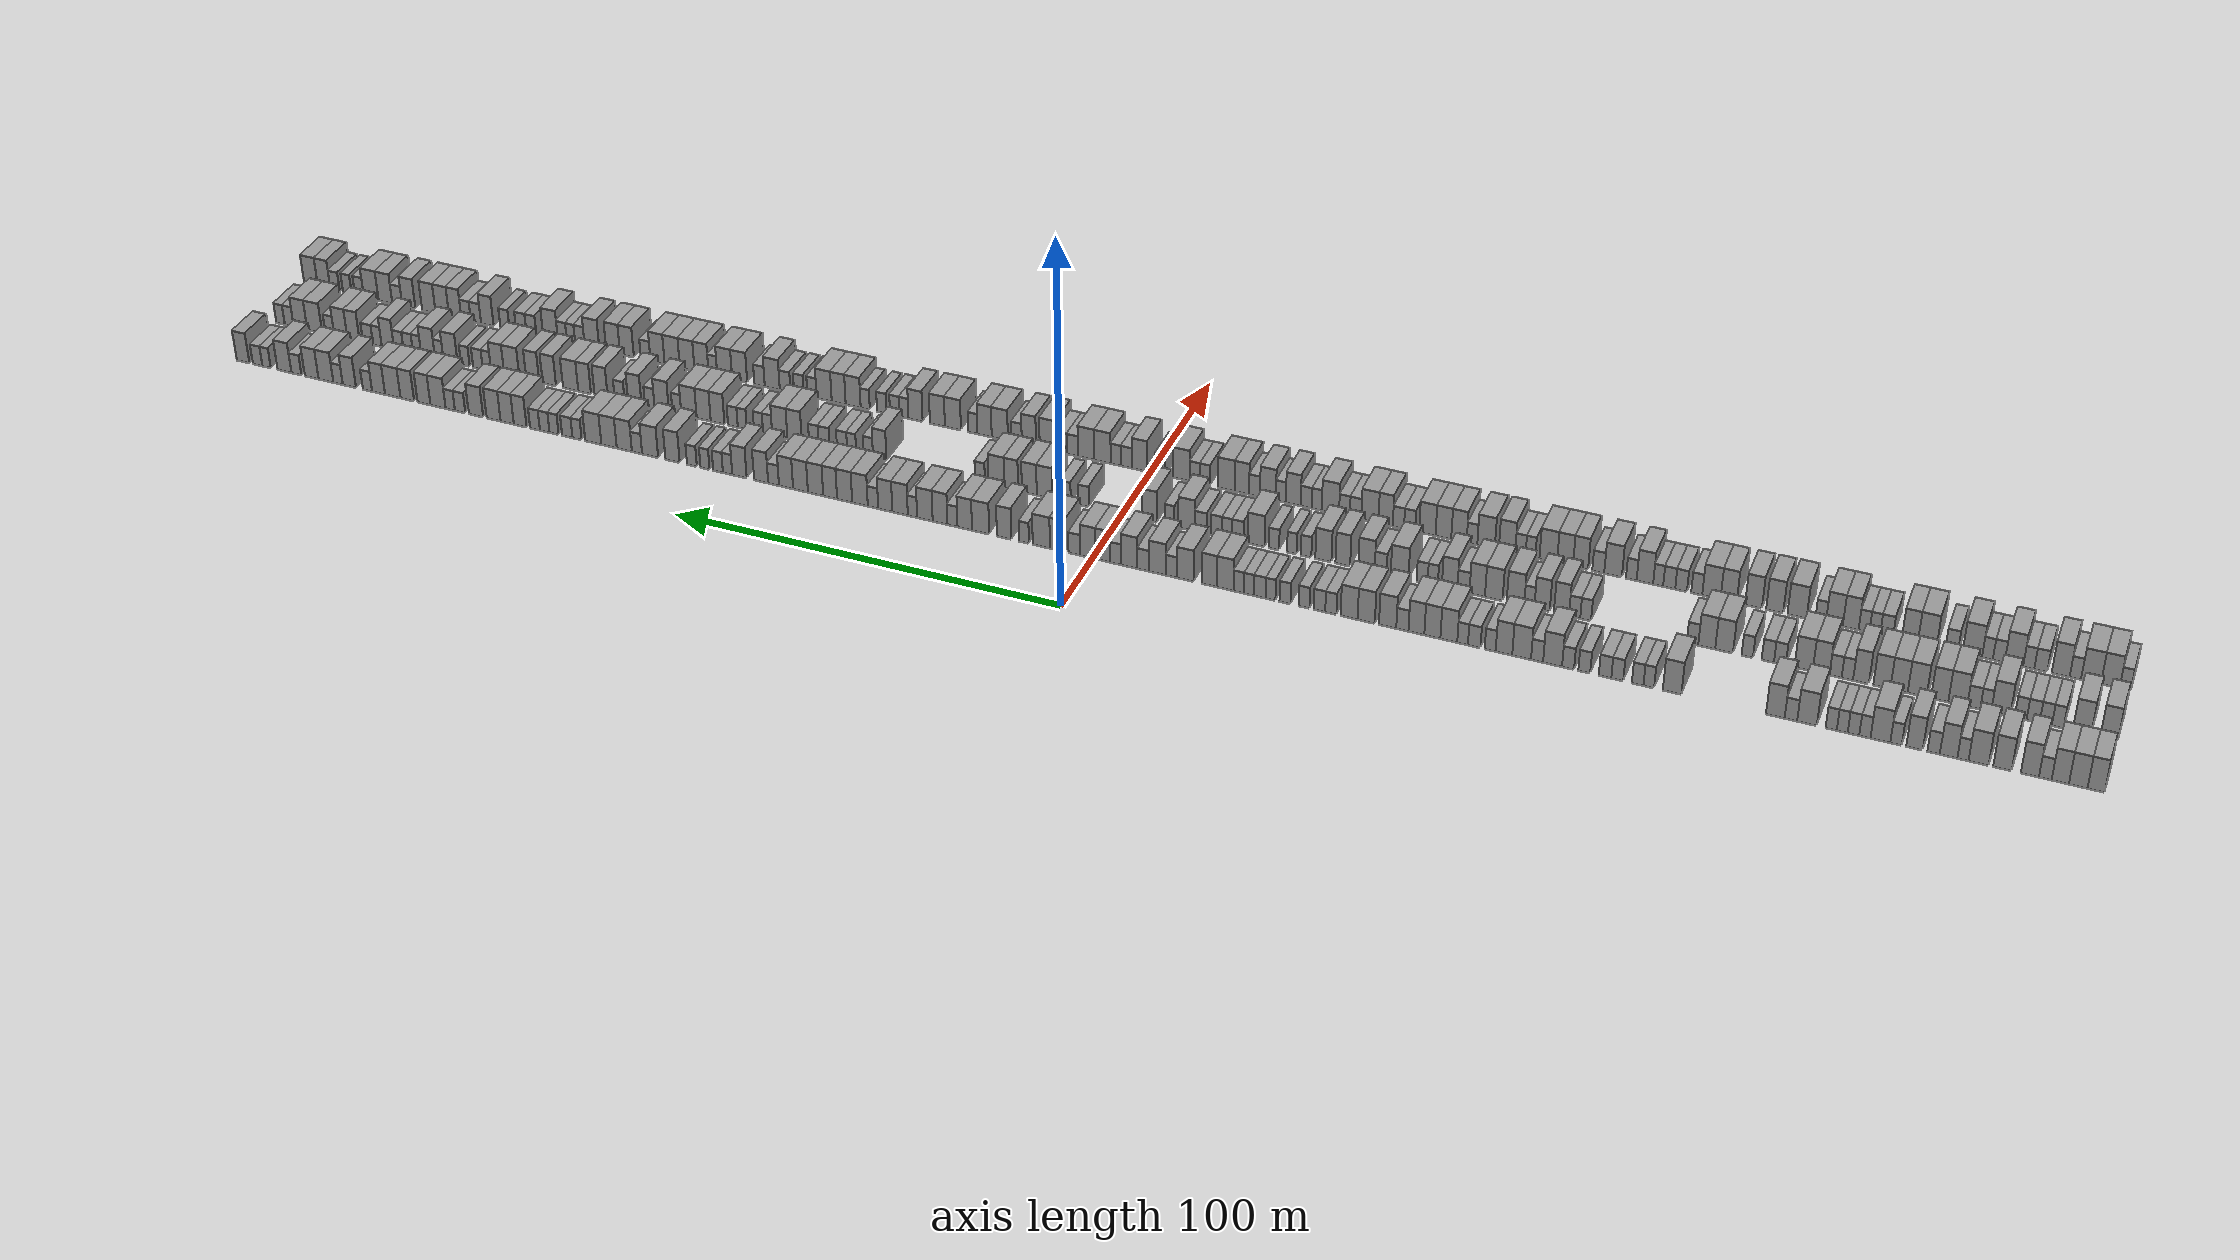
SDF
<sdf version="1.6">
 <world name="default">
  <scene>
   <sky><clouds><speed>12</speed></clouds></sky>
   <ambient>0.4 0.4 0.4 1</ambient>
   <background>0.7 0.7 0.7 1</background>
   <shadows>1</shadows>
  </scene>
  <gravity>0 0 -9.8066</gravity>
  <magnetic_field>6e-06 2.3e-05 -4.2e-05</magnetic_field>
  <physics default="0" name="default_physics" type="ode">
   <ode>
    <solver>
     <type>quick</type>
     <iters>10</iters>
     <sor>1.0</sor>
     <use_dynamic_moi_rescaling>0</use_dynamic_moi_rescaling>
    </solver>
    <constraints>
     <cfm>0</cfm>
     <erp>0.2</erp>
     <contact_max_correcting_vel>100</contact_max_correcting_vel>
     <contact_surface_layer>0.001</contact_surface_layer>
    </constraints>
   </ode>
   <max_step_size>0.004</max_step_size>
   <real_time_factor>1</real_time_factor>
   <real_time_update_rate>250</real_time_update_rate>
  </physics>
  <light name="sun" type="directional">
   <pose>0 0 10 0 0 0</pose>
   <diffuse>0.8 0.8 0.8 1</diffuse>
   <specular>0.2 0.2 0.2 1</specular>
   <attenuation>
    <range>1000</range>
    <constant>0.9</constant>
    <linear>0.01</linear>
    <quadratic>0.001</quadratic>
   </attenuation>
   <direction>-0.5 0.1 -0.9</direction>
  </light>
  <model name="building_1">
   <static>1</static>
   <pose>25.0000 -234.1651 0 0.000000 0.000000 0.000000</pose>
   <link name="link">
    <pose>0 0 4.50 0 0 0</pose>
    <collision name="collision"><geometry><box><size>10.0000 3.6698 9.0000</size></box></geometry></collision>
    <visual name="visual">
     <cast_shadows>0</cast_shadows>
     <geometry><box><size>10.0000 3.6698 9.0000</size></box></geometry>
     <material>
      <script>
       <uri>model://grey_wall/materials/scripts</uri>
       <uri>model://grey_wall/materials/textures</uri>
       <name>vrc/grey_wall</name>
      </script>
     </material>
    </visual>
   </link>
  </model>
  <model name="building_2">
   <static>1</static>
   <pose>25.0000 -230.3280 0 0.000000 0.000000 0.000000</pose>
   <link name="link">
    <pose>0 0 4.50 0 0 0</pose>
    <collision name="collision"><geometry><box><size>10.0000 4.0046 9.0000</size></box></geometry></collision>
    <visual name="visual">
     <cast_shadows>0</cast_shadows>
     <geometry><box><size>10.0000 4.0046 9.0000</size></box></geometry>
     <material>
      <script>
       <uri>model://grey_wall/materials/scripts</uri>
       <uri>model://grey_wall/materials/textures</uri>
       <name>vrc/grey_wall</name>
      </script>
     </material>
    </visual>
   </link>
  </model>
  <model name="building_3">
   <static>1</static>
   <pose>25.0000 -226.4558 0 0.000000 0.000000 0.000000</pose>
   <link name="link">
    <pose>0 0 4.50 0 0 0</pose>
    <collision name="collision"><geometry><box><size>10.0000 3.7398 9.0000</size></box></geometry></collision>
    <visual name="visual">
     <cast_shadows>0</cast_shadows>
     <geometry><box><size>10.0000 3.7398 9.0000</size></box></geometry>
     <material>
      <script>
       <uri>model://grey_wall/materials/scripts</uri>
       <uri>model://grey_wall/materials/textures</uri>
       <name>vrc/grey_wall</name>
      </script>
     </material>
    </visual>
   </link>
  </model>
  <model name="building_4">
   <static>1</static>
   <pose>25.0000 -223.2216 0 0.000000 0.000000 0.000000</pose>
   <link name="link">
    <pose>0 0 3.00 0 0 0</pose>
    <collision name="collision"><geometry><box><size>10.0000 2.7286 6.0000</size></box></geometry></collision>
    <visual name="visual">
     <cast_shadows>0</cast_shadows>
     <geometry><box><size>10.0000 2.7286 6.0000</size></box></geometry>
     <material>
      <script>
       <uri>model://grey_wall/materials/scripts</uri>
       <uri>model://grey_wall/materials/textures</uri>
       <name>vrc/grey_wall</name>
      </script>
     </material>
    </visual>
   </link>
  </model>
  <model name="building_5">
   <static>1</static>
   <pose>25.0000 -219.8917 0 0.000000 0.000000 0.000000</pose>
   <link name="link">
    <pose>0 0 4.50 0 0 0</pose>
    <collision name="collision"><geometry><box><size>10.0000 3.9312 9.0000</size></box></geometry></collision>
    <visual name="visual">
     <cast_shadows>0</cast_shadows>
     <geometry><box><size>10.0000 3.9312 9.0000</size></box></geometry>
     <material>
      <script>
       <uri>model://grey_wall/materials/scripts</uri>
       <uri>model://grey_wall/materials/textures</uri>
       <name>vrc/grey_wall</name>
      </script>
     </material>
    </visual>
   </link>
  </model>
  <model name="building_6">
   <static>1</static>
   <pose>25.0000 -213.9135 0 0.000000 0.000000 0.000000</pose>
   <link name="link">
    <pose>0 0 4.50 0 0 0</pose>
    <collision name="collision"><geometry><box><size>10.0000 4.0252 9.0000</size></box></geometry></collision>
    <visual name="visual">
     <cast_shadows>0</cast_shadows>
     <geometry><box><size>10.0000 4.0252 9.0000</size></box></geometry>
     <material>
      <script>
       <uri>model://grey_wall/materials/scripts</uri>
       <uri>model://grey_wall/materials/textures</uri>
       <name>vrc/grey_wall</name>
      </script>
     </material>
    </visual>
   </link>
  </model>
  <model name="building_7">
   <static>1</static>
   <pose>25.0000 -208.7086 0 0.000000 0.000000 0.000000</pose>
   <link name="link">
    <pose>0 0 4.50 0 0 0</pose>
    <collision name="collision"><geometry><box><size>10.0000 4.3846 9.0000</size></box></geometry></collision>
    <visual name="visual">
     <cast_shadows>0</cast_shadows>
     <geometry><box><size>10.0000 4.3846 9.0000</size></box></geometry>
     <material>
      <script>
       <uri>model://grey_wall/materials/scripts</uri>
       <uri>model://grey_wall/materials/textures</uri>
       <name>vrc/grey_wall</name>
      </script>
     </material>
    </visual>
   </link>
  </model>
  <model name="building_8">
   <static>1</static>
   <pose>25.0000 -205.2882 0 0.000000 0.000000 0.000000</pose>
   <link name="link">
    <pose>0 0 3.00 0 0 0</pose>
    <collision name="collision"><geometry><box><size>10.0000 2.4560 6.0000</size></box></geometry></collision>
    <visual name="visual">
     <cast_shadows>0</cast_shadows>
     <geometry><box><size>10.0000 2.4560 6.0000</size></box></geometry>
     <material>
      <script>
       <uri>model://grey_wall/materials/scripts</uri>
       <uri>model://grey_wall/materials/textures</uri>
       <name>vrc/grey_wall</name>
      </script>
     </material>
    </visual>
   </link>
  </model>
  <model name="building_9">
   <static>1</static>
   <pose>25.0000 -202.1338 0 0.000000 0.000000 0.000000</pose>
   <link name="link">
    <pose>0 0 4.50 0 0 0</pose>
    <collision name="collision"><geometry><box><size>10.0000 3.8529 9.0000</size></box></geometry></collision>
    <visual name="visual">
     <cast_shadows>0</cast_shadows>
     <geometry><box><size>10.0000 3.8529 9.0000</size></box></geometry>
     <material>
      <script>
       <uri>model://grey_wall/materials/scripts</uri>
       <uri>model://grey_wall/materials/textures</uri>
       <name>vrc/grey_wall</name>
      </script>
     </material>
    </visual>
   </link>
  </model>
  <model name="building_10">
   <static>1</static>
   <pose>25.0000 -198.8336 0 0.000000 0.000000 0.000000</pose>
   <link name="link">
    <pose>0 0 3.00 0 0 0</pose>
    <collision name="collision"><geometry><box><size>10.0000 2.7475 6.0000</size></box></geometry></collision>
    <visual name="visual">
     <cast_shadows>0</cast_shadows>
     <geometry><box><size>10.0000 2.7475 6.0000</size></box></geometry>
     <material>
      <script>
       <uri>model://grey_wall/materials/scripts</uri>
       <uri>model://grey_wall/materials/textures</uri>
       <name>vrc/grey_wall</name>
      </script>
     </material>
    </visual>
   </link>
  </model>
  <model name="building_11">
   <static>1</static>
   <pose>25.0000 -194.6289 0 0.000000 0.000000 0.000000</pose>
   <link name="link">
    <pose>0 0 4.50 0 0 0</pose>
    <collision name="collision"><geometry><box><size>10.0000 3.6620 9.0000</size></box></geometry></collision>
    <visual name="visual">
     <cast_shadows>0</cast_shadows>
     <geometry><box><size>10.0000 3.6620 9.0000</size></box></geometry>
     <material>
      <script>
       <uri>model://grey_wall/materials/scripts</uri>
       <uri>model://grey_wall/materials/textures</uri>
       <name>vrc/grey_wall</name>
      </script>
     </material>
    </visual>
   </link>
  </model>
  <model name="building_12">
   <static>1</static>
   <pose>25.0000 -190.5297 0 0.000000 0.000000 0.000000</pose>
   <link name="link">
    <pose>0 0 3.00 0 0 0</pose>
    <collision name="collision"><geometry><box><size>10.0000 2.5362 6.0000</size></box></geometry></collision>
    <visual name="visual">
     <cast_shadows>0</cast_shadows>
     <geometry><box><size>10.0000 2.5362 6.0000</size></box></geometry>
     <material>
      <script>
       <uri>model://grey_wall/materials/scripts</uri>
       <uri>model://grey_wall/materials/textures</uri>
       <name>vrc/grey_wall</name>
      </script>
     </material>
    </visual>
   </link>
  </model>
  <model name="building_13">
   <static>1</static>
   <pose>25.0000 -187.0638 0 0.000000 0.000000 0.000000</pose>
   <link name="link">
    <pose>0 0 4.50 0 0 0</pose>
    <collision name="collision"><geometry><box><size>10.0000 4.3957 9.0000</size></box></geometry></collision>
    <visual name="visual">
     <cast_shadows>0</cast_shadows>
     <geometry><box><size>10.0000 4.3957 9.0000</size></box></geometry>
     <material>
      <script>
       <uri>model://grey_wall/materials/scripts</uri>
       <uri>model://grey_wall/materials/textures</uri>
       <name>vrc/grey_wall</name>
      </script>
     </material>
    </visual>
   </link>
  </model>
  <model name="building_14">
   <static>1</static>
   <pose>25.0000 -183.6093 0 0.000000 0.000000 0.000000</pose>
   <link name="link">
    <pose>0 0 3.00 0 0 0</pose>
    <collision name="collision"><geometry><box><size>10.0000 2.5132 6.0000</size></box></geometry></collision>
    <visual name="visual">
     <cast_shadows>0</cast_shadows>
     <geometry><box><size>10.0000 2.5132 6.0000</size></box></geometry>
     <material>
      <script>
       <uri>model://grey_wall/materials/scripts</uri>
       <uri>model://grey_wall/materials/textures</uri>
       <name>vrc/grey_wall</name>
      </script>
     </material>
    </visual>
   </link>
  </model>
  <model name="building_15">
   <static>1</static>
   <pose>25.0000 -181.0666 0 0.000000 0.000000 0.000000</pose>
   <link name="link">
    <pose>0 0 3.00 0 0 0</pose>
    <collision name="collision"><geometry><box><size>10.0000 2.5722 6.0000</size></box></geometry></collision>
    <visual name="visual">
     <cast_shadows>0</cast_shadows>
     <geometry><box><size>10.0000 2.5722 6.0000</size></box></geometry>
     <material>
      <script>
       <uri>model://grey_wall/materials/scripts</uri>
       <uri>model://grey_wall/materials/textures</uri>
       <name>vrc/grey_wall</name>
      </script>
     </material>
    </visual>
   </link>
  </model>
  <model name="building_16">
   <static>1</static>
   <pose>25.0000 -178.5636 0 0.000000 0.000000 0.000000</pose>
   <link name="link">
    <pose>0 0 3.00 0 0 0</pose>
    <collision name="collision"><geometry><box><size>10.0000 2.4338 6.0000</size></box></geometry></collision>
    <visual name="visual">
     <cast_shadows>0</cast_shadows>
     <geometry><box><size>10.0000 2.4338 6.0000</size></box></geometry>
     <material>
      <script>
       <uri>model://grey_wall/materials/scripts</uri>
       <uri>model://grey_wall/materials/textures</uri>
       <name>vrc/grey_wall</name>
      </script>
     </material>
    </visual>
   </link>
  </model>
  <model name="building_17">
   <static>1</static>
   <pose>25.0000 -176.0946 0 0.000000 0.000000 0.000000</pose>
   <link name="link">
    <pose>0 0 3.00 0 0 0</pose>
    <collision name="collision"><geometry><box><size>10.0000 2.5043 6.0000</size></box></geometry></collision>
    <visual name="visual">
     <cast_shadows>0</cast_shadows>
     <geometry><box><size>10.0000 2.5043 6.0000</size></box></geometry>
     <material>
      <script>
       <uri>model://grey_wall/materials/scripts</uri>
       <uri>model://grey_wall/materials/textures</uri>
       <name>vrc/grey_wall</name>
      </script>
     </material>
    </visual>
   </link>
  </model>
  <model name="building_18">
   <static>1</static>
   <pose>25.0000 -170.6351 0 0.000000 0.000000 0.000000</pose>
   <link name="link">
    <pose>0 0 4.50 0 0 0</pose>
    <collision name="collision"><geometry><box><size>10.0000 4.4146 9.0000</size></box></geometry></collision>
    <visual name="visual">
     <cast_shadows>0</cast_shadows>
     <geometry><box><size>10.0000 4.4146 9.0000</size></box></geometry>
     <material>
      <script>
       <uri>model://grey_wall/materials/scripts</uri>
       <uri>model://grey_wall/materials/textures</uri>
       <name>vrc/grey_wall</name>
      </script>
     </material>
    </visual>
   </link>
  </model>
  <model name="building_19">
   <static>1</static>
   <pose>25.0000 -167.0160 0 0.000000 0.000000 0.000000</pose>
   <link name="link">
    <pose>0 0 3.00 0 0 0</pose>
    <collision name="collision"><geometry><box><size>10.0000 2.8236 6.0000</size></box></geometry></collision>
    <visual name="visual">
     <cast_shadows>0</cast_shadows>
     <geometry><box><size>10.0000 2.8236 6.0000</size></box></geometry>
     <material>
      <script>
       <uri>model://grey_wall/materials/scripts</uri>
       <uri>model://grey_wall/materials/textures</uri>
       <name>vrc/grey_wall</name>
      </script>
     </material>
    </visual>
   </link>
  </model>
  <model name="building_20">
   <static>1</static>
   <pose>25.0000 -163.4946 0 0.000000 0.000000 0.000000</pose>
   <link name="link">
    <pose>0 0 4.50 0 0 0</pose>
    <collision name="collision"><geometry><box><size>10.0000 4.2192 9.0000</size></box></geometry></collision>
    <visual name="visual">
     <cast_shadows>0</cast_shadows>
     <geometry><box><size>10.0000 4.2192 9.0000</size></box></geometry>
     <material>
      <script>
       <uri>model://grey_wall/materials/scripts</uri>
       <uri>model://grey_wall/materials/textures</uri>
       <name>vrc/grey_wall</name>
      </script>
     </material>
    </visual>
   </link>
  </model>
  <model name="building_21">
   <static>1</static>
   <pose>25.0000 -139.9461 0 0.000000 0.000000 0.000000</pose>
   <link name="link">
    <pose>0 0 4.50 0 0 0</pose>
    <collision name="collision"><geometry><box><size>10.0000 4.2926 9.0000</size></box></geometry></collision>
    <visual name="visual">
     <cast_shadows>0</cast_shadows>
     <geometry><box><size>10.0000 4.2926 9.0000</size></box></geometry>
     <material>
      <script>
       <uri>model://grey_wall/materials/scripts</uri>
       <uri>model://grey_wall/materials/textures</uri>
       <name>vrc/grey_wall</name>
      </script>
     </material>
    </visual>
   </link>
  </model>
  <model name="building_22">
   <static>1</static>
   <pose>25.0000 -134.5706 0 0.000000 0.000000 0.000000</pose>
   <link name="link">
    <pose>0 0 3.00 0 0 0</pose>
    <collision name="collision"><geometry><box><size>10.0000 2.4585 6.0000</size></box></geometry></collision>
    <visual name="visual">
     <cast_shadows>0</cast_shadows>
     <geometry><box><size>10.0000 2.4585 6.0000</size></box></geometry>
     <material>
      <script>
       <uri>model://grey_wall/materials/scripts</uri>
       <uri>model://grey_wall/materials/textures</uri>
       <name>vrc/grey_wall</name>
      </script>
     </material>
    </visual>
   </link>
  </model>
  <model name="building_23">
   <static>1</static>
   <pose>25.0000 -131.9999 0 0.000000 0.000000 0.000000</pose>
   <link name="link">
    <pose>0 0 3.00 0 0 0</pose>
    <collision name="collision"><geometry><box><size>10.0000 2.6829 6.0000</size></box></geometry></collision>
    <visual name="visual">
     <cast_shadows>0</cast_shadows>
     <geometry><box><size>10.0000 2.6829 6.0000</size></box></geometry>
     <material>
      <script>
       <uri>model://grey_wall/materials/scripts</uri>
       <uri>model://grey_wall/materials/textures</uri>
       <name>vrc/grey_wall</name>
      </script>
     </material>
    </visual>
   </link>
  </model>
  <model name="building_24">
   <static>1</static>
   <pose>25.0000 -127.2707 0 0.000000 0.000000 0.000000</pose>
   <link name="link">
    <pose>0 0 3.00 0 0 0</pose>
    <collision name="collision"><geometry><box><size>10.0000 2.7756 6.0000</size></box></geometry></collision>
    <visual name="visual">
     <cast_shadows>0</cast_shadows>
     <geometry><box><size>10.0000 2.7756 6.0000</size></box></geometry>
     <material>
      <script>
       <uri>model://grey_wall/materials/scripts</uri>
       <uri>model://grey_wall/materials/textures</uri>
       <name>vrc/grey_wall</name>
      </script>
     </material>
    </visual>
   </link>
  </model>
  <model name="building_25">
   <static>1</static>
   <pose>25.0000 -124.4217 0 0.000000 0.000000 0.000000</pose>
   <link name="link">
    <pose>0 0 3.00 0 0 0</pose>
    <collision name="collision"><geometry><box><size>10.0000 2.9224 6.0000</size></box></geometry></collision>
    <visual name="visual">
     <cast_shadows>0</cast_shadows>
     <geometry><box><size>10.0000 2.9224 6.0000</size></box></geometry>
     <material>
      <script>
       <uri>model://grey_wall/materials/scripts</uri>
       <uri>model://grey_wall/materials/textures</uri>
       <name>vrc/grey_wall</name>
      </script>
     </material>
    </visual>
   </link>
  </model>
  <model name="building_26">
   <static>1</static>
   <pose>25.0000 -119.5755 0 0.000000 0.000000 0.000000</pose>
   <link name="link">
    <pose>0 0 3.00 0 0 0</pose>
    <collision name="collision"><geometry><box><size>10.0000 2.7701 6.0000</size></box></geometry></collision>
    <visual name="visual">
     <cast_shadows>0</cast_shadows>
     <geometry><box><size>10.0000 2.7701 6.0000</size></box></geometry>
     <material>
      <script>
       <uri>model://grey_wall/materials/scripts</uri>
       <uri>model://grey_wall/materials/textures</uri>
       <name>vrc/grey_wall</name>
      </script>
     </material>
    </visual>
   </link>
  </model>
  <model name="building_27">
   <static>1</static>
   <pose>25.0000 -115.7886 0 0.000000 0.000000 0.000000</pose>
   <link name="link">
    <pose>0 0 3.00 0 0 0</pose>
    <collision name="collision"><geometry><box><size>10.0000 2.8036 6.0000</size></box></geometry></collision>
    <visual name="visual">
     <cast_shadows>0</cast_shadows>
     <geometry><box><size>10.0000 2.8036 6.0000</size></box></geometry>
     <material>
      <script>
       <uri>model://grey_wall/materials/scripts</uri>
       <uri>model://grey_wall/materials/textures</uri>
       <name>vrc/grey_wall</name>
      </script>
     </material>
    </visual>
   </link>
  </model>
  <model name="building_28">
   <static>1</static>
   <pose>25.0000 -112.1589 0 0.000000 0.000000 0.000000</pose>
   <link name="link">
    <pose>0 0 4.50 0 0 0</pose>
    <collision name="collision"><geometry><box><size>10.0000 4.4559 9.0000</size></box></geometry></collision>
    <visual name="visual">
     <cast_shadows>0</cast_shadows>
     <geometry><box><size>10.0000 4.4559 9.0000</size></box></geometry>
     <material>
      <script>
       <uri>model://grey_wall/materials/scripts</uri>
       <uri>model://grey_wall/materials/textures</uri>
       <name>vrc/grey_wall</name>
      </script>
     </material>
    </visual>
   </link>
  </model>
  <model name="building_29">
   <static>1</static>
   <pose>25.0000 -108.5100 0 0.000000 0.000000 0.000000</pose>
   <link name="link">
    <pose>0 0 3.00 0 0 0</pose>
    <collision name="collision"><geometry><box><size>10.0000 2.8418 6.0000</size></box></geometry></collision>
    <visual name="visual">
     <cast_shadows>0</cast_shadows>
     <geometry><box><size>10.0000 2.8418 6.0000</size></box></geometry>
     <material>
      <script>
       <uri>model://grey_wall/materials/scripts</uri>
       <uri>model://grey_wall/materials/textures</uri>
       <name>vrc/grey_wall</name>
      </script>
     </material>
    </visual>
   </link>
  </model>
  <model name="building_30">
   <static>1</static>
   <pose>25.0000 -104.8680 0 0.000000 0.000000 0.000000</pose>
   <link name="link">
    <pose>0 0 4.50 0 0 0</pose>
    <collision name="collision"><geometry><box><size>10.0000 4.4422 9.0000</size></box></geometry></collision>
    <visual name="visual">
     <cast_shadows>0</cast_shadows>
     <geometry><box><size>10.0000 4.4422 9.0000</size></box></geometry>
     <material>
      <script>
       <uri>model://grey_wall/materials/scripts</uri>
       <uri>model://grey_wall/materials/textures</uri>
       <name>vrc/grey_wall</name>
      </script>
     </material>
    </visual>
   </link>
  </model>
  <model name="building_31">
   <static>1</static>
   <pose>25.0000 -100.6837 0 0.000000 0.000000 0.000000</pose>
   <link name="link">
    <pose>0 0 4.50 0 0 0</pose>
    <collision name="collision"><geometry><box><size>10.0000 3.9265 9.0000</size></box></geometry></collision>
    <visual name="visual">
     <cast_shadows>0</cast_shadows>
     <geometry><box><size>10.0000 3.9265 9.0000</size></box></geometry>
     <material>
      <script>
       <uri>model://grey_wall/materials/scripts</uri>
       <uri>model://grey_wall/materials/textures</uri>
       <name>vrc/grey_wall</name>
      </script>
     </material>
    </visual>
   </link>
  </model>
  <model name="building_32">
   <static>1</static>
   <pose>25.0000 -97.4180 0 0.000000 0.000000 0.000000</pose>
   <link name="link">
    <pose>0 0 3.00 0 0 0</pose>
    <collision name="collision"><geometry><box><size>10.0000 2.6049 6.0000</size></box></geometry></collision>
    <visual name="visual">
     <cast_shadows>0</cast_shadows>
     <geometry><box><size>10.0000 2.6049 6.0000</size></box></geometry>
     <material>
      <script>
       <uri>model://grey_wall/materials/scripts</uri>
       <uri>model://grey_wall/materials/textures</uri>
       <name>vrc/grey_wall</name>
      </script>
     </material>
    </visual>
   </link>
  </model>
  <model name="building_33">
   <static>1</static>
   <pose>25.0000 -93.6222 0 0.000000 0.000000 0.000000</pose>
   <link name="link">
    <pose>0 0 3.00 0 0 0</pose>
    <collision name="collision"><geometry><box><size>10.0000 2.9867 6.0000</size></box></geometry></collision>
    <visual name="visual">
     <cast_shadows>0</cast_shadows>
     <geometry><box><size>10.0000 2.9867 6.0000</size></box></geometry>
     <material>
      <script>
       <uri>model://grey_wall/materials/scripts</uri>
       <uri>model://grey_wall/materials/textures</uri>
       <name>vrc/grey_wall</name>
      </script>
     </material>
    </visual>
   </link>
  </model>
  <model name="building_34">
   <static>1</static>
   <pose>25.0000 -90.8556 0 0.000000 0.000000 0.000000</pose>
   <link name="link">
    <pose>0 0 3.00 0 0 0</pose>
    <collision name="collision"><geometry><box><size>10.0000 2.5463 6.0000</size></box></geometry></collision>
    <visual name="visual">
     <cast_shadows>0</cast_shadows>
     <geometry><box><size>10.0000 2.5463 6.0000</size></box></geometry>
     <material>
      <script>
       <uri>model://grey_wall/materials/scripts</uri>
       <uri>model://grey_wall/materials/textures</uri>
       <name>vrc/grey_wall</name>
      </script>
     </material>
    </visual>
   </link>
  </model>
  <model name="building_35">
   <static>1</static>
   <pose>25.0000 -87.5665 0 0.000000 0.000000 0.000000</pose>
   <link name="link">
    <pose>0 0 4.50 0 0 0</pose>
    <collision name="collision"><geometry><box><size>10.0000 4.0319 9.0000</size></box></geometry></collision>
    <visual name="visual">
     <cast_shadows>0</cast_shadows>
     <geometry><box><size>10.0000 4.0319 9.0000</size></box></geometry>
     <material>
      <script>
       <uri>model://grey_wall/materials/scripts</uri>
       <uri>model://grey_wall/materials/textures</uri>
       <name>vrc/grey_wall</name>
      </script>
     </material>
    </visual>
   </link>
  </model>
  <model name="building_36">
   <static>1</static>
   <pose>25.0000 -83.6215 0 0.000000 0.000000 0.000000</pose>
   <link name="link">
    <pose>0 0 4.50 0 0 0</pose>
    <collision name="collision"><geometry><box><size>10.0000 3.8579 9.0000</size></box></geometry></collision>
    <visual name="visual">
     <cast_shadows>0</cast_shadows>
     <geometry><box><size>10.0000 3.8579 9.0000</size></box></geometry>
     <material>
      <script>
       <uri>model://grey_wall/materials/scripts</uri>
       <uri>model://grey_wall/materials/textures</uri>
       <name>vrc/grey_wall</name>
      </script>
     </material>
    </visual>
   </link>
  </model>
  <model name="building_37">
   <static>1</static>
   <pose>25.0000 -79.7842 0 0.000000 0.000000 0.000000</pose>
   <link name="link">
    <pose>0 0 4.50 0 0 0</pose>
    <collision name="collision"><geometry><box><size>10.0000 3.8168 9.0000</size></box></geometry></collision>
    <visual name="visual">
     <cast_shadows>0</cast_shadows>
     <geometry><box><size>10.0000 3.8168 9.0000</size></box></geometry>
     <material>
      <script>
       <uri>model://grey_wall/materials/scripts</uri>
       <uri>model://grey_wall/materials/textures</uri>
       <name>vrc/grey_wall</name>
      </script>
     </material>
    </visual>
   </link>
  </model>
  <model name="building_38">
   <static>1</static>
   <pose>25.0000 -76.4047 0 0.000000 0.000000 0.000000</pose>
   <link name="link">
    <pose>0 0 3.00 0 0 0</pose>
    <collision name="collision"><geometry><box><size>10.0000 2.9422 6.0000</size></box></geometry></collision>
    <visual name="visual">
     <cast_shadows>0</cast_shadows>
     <geometry><box><size>10.0000 2.9422 6.0000</size></box></geometry>
     <material>
      <script>
       <uri>model://grey_wall/materials/scripts</uri>
       <uri>model://grey_wall/materials/textures</uri>
       <name>vrc/grey_wall</name>
      </script>
     </material>
    </visual>
   </link>
  </model>
  <model name="building_39">
   <static>1</static>
   <pose>25.0000 -72.8453 0 0.000000 0.000000 0.000000</pose>
   <link name="link">
    <pose>0 0 4.50 0 0 0</pose>
    <collision name="collision"><geometry><box><size>10.0000 4.1766 9.0000</size></box></geometry></collision>
    <visual name="visual">
     <cast_shadows>0</cast_shadows>
     <geometry><box><size>10.0000 4.1766 9.0000</size></box></geometry>
     <material>
      <script>
       <uri>model://grey_wall/materials/scripts</uri>
       <uri>model://grey_wall/materials/textures</uri>
       <name>vrc/grey_wall</name>
      </script>
     </material>
    </visual>
   </link>
  </model>
  <model name="building_40">
   <static>1</static>
   <pose>25.0000 -67.6591 0 0.000000 0.000000 0.000000</pose>
   <link name="link">
    <pose>0 0 4.50 0 0 0</pose>
    <collision name="collision"><geometry><box><size>10.0000 4.1959 9.0000</size></box></geometry></collision>
    <visual name="visual">
     <cast_shadows>0</cast_shadows>
     <geometry><box><size>10.0000 4.1959 9.0000</size></box></geometry>
     <material>
      <script>
       <uri>model://grey_wall/materials/scripts</uri>
       <uri>model://grey_wall/materials/textures</uri>
       <name>vrc/grey_wall</name>
      </script>
     </material>
    </visual>
   </link>
  </model>
  <model name="building_41">
   <static>1</static>
   <pose>25.0000 -63.4962 0 0.000000 0.000000 0.000000</pose>
   <link name="link">
    <pose>0 0 4.50 0 0 0</pose>
    <collision name="collision"><geometry><box><size>10.0000 4.1298 9.0000</size></box></geometry></collision>
    <visual name="visual">
     <cast_shadows>0</cast_shadows>
     <geometry><box><size>10.0000 4.1298 9.0000</size></box></geometry>
     <material>
      <script>
       <uri>model://grey_wall/materials/scripts</uri>
       <uri>model://grey_wall/materials/textures</uri>
       <name>vrc/grey_wall</name>
      </script>
     </material>
    </visual>
   </link>
  </model>
  <model name="building_42">
   <static>1</static>
   <pose>25.0000 -59.0574 0 0.000000 0.000000 0.000000</pose>
   <link name="link">
    <pose>0 0 3.00 0 0 0</pose>
    <collision name="collision"><geometry><box><size>10.0000 2.7478 6.0000</size></box></geometry></collision>
    <visual name="visual">
     <cast_shadows>0</cast_shadows>
     <geometry><box><size>10.0000 2.7478 6.0000</size></box></geometry>
     <material>
      <script>
       <uri>model://grey_wall/materials/scripts</uri>
       <uri>model://grey_wall/materials/textures</uri>
       <name>vrc/grey_wall</name>
      </script>
     </material>
    </visual>
   </link>
  </model>
  <model name="building_43">
   <static>1</static>
   <pose>25.0000 -56.2807 0 0.000000 0.000000 0.000000</pose>
   <link name="link">
    <pose>0 0 3.00 0 0 0</pose>
    <collision name="collision"><geometry><box><size>10.0000 2.8056 6.0000</size></box></geometry></collision>
    <visual name="visual">
     <cast_shadows>0</cast_shadows>
     <geometry><box><size>10.0000 2.8056 6.0000</size></box></geometry>
     <material>
      <script>
       <uri>model://grey_wall/materials/scripts</uri>
       <uri>model://grey_wall/materials/textures</uri>
       <name>vrc/grey_wall</name>
      </script>
     </material>
    </visual>
   </link>
  </model>
  <model name="building_44">
   <static>1</static>
   <pose>25.0000 -52.5314 0 0.000000 0.000000 0.000000</pose>
   <link name="link">
    <pose>0 0 3.00 0 0 0</pose>
    <collision name="collision"><geometry><box><size>10.0000 2.6931 6.0000</size></box></geometry></collision>
    <visual name="visual">
     <cast_shadows>0</cast_shadows>
     <geometry><box><size>10.0000 2.6931 6.0000</size></box></geometry>
     <material>
      <script>
       <uri>model://grey_wall/materials/scripts</uri>
       <uri>model://grey_wall/materials/textures</uri>
       <name>vrc/grey_wall</name>
      </script>
     </material>
    </visual>
   </link>
  </model>
  <model name="building_45">
   <static>1</static>
   <pose>25.0000 -47.8277 0 0.000000 0.000000 0.000000</pose>
   <link name="link">
    <pose>0 0 3.00 0 0 0</pose>
    <collision name="collision"><geometry><box><size>10.0000 2.7142 6.0000</size></box></geometry></collision>
    <visual name="visual">
     <cast_shadows>0</cast_shadows>
     <geometry><box><size>10.0000 2.7142 6.0000</size></box></geometry>
     <material>
      <script>
       <uri>model://grey_wall/materials/scripts</uri>
       <uri>model://grey_wall/materials/textures</uri>
       <name>vrc/grey_wall</name>
      </script>
     </material>
    </visual>
   </link>
  </model>
  <model name="building_46">
   <static>1</static>
   <pose>25.0000 -44.2647 0 0.000000 0.000000 0.000000</pose>
   <link name="link">
    <pose>0 0 3.00 0 0 0</pose>
    <collision name="collision"><geometry><box><size>10.0000 2.4117 6.0000</size></box></geometry></collision>
    <visual name="visual">
     <cast_shadows>0</cast_shadows>
     <geometry><box><size>10.0000 2.4117 6.0000</size></box></geometry>
     <material>
      <script>
       <uri>model://grey_wall/materials/scripts</uri>
       <uri>model://grey_wall/materials/textures</uri>
       <name>vrc/grey_wall</name>
      </script>
     </material>
    </visual>
   </link>
  </model>
  <model name="building_47">
   <static>1</static>
   <pose>25.0000 -41.6088 0 0.000000 0.000000 0.000000</pose>
   <link name="link">
    <pose>0 0 3.00 0 0 0</pose>
    <collision name="collision"><geometry><box><size>10.0000 2.9002 6.0000</size></box></geometry></collision>
    <visual name="visual">
     <cast_shadows>0</cast_shadows>
     <geometry><box><size>10.0000 2.9002 6.0000</size></box></geometry>
     <material>
      <script>
       <uri>model://grey_wall/materials/scripts</uri>
       <uri>model://grey_wall/materials/textures</uri>
       <name>vrc/grey_wall</name>
      </script>
     </material>
    </visual>
   </link>
  </model>
  <model name="building_48">
   <static>1</static>
   <pose>25.0000 -38.9395 0 0.000000 0.000000 0.000000</pose>
   <link name="link">
    <pose>0 0 3.00 0 0 0</pose>
    <collision name="collision"><geometry><box><size>10.0000 2.4383 6.0000</size></box></geometry></collision>
    <visual name="visual">
     <cast_shadows>0</cast_shadows>
     <geometry><box><size>10.0000 2.4383 6.0000</size></box></geometry>
     <material>
      <script>
       <uri>model://grey_wall/materials/scripts</uri>
       <uri>model://grey_wall/materials/textures</uri>
       <name>vrc/grey_wall</name>
      </script>
     </material>
    </visual>
   </link>
  </model>
  <model name="building_49">
   <static>1</static>
   <pose>25.0000 -36.4089 0 0.000000 0.000000 0.000000</pose>
   <link name="link">
    <pose>0 0 3.00 0 0 0</pose>
    <collision name="collision"><geometry><box><size>10.0000 2.6229 6.0000</size></box></geometry></collision>
    <visual name="visual">
     <cast_shadows>0</cast_shadows>
     <geometry><box><size>10.0000 2.6229 6.0000</size></box></geometry>
     <material>
      <script>
       <uri>model://grey_wall/materials/scripts</uri>
       <uri>model://grey_wall/materials/textures</uri>
       <name>vrc/grey_wall</name>
      </script>
     </material>
    </visual>
   </link>
  </model>
  <model name="building_50">
   <static>1</static>
   <pose>25.0000 -33.0423 0 0.000000 0.000000 0.000000</pose>
   <link name="link">
    <pose>0 0 4.50 0 0 0</pose>
    <collision name="collision"><geometry><box><size>10.0000 4.1103 9.0000</size></box></geometry></collision>
    <visual name="visual">
     <cast_shadows>0</cast_shadows>
     <geometry><box><size>10.0000 4.1103 9.0000</size></box></geometry>
     <material>
      <script>
       <uri>model://grey_wall/materials/scripts</uri>
       <uri>model://grey_wall/materials/textures</uri>
       <name>vrc/grey_wall</name>
      </script>
     </material>
    </visual>
   </link>
  </model>
  <model name="building_51">
   <static>1</static>
   <pose>25.0000 -29.1013 0 0.000000 0.000000 0.000000</pose>
   <link name="link">
    <pose>0 0 4.50 0 0 0</pose>
    <collision name="collision"><geometry><box><size>10.0000 3.7718 9.0000</size></box></geometry></collision>
    <visual name="visual">
     <cast_shadows>0</cast_shadows>
     <geometry><box><size>10.0000 3.7718 9.0000</size></box></geometry>
     <material>
      <script>
       <uri>model://grey_wall/materials/scripts</uri>
       <uri>model://grey_wall/materials/textures</uri>
       <name>vrc/grey_wall</name>
      </script>
     </material>
    </visual>
   </link>
  </model>
  <model name="building_52">
   <static>1</static>
   <pose>25.0000 -23.1156 0 0.000000 0.000000 0.000000</pose>
   <link name="link">
    <pose>0 0 4.50 0 0 0</pose>
    <collision name="collision"><geometry><box><size>10.0000 4.1995 9.0000</size></box></geometry></collision>
    <visual name="visual">
     <cast_shadows>0</cast_shadows>
     <geometry><box><size>10.0000 4.1995 9.0000</size></box></geometry>
     <material>
      <script>
       <uri>model://grey_wall/materials/scripts</uri>
       <uri>model://grey_wall/materials/textures</uri>
       <name>vrc/grey_wall</name>
      </script>
     </material>
    </visual>
   </link>
  </model>
  <model name="building_53">
   <static>1</static>
   <pose>25.0000 -19.6081 0 0.000000 0.000000 0.000000</pose>
   <link name="link">
    <pose>0 0 3.00 0 0 0</pose>
    <collision name="collision"><geometry><box><size>10.0000 2.8155 6.0000</size></box></geometry></collision>
    <visual name="visual">
     <cast_shadows>0</cast_shadows>
     <geometry><box><size>10.0000 2.8155 6.0000</size></box></geometry>
     <material>
      <script>
       <uri>model://grey_wall/materials/scripts</uri>
       <uri>model://grey_wall/materials/textures</uri>
       <name>vrc/grey_wall</name>
      </script>
     </material>
    </visual>
   </link>
  </model>
  <model name="building_54">
   <static>1</static>
   <pose>25.0000 -16.0701 0 0.000000 0.000000 0.000000</pose>
   <link name="link">
    <pose>0 0 4.50 0 0 0</pose>
    <collision name="collision"><geometry><box><size>10.0000 4.2606 9.0000</size></box></geometry></collision>
    <visual name="visual">
     <cast_shadows>0</cast_shadows>
     <geometry><box><size>10.0000 4.2606 9.0000</size></box></geometry>
     <material>
      <script>
       <uri>model://grey_wall/materials/scripts</uri>
       <uri>model://grey_wall/materials/textures</uri>
       <name>vrc/grey_wall</name>
      </script>
     </material>
    </visual>
   </link>
  </model>
  <model name="building_55">
   <static>1</static>
   <pose>25.0000 -12.4881 0 0.000000 0.000000 0.000000</pose>
   <link name="link">
    <pose>0 0 3.00 0 0 0</pose>
    <collision name="collision"><geometry><box><size>10.0000 2.9033 6.0000</size></box></geometry></collision>
    <visual name="visual">
     <cast_shadows>0</cast_shadows>
     <geometry><box><size>10.0000 2.9033 6.0000</size></box></geometry>
     <material>
      <script>
       <uri>model://grey_wall/materials/scripts</uri>
       <uri>model://grey_wall/materials/textures</uri>
       <name>vrc/grey_wall</name>
      </script>
     </material>
    </visual>
   </link>
  </model>
  <model name="building_56">
   <static>1</static>
   <pose>25.0000 -8.9451 0 0.000000 0.000000 0.000000</pose>
   <link name="link">
    <pose>0 0 4.50 0 0 0</pose>
    <collision name="collision"><geometry><box><size>10.0000 4.1829 9.0000</size></box></geometry></collision>
    <visual name="visual">
     <cast_shadows>0</cast_shadows>
     <geometry><box><size>10.0000 4.1829 9.0000</size></box></geometry>
     <material>
      <script>
       <uri>model://grey_wall/materials/scripts</uri>
       <uri>model://grey_wall/materials/textures</uri>
       <name>vrc/grey_wall</name>
      </script>
     </material>
    </visual>
   </link>
  </model>
  <model name="building_57">
   <static>1</static>
   <pose>25.0000 -5.4550 0 0.000000 0.000000 0.000000</pose>
   <link name="link">
    <pose>0 0 3.00 0 0 0</pose>
    <collision name="collision"><geometry><box><size>10.0000 2.7972 6.0000</size></box></geometry></collision>
    <visual name="visual">
     <cast_shadows>0</cast_shadows>
     <geometry><box><size>10.0000 2.7972 6.0000</size></box></geometry>
     <material>
      <script>
       <uri>model://grey_wall/materials/scripts</uri>
       <uri>model://grey_wall/materials/textures</uri>
       <name>vrc/grey_wall</name>
      </script>
     </material>
    </visual>
   </link>
  </model>
  <model name="building_58">
   <static>1</static>
   <pose>25.0000 -2.2217 0 0.000000 0.000000 0.000000</pose>
   <link name="link">
    <pose>0 0 4.50 0 0 0</pose>
    <collision name="collision"><geometry><box><size>10.0000 3.6695 9.0000</size></box></geometry></collision>
    <visual name="visual">
     <cast_shadows>0</cast_shadows>
     <geometry><box><size>10.0000 3.6695 9.0000</size></box></geometry>
     <material>
      <script>
       <uri>model://grey_wall/materials/scripts</uri>
       <uri>model://grey_wall/materials/textures</uri>
       <name>vrc/grey_wall</name>
      </script>
     </material>
    </visual>
   </link>
  </model>
  <model name="building_59">
   <static>1</static>
   <pose>25.0000 1.5626 0 0.000000 0.000000 0.000000</pose>
   <link name="link">
    <pose>0 0 4.50 0 0 0</pose>
    <collision name="collision"><geometry><box><size>10.0000 3.8991 9.0000</size></box></geometry></collision>
    <visual name="visual">
     <cast_shadows>0</cast_shadows>
     <geometry><box><size>10.0000 3.8991 9.0000</size></box></geometry>
     <material>
      <script>
       <uri>model://grey_wall/materials/scripts</uri>
       <uri>model://grey_wall/materials/textures</uri>
       <name>vrc/grey_wall</name>
      </script>
     </material>
    </visual>
   </link>
  </model>
  <model name="building_60">
   <static>1</static>
   <pose>25.0000 4.9866 0 0.000000 0.000000 0.000000</pose>
   <link name="link">
    <pose>0 0 3.00 0 0 0</pose>
    <collision name="collision"><geometry><box><size>10.0000 2.9490 6.0000</size></box></geometry></collision>
    <visual name="visual">
     <cast_shadows>0</cast_shadows>
     <geometry><box><size>10.0000 2.9490 6.0000</size></box></geometry>
     <material>
      <script>
       <uri>model://grey_wall/materials/scripts</uri>
       <uri>model://grey_wall/materials/textures</uri>
       <name>vrc/grey_wall</name>
      </script>
     </material>
    </visual>
   </link>
  </model>
  <model name="building_61">
   <static>1</static>
   <pose>25.0000 9.3495 0 0.000000 0.000000 0.000000</pose>
   <link name="link">
    <pose>0 0 4.50 0 0 0</pose>
    <collision name="collision"><geometry><box><size>10.0000 3.7767 9.0000</size></box></geometry></collision>
    <visual name="visual">
     <cast_shadows>0</cast_shadows>
     <geometry><box><size>10.0000 3.7767 9.0000</size></box></geometry>
     <material>
      <script>
       <uri>model://grey_wall/materials/scripts</uri>
       <uri>model://grey_wall/materials/textures</uri>
       <name>vrc/grey_wall</name>
      </script>
     </material>
    </visual>
   </link>
  </model>
  <model name="building_62">
   <static>1</static>
   <pose>25.0000 13.4382 0 0.000000 0.000000 0.000000</pose>
   <link name="link">
    <pose>0 0 4.50 0 0 0</pose>
    <collision name="collision"><geometry><box><size>10.0000 4.4008 9.0000</size></box></geometry></collision>
    <visual name="visual">
     <cast_shadows>0</cast_shadows>
     <geometry><box><size>10.0000 4.4008 9.0000</size></box></geometry>
     <material>
      <script>
       <uri>model://grey_wall/materials/scripts</uri>
       <uri>model://grey_wall/materials/textures</uri>
       <name>vrc/grey_wall</name>
      </script>
     </material>
    </visual>
   </link>
  </model>
  <model name="building_63">
   <static>1</static>
   <pose>25.0000 17.8785 0 0.000000 0.000000 0.000000</pose>
   <link name="link">
    <pose>0 0 3.00 0 0 0</pose>
    <collision name="collision"><geometry><box><size>10.0000 2.4797 6.0000</size></box></geometry></collision>
    <visual name="visual">
     <cast_shadows>0</cast_shadows>
     <geometry><box><size>10.0000 2.4797 6.0000</size></box></geometry>
     <material>
      <script>
       <uri>model://grey_wall/materials/scripts</uri>
       <uri>model://grey_wall/materials/textures</uri>
       <name>vrc/grey_wall</name>
      </script>
     </material>
    </visual>
   </link>
  </model>
  <model name="building_64">
   <static>1</static>
   <pose>25.0000 23.0004 0 0.000000 0.000000 0.000000</pose>
   <link name="link">
    <pose>0 0 4.50 0 0 0</pose>
    <collision name="collision"><geometry><box><size>10.0000 3.7641 9.0000</size></box></geometry></collision>
    <visual name="visual">
     <cast_shadows>0</cast_shadows>
     <geometry><box><size>10.0000 3.7641 9.0000</size></box></geometry>
     <material>
      <script>
       <uri>model://grey_wall/materials/scripts</uri>
       <uri>model://grey_wall/materials/textures</uri>
       <name>vrc/grey_wall</name>
      </script>
     </material>
    </visual>
   </link>
  </model>
  <model name="building_65">
   <static>1</static>
   <pose>25.0000 29.1092 0 0.000000 0.000000 0.000000</pose>
   <link name="link">
    <pose>0 0 4.50 0 0 0</pose>
    <collision name="collision"><geometry><box><size>10.0000 4.4535 9.0000</size></box></geometry></collision>
    <visual name="visual">
     <cast_shadows>0</cast_shadows>
     <geometry><box><size>10.0000 4.4535 9.0000</size></box></geometry>
     <material>
      <script>
       <uri>model://grey_wall/materials/scripts</uri>
       <uri>model://grey_wall/materials/textures</uri>
       <name>vrc/grey_wall</name>
      </script>
     </material>
    </visual>
   </link>
  </model>
  <model name="building_66">
   <static>1</static>
   <pose>25.0000 33.2260 0 0.000000 0.000000 0.000000</pose>
   <link name="link">
    <pose>0 0 4.50 0 0 0</pose>
    <collision name="collision"><geometry><box><size>10.0000 3.7800 9.0000</size></box></geometry></collision>
    <visual name="visual">
     <cast_shadows>0</cast_shadows>
     <geometry><box><size>10.0000 3.7800 9.0000</size></box></geometry>
     <material>
      <script>
       <uri>model://grey_wall/materials/scripts</uri>
       <uri>model://grey_wall/materials/textures</uri>
       <name>vrc/grey_wall</name>
      </script>
     </material>
    </visual>
   </link>
  </model>
  <model name="building_67">
   <static>1</static>
   <pose>25.0000 36.4214 0 0.000000 0.000000 0.000000</pose>
   <link name="link">
    <pose>0 0 3.00 0 0 0</pose>
    <collision name="collision"><geometry><box><size>10.0000 2.6108 6.0000</size></box></geometry></collision>
    <visual name="visual">
     <cast_shadows>0</cast_shadows>
     <geometry><box><size>10.0000 2.6108 6.0000</size></box></geometry>
     <material>
      <script>
       <uri>model://grey_wall/materials/scripts</uri>
       <uri>model://grey_wall/materials/textures</uri>
       <name>vrc/grey_wall</name>
      </script>
     </material>
    </visual>
   </link>
  </model>
  <model name="building_68">
   <static>1</static>
   <pose>25.0000 39.6642 0 0.000000 0.000000 0.000000</pose>
   <link name="link">
    <pose>0 0 4.50 0 0 0</pose>
    <collision name="collision"><geometry><box><size>10.0000 3.8748 9.0000</size></box></geometry></collision>
    <visual name="visual">
     <cast_shadows>0</cast_shadows>
     <geometry><box><size>10.0000 3.8748 9.0000</size></box></geometry>
     <material>
      <script>
       <uri>model://grey_wall/materials/scripts</uri>
       <uri>model://grey_wall/materials/textures</uri>
       <name>vrc/grey_wall</name>
      </script>
     </material>
    </visual>
   </link>
  </model>
  <model name="building_69">
   <static>1</static>
   <pose>25.0000 43.6340 0 0.000000 0.000000 0.000000</pose>
   <link name="link">
    <pose>0 0 4.50 0 0 0</pose>
    <collision name="collision"><geometry><box><size>10.0000 4.0647 9.0000</size></box></geometry></collision>
    <visual name="visual">
     <cast_shadows>0</cast_shadows>
     <geometry><box><size>10.0000 4.0647 9.0000</size></box></geometry>
     <material>
      <script>
       <uri>model://grey_wall/materials/scripts</uri>
       <uri>model://grey_wall/materials/textures</uri>
       <name>vrc/grey_wall</name>
      </script>
     </material>
    </visual>
   </link>
  </model>
  <model name="building_70">
   <static>1</static>
   <pose>25.0000 46.8919 0 0.000000 0.000000 0.000000</pose>
   <link name="link">
    <pose>0 0 3.00 0 0 0</pose>
    <collision name="collision"><geometry><box><size>10.0000 2.4511 6.0000</size></box></geometry></collision>
    <visual name="visual">
     <cast_shadows>0</cast_shadows>
     <geometry><box><size>10.0000 2.4511 6.0000</size></box></geometry>
     <material>
      <script>
       <uri>model://grey_wall/materials/scripts</uri>
       <uri>model://grey_wall/materials/textures</uri>
       <name>vrc/grey_wall</name>
      </script>
     </material>
    </visual>
   </link>
  </model>
  <model name="building_71">
   <static>1</static>
   <pose>25.0000 50.1538 0 0.000000 0.000000 0.000000</pose>
   <link name="link">
    <pose>0 0 4.50 0 0 0</pose>
    <collision name="collision"><geometry><box><size>10.0000 4.0727 9.0000</size></box></geometry></collision>
    <visual name="visual">
     <cast_shadows>0</cast_shadows>
     <geometry><box><size>10.0000 4.0727 9.0000</size></box></geometry>
     <material>
      <script>
       <uri>model://grey_wall/materials/scripts</uri>
       <uri>model://grey_wall/materials/textures</uri>
       <name>vrc/grey_wall</name>
      </script>
     </material>
    </visual>
   </link>
  </model>
  <model name="building_72">
   <static>1</static>
   <pose>25.0000 54.0609 0 0.000000 0.000000 0.000000</pose>
   <link name="link">
    <pose>0 0 4.50 0 0 0</pose>
    <collision name="collision"><geometry><box><size>10.0000 3.7414 9.0000</size></box></geometry></collision>
    <visual name="visual">
     <cast_shadows>0</cast_shadows>
     <geometry><box><size>10.0000 3.7414 9.0000</size></box></geometry>
     <material>
      <script>
       <uri>model://grey_wall/materials/scripts</uri>
       <uri>model://grey_wall/materials/textures</uri>
       <name>vrc/grey_wall</name>
      </script>
     </material>
    </visual>
   </link>
  </model>
  <model name="building_73">
   <static>1</static>
   <pose>25.0000 57.3106 0 0.000000 0.000000 0.000000</pose>
   <link name="link">
    <pose>0 0 3.00 0 0 0</pose>
    <collision name="collision"><geometry><box><size>10.0000 2.7582 6.0000</size></box></geometry></collision>
    <visual name="visual">
     <cast_shadows>0</cast_shadows>
     <geometry><box><size>10.0000 2.7582 6.0000</size></box></geometry>
     <material>
      <script>
       <uri>model://grey_wall/materials/scripts</uri>
       <uri>model://grey_wall/materials/textures</uri>
       <name>vrc/grey_wall</name>
      </script>
     </material>
    </visual>
   </link>
  </model>
  <model name="building_74">
   <static>1</static>
   <pose>25.0000 60.7613 0 0.000000 0.000000 0.000000</pose>
   <link name="link">
    <pose>0 0 4.50 0 0 0</pose>
    <collision name="collision"><geometry><box><size>10.0000 4.1431 9.0000</size></box></geometry></collision>
    <visual name="visual">
     <cast_shadows>0</cast_shadows>
     <geometry><box><size>10.0000 4.1431 9.0000</size></box></geometry>
     <material>
      <script>
       <uri>model://grey_wall/materials/scripts</uri>
       <uri>model://grey_wall/materials/textures</uri>
       <name>vrc/grey_wall</name>
      </script>
     </material>
    </visual>
   </link>
  </model>
  <model name="building_75">
   <static>1</static>
   <pose>25.0000 64.8442 0 0.000000 0.000000 0.000000</pose>
   <link name="link">
    <pose>0 0 4.50 0 0 0</pose>
    <collision name="collision"><geometry><box><size>10.0000 4.0227 9.0000</size></box></geometry></collision>
    <visual name="visual">
     <cast_shadows>0</cast_shadows>
     <geometry><box><size>10.0000 4.0227 9.0000</size></box></geometry>
     <material>
      <script>
       <uri>model://grey_wall/materials/scripts</uri>
       <uri>model://grey_wall/materials/textures</uri>
       <name>vrc/grey_wall</name>
      </script>
     </material>
    </visual>
   </link>
  </model>
  <model name="building_76">
   <static>1</static>
   <pose>25.0000 68.6982 0 0.000000 0.000000 0.000000</pose>
   <link name="link">
    <pose>0 0 4.50 0 0 0</pose>
    <collision name="collision"><geometry><box><size>10.0000 3.6854 9.0000</size></box></geometry></collision>
    <visual name="visual">
     <cast_shadows>0</cast_shadows>
     <geometry><box><size>10.0000 3.6854 9.0000</size></box></geometry>
     <material>
      <script>
       <uri>model://grey_wall/materials/scripts</uri>
       <uri>model://grey_wall/materials/textures</uri>
       <name>vrc/grey_wall</name>
      </script>
     </material>
    </visual>
   </link>
  </model>
  <model name="building_77">
   <static>1</static>
   <pose>25.0000 72.5969 0 0.000000 0.000000 0.000000</pose>
   <link name="link">
    <pose>0 0 4.50 0 0 0</pose>
    <collision name="collision"><geometry><box><size>10.0000 4.1120 9.0000</size></box></geometry></collision>
    <visual name="visual">
     <cast_shadows>0</cast_shadows>
     <geometry><box><size>10.0000 4.1120 9.0000</size></box></geometry>
     <material>
      <script>
       <uri>model://grey_wall/materials/scripts</uri>
       <uri>model://grey_wall/materials/textures</uri>
       <name>vrc/grey_wall</name>
      </script>
     </material>
    </visual>
   </link>
  </model>
  <model name="building_78">
   <static>1</static>
   <pose>25.0000 76.6334 0 0.000000 0.000000 0.000000</pose>
   <link name="link">
    <pose>0 0 4.50 0 0 0</pose>
    <collision name="collision"><geometry><box><size>10.0000 3.9609 9.0000</size></box></geometry></collision>
    <visual name="visual">
     <cast_shadows>0</cast_shadows>
     <geometry><box><size>10.0000 3.9609 9.0000</size></box></geometry>
     <material>
      <script>
       <uri>model://grey_wall/materials/scripts</uri>
       <uri>model://grey_wall/materials/textures</uri>
       <name>vrc/grey_wall</name>
      </script>
     </material>
    </visual>
   </link>
  </model>
  <model name="building_79">
   <static>1</static>
   <pose>25.0000 80.5149 0 0.000000 0.000000 0.000000</pose>
   <link name="link">
    <pose>0 0 4.50 0 0 0</pose>
    <collision name="collision"><geometry><box><size>10.0000 3.8021 9.0000</size></box></geometry></collision>
    <visual name="visual">
     <cast_shadows>0</cast_shadows>
     <geometry><box><size>10.0000 3.8021 9.0000</size></box></geometry>
     <material>
      <script>
       <uri>model://grey_wall/materials/scripts</uri>
       <uri>model://grey_wall/materials/textures</uri>
       <name>vrc/grey_wall</name>
      </script>
     </material>
    </visual>
   </link>
  </model>
  <model name="building_80">
   <static>1</static>
   <pose>25.0000 83.8756 0 0.000000 0.000000 0.000000</pose>
   <link name="link">
    <pose>0 0 3.00 0 0 0</pose>
    <collision name="collision"><geometry><box><size>10.0000 2.9192 6.0000</size></box></geometry></collision>
    <visual name="visual">
     <cast_shadows>0</cast_shadows>
     <geometry><box><size>10.0000 2.9192 6.0000</size></box></geometry>
     <material>
      <script>
       <uri>model://grey_wall/materials/scripts</uri>
       <uri>model://grey_wall/materials/textures</uri>
       <name>vrc/grey_wall</name>
      </script>
     </material>
    </visual>
   </link>
  </model>
  <model name="building_81">
   <static>1</static>
   <pose>25.0000 87.2364 0 0.000000 0.000000 0.000000</pose>
   <link name="link">
    <pose>0 0 4.50 0 0 0</pose>
    <collision name="collision"><geometry><box><size>10.0000 3.8025 9.0000</size></box></geometry></collision>
    <visual name="visual">
     <cast_shadows>0</cast_shadows>
     <geometry><box><size>10.0000 3.8025 9.0000</size></box></geometry>
     <material>
      <script>
       <uri>model://grey_wall/materials/scripts</uri>
       <uri>model://grey_wall/materials/textures</uri>
       <name>vrc/grey_wall</name>
      </script>
     </material>
    </visual>
   </link>
  </model>
  <model name="building_82">
   <static>1</static>
   <pose>25.0000 93.0876 0 0.000000 0.000000 0.000000</pose>
   <link name="link">
    <pose>0 0 4.50 0 0 0</pose>
    <collision name="collision"><geometry><box><size>10.0000 3.8999 9.0000</size></box></geometry></collision>
    <visual name="visual">
     <cast_shadows>0</cast_shadows>
     <geometry><box><size>10.0000 3.8999 9.0000</size></box></geometry>
     <material>
      <script>
       <uri>model://grey_wall/materials/scripts</uri>
       <uri>model://grey_wall/materials/textures</uri>
       <name>vrc/grey_wall</name>
      </script>
     </material>
    </visual>
   </link>
  </model>
  <model name="building_83">
   <static>1</static>
   <pose>25.0000 96.3146 0 0.000000 0.000000 0.000000</pose>
   <link name="link">
    <pose>0 0 3.00 0 0 0</pose>
    <collision name="collision"><geometry><box><size>10.0000 2.5539 6.0000</size></box></geometry></collision>
    <visual name="visual">
     <cast_shadows>0</cast_shadows>
     <geometry><box><size>10.0000 2.5539 6.0000</size></box></geometry>
     <material>
      <script>
       <uri>model://grey_wall/materials/scripts</uri>
       <uri>model://grey_wall/materials/textures</uri>
       <name>vrc/grey_wall</name>
      </script>
     </material>
    </visual>
   </link>
  </model>
  <model name="building_84">
   <static>1</static>
   <pose>25.0000 98.9100 0 0.000000 0.000000 0.000000</pose>
   <link name="link">
    <pose>0 0 3.00 0 0 0</pose>
    <collision name="collision"><geometry><box><size>10.0000 2.6369 6.0000</size></box></geometry></collision>
    <visual name="visual">
     <cast_shadows>0</cast_shadows>
     <geometry><box><size>10.0000 2.6369 6.0000</size></box></geometry>
     <material>
      <script>
       <uri>model://grey_wall/materials/scripts</uri>
       <uri>model://grey_wall/materials/textures</uri>
       <name>vrc/grey_wall</name>
      </script>
     </material>
    </visual>
   </link>
  </model>
  <model name="building_85">
   <static>1</static>
   <pose>25.0000 102.4667 0 0.000000 0.000000 0.000000</pose>
   <link name="link">
    <pose>0 0 3.00 0 0 0</pose>
    <collision name="collision"><geometry><box><size>10.0000 2.4763 6.0000</size></box></geometry></collision>
    <visual name="visual">
     <cast_shadows>0</cast_shadows>
     <geometry><box><size>10.0000 2.4763 6.0000</size></box></geometry>
     <material>
      <script>
       <uri>model://grey_wall/materials/scripts</uri>
       <uri>model://grey_wall/materials/textures</uri>
       <name>vrc/grey_wall</name>
      </script>
     </material>
    </visual>
   </link>
  </model>
  <model name="building_86">
   <static>1</static>
   <pose>25.0000 106.0532 0 0.000000 0.000000 0.000000</pose>
   <link name="link">
    <pose>0 0 3.00 0 0 0</pose>
    <collision name="collision"><geometry><box><size>10.0000 2.6967 6.0000</size></box></geometry></collision>
    <visual name="visual">
     <cast_shadows>0</cast_shadows>
     <geometry><box><size>10.0000 2.6967 6.0000</size></box></geometry>
     <material>
      <script>
       <uri>model://grey_wall/materials/scripts</uri>
       <uri>model://grey_wall/materials/textures</uri>
       <name>vrc/grey_wall</name>
      </script>
     </material>
    </visual>
   </link>
  </model>
  <model name="building_87">
   <static>1</static>
   <pose>25.0000 111.3557 0 0.000000 0.000000 0.000000</pose>
   <link name="link">
    <pose>0 0 4.50 0 0 0</pose>
    <collision name="collision"><geometry><box><size>10.0000 3.9084 9.0000</size></box></geometry></collision>
    <visual name="visual">
     <cast_shadows>0</cast_shadows>
     <geometry><box><size>10.0000 3.9084 9.0000</size></box></geometry>
     <material>
      <script>
       <uri>model://grey_wall/materials/scripts</uri>
       <uri>model://grey_wall/materials/textures</uri>
       <name>vrc/grey_wall</name>
      </script>
     </material>
    </visual>
   </link>
  </model>
  <model name="building_88">
   <static>1</static>
   <pose>25.0000 117.5248 0 0.000000 0.000000 0.000000</pose>
   <link name="link">
    <pose>0 0 4.50 0 0 0</pose>
    <collision name="collision"><geometry><box><size>10.0000 4.4297 9.0000</size></box></geometry></collision>
    <visual name="visual">
     <cast_shadows>0</cast_shadows>
     <geometry><box><size>10.0000 4.4297 9.0000</size></box></geometry>
     <material>
      <script>
       <uri>model://grey_wall/materials/scripts</uri>
       <uri>model://grey_wall/materials/textures</uri>
       <name>vrc/grey_wall</name>
      </script>
     </material>
    </visual>
   </link>
  </model>
  <model name="building_89">
   <static>1</static>
   <pose>25.0000 121.1497 0 0.000000 0.000000 0.000000</pose>
   <link name="link">
    <pose>0 0 3.00 0 0 0</pose>
    <collision name="collision"><geometry><box><size>10.0000 2.8201 6.0000</size></box></geometry></collision>
    <visual name="visual">
     <cast_shadows>0</cast_shadows>
     <geometry><box><size>10.0000 2.8201 6.0000</size></box></geometry>
     <material>
      <script>
       <uri>model://grey_wall/materials/scripts</uri>
       <uri>model://grey_wall/materials/textures</uri>
       <name>vrc/grey_wall</name>
      </script>
     </material>
    </visual>
   </link>
  </model>
  <model name="building_90">
   <static>1</static>
   <pose>25.0000 124.6614 0 0.000000 0.000000 0.000000</pose>
   <link name="link">
    <pose>0 0 4.50 0 0 0</pose>
    <collision name="collision"><geometry><box><size>10.0000 4.2033 9.0000</size></box></geometry></collision>
    <visual name="visual">
     <cast_shadows>0</cast_shadows>
     <geometry><box><size>10.0000 4.2033 9.0000</size></box></geometry>
     <material>
      <script>
       <uri>model://grey_wall/materials/scripts</uri>
       <uri>model://grey_wall/materials/textures</uri>
       <name>vrc/grey_wall</name>
      </script>
     </material>
    </visual>
   </link>
  </model>
  <model name="building_91">
   <static>1</static>
   <pose>25.0000 128.8981 0 0.000000 0.000000 0.000000</pose>
   <link name="link">
    <pose>0 0 4.50 0 0 0</pose>
    <collision name="collision"><geometry><box><size>10.0000 4.2702 9.0000</size></box></geometry></collision>
    <visual name="visual">
     <cast_shadows>0</cast_shadows>
     <geometry><box><size>10.0000 4.2702 9.0000</size></box></geometry>
     <material>
      <script>
       <uri>model://grey_wall/materials/scripts</uri>
       <uri>model://grey_wall/materials/textures</uri>
       <name>vrc/grey_wall</name>
      </script>
     </material>
    </visual>
   </link>
  </model>
  <model name="building_92">
   <static>1</static>
   <pose>25.0000 133.2828 0 0.000000 0.000000 0.000000</pose>
   <link name="link">
    <pose>0 0 4.50 0 0 0</pose>
    <collision name="collision"><geometry><box><size>10.0000 4.4991 9.0000</size></box></geometry></collision>
    <visual name="visual">
     <cast_shadows>0</cast_shadows>
     <geometry><box><size>10.0000 4.4991 9.0000</size></box></geometry>
     <material>
      <script>
       <uri>model://grey_wall/materials/scripts</uri>
       <uri>model://grey_wall/materials/textures</uri>
       <name>vrc/grey_wall</name>
      </script>
     </material>
    </visual>
   </link>
  </model>
  <model name="building_93">
   <static>1</static>
   <pose>25.0000 137.8126 0 0.000000 0.000000 0.000000</pose>
   <link name="link">
    <pose>0 0 3.00 0 0 0</pose>
    <collision name="collision"><geometry><box><size>10.0000 2.5606 6.0000</size></box></geometry></collision>
    <visual name="visual">
     <cast_shadows>0</cast_shadows>
     <geometry><box><size>10.0000 2.5606 6.0000</size></box></geometry>
     <material>
      <script>
       <uri>model://grey_wall/materials/scripts</uri>
       <uri>model://grey_wall/materials/textures</uri>
       <name>vrc/grey_wall</name>
      </script>
     </material>
    </visual>
   </link>
  </model>
  <model name="building_94">
   <static>1</static>
   <pose>25.0000 140.5441 0 0.000000 0.000000 0.000000</pose>
   <link name="link">
    <pose>0 0 3.00 0 0 0</pose>
    <collision name="collision"><geometry><box><size>10.0000 2.9024 6.0000</size></box></geometry></collision>
    <visual name="visual">
     <cast_shadows>0</cast_shadows>
     <geometry><box><size>10.0000 2.9024 6.0000</size></box></geometry>
     <material>
      <script>
       <uri>model://grey_wall/materials/scripts</uri>
       <uri>model://grey_wall/materials/textures</uri>
       <name>vrc/grey_wall</name>
      </script>
     </material>
    </visual>
   </link>
  </model>
  <model name="building_95">
   <static>1</static>
   <pose>25.0000 144.2689 0 0.000000 0.000000 0.000000</pose>
   <link name="link">
    <pose>0 0 3.00 0 0 0</pose>
    <collision name="collision"><geometry><box><size>10.0000 2.5472 6.0000</size></box></geometry></collision>
    <visual name="visual">
     <cast_shadows>0</cast_shadows>
     <geometry><box><size>10.0000 2.5472 6.0000</size></box></geometry>
     <material>
      <script>
       <uri>model://grey_wall/materials/scripts</uri>
       <uri>model://grey_wall/materials/textures</uri>
       <name>vrc/grey_wall</name>
      </script>
     </material>
    </visual>
   </link>
  </model>
  <model name="building_96">
   <static>1</static>
   <pose>25.0000 146.8952 0 0.000000 0.000000 0.000000</pose>
   <link name="link">
    <pose>0 0 3.00 0 0 0</pose>
    <collision name="collision"><geometry><box><size>10.0000 2.7054 6.0000</size></box></geometry></collision>
    <visual name="visual">
     <cast_shadows>0</cast_shadows>
     <geometry><box><size>10.0000 2.7054 6.0000</size></box></geometry>
     <material>
      <script>
       <uri>model://grey_wall/materials/scripts</uri>
       <uri>model://grey_wall/materials/textures</uri>
       <name>vrc/grey_wall</name>
      </script>
     </material>
    </visual>
   </link>
  </model>
  <model name="building_97">
   <static>1</static>
   <pose>25.0000 149.6220 0 0.000000 0.000000 0.000000</pose>
   <link name="link">
    <pose>0 0 3.00 0 0 0</pose>
    <collision name="collision"><geometry><box><size>10.0000 2.7482 6.0000</size></box></geometry></collision>
    <visual name="visual">
     <cast_shadows>0</cast_shadows>
     <geometry><box><size>10.0000 2.7482 6.0000</size></box></geometry>
     <material>
      <script>
       <uri>model://grey_wall/materials/scripts</uri>
       <uri>model://grey_wall/materials/textures</uri>
       <name>vrc/grey_wall</name>
      </script>
     </material>
    </visual>
   </link>
  </model>
  <model name="building_98">
   <static>1</static>
   <pose>25.0000 153.8013 0 0.000000 0.000000 0.000000</pose>
   <link name="link">
    <pose>0 0 4.50 0 0 0</pose>
    <collision name="collision"><geometry><box><size>10.0000 3.6104 9.0000</size></box></geometry></collision>
    <visual name="visual">
     <cast_shadows>0</cast_shadows>
     <geometry><box><size>10.0000 3.6104 9.0000</size></box></geometry>
     <material>
      <script>
       <uri>model://grey_wall/materials/scripts</uri>
       <uri>model://grey_wall/materials/textures</uri>
       <name>vrc/grey_wall</name>
      </script>
     </material>
    </visual>
   </link>
  </model>
  <model name="building_99">
   <static>1</static>
   <pose>25.0000 157.4761 0 0.000000 0.000000 0.000000</pose>
   <link name="link">
    <pose>0 0 4.50 0 0 0</pose>
    <collision name="collision"><geometry><box><size>10.0000 3.7392 9.0000</size></box></geometry></collision>
    <visual name="visual">
     <cast_shadows>0</cast_shadows>
     <geometry><box><size>10.0000 3.7392 9.0000</size></box></geometry>
     <material>
      <script>
       <uri>model://grey_wall/materials/scripts</uri>
       <uri>model://grey_wall/materials/textures</uri>
       <name>vrc/grey_wall</name>
      </script>
     </material>
    </visual>
   </link>
  </model>
  <model name="building_100">
   <static>1</static>
   <pose>25.0000 161.3180 0 0.000000 0.000000 0.000000</pose>
   <link name="link">
    <pose>0 0 4.50 0 0 0</pose>
    <collision name="collision"><geometry><box><size>10.0000 3.9446 9.0000</size></box></geometry></collision>
    <visual name="visual">
     <cast_shadows>0</cast_shadows>
     <geometry><box><size>10.0000 3.9446 9.0000</size></box></geometry>
     <material>
      <script>
       <uri>model://grey_wall/materials/scripts</uri>
       <uri>model://grey_wall/materials/textures</uri>
       <name>vrc/grey_wall</name>
      </script>
     </material>
    </visual>
   </link>
  </model>
  <model name="building_101">
   <static>1</static>
   <pose>25.0000 166.3314 0 0.000000 0.000000 0.000000</pose>
   <link name="link">
    <pose>0 0 4.50 0 0 0</pose>
    <collision name="collision"><geometry><box><size>10.0000 4.0823 9.0000</size></box></geometry></collision>
    <visual name="visual">
     <cast_shadows>0</cast_shadows>
     <geometry><box><size>10.0000 4.0823 9.0000</size></box></geometry>
     <material>
      <script>
       <uri>model://grey_wall/materials/scripts</uri>
       <uri>model://grey_wall/materials/textures</uri>
       <name>vrc/grey_wall</name>
      </script>
     </material>
    </visual>
   </link>
  </model>
  <model name="building_102">
   <static>1</static>
   <pose>25.0000 170.8628 0 0.000000 0.000000 0.000000</pose>
   <link name="link">
    <pose>0 0 3.00 0 0 0</pose>
    <collision name="collision"><geometry><box><size>10.0000 2.9804 6.0000</size></box></geometry></collision>
    <visual name="visual">
     <cast_shadows>0</cast_shadows>
     <geometry><box><size>10.0000 2.9804 6.0000</size></box></geometry>
     <material>
      <script>
       <uri>model://grey_wall/materials/scripts</uri>
       <uri>model://grey_wall/materials/textures</uri>
       <name>vrc/grey_wall</name>
      </script>
     </material>
    </visual>
   </link>
  </model>
  <model name="building_103">
   <static>1</static>
   <pose>25.0000 173.6790 0 0.000000 0.000000 0.000000</pose>
   <link name="link">
    <pose>0 0 3.00 0 0 0</pose>
    <collision name="collision"><geometry><box><size>10.0000 2.6522 6.0000</size></box></geometry></collision>
    <visual name="visual">
     <cast_shadows>0</cast_shadows>
     <geometry><box><size>10.0000 2.6522 6.0000</size></box></geometry>
     <material>
      <script>
       <uri>model://grey_wall/materials/scripts</uri>
       <uri>model://grey_wall/materials/textures</uri>
       <name>vrc/grey_wall</name>
      </script>
     </material>
    </visual>
   </link>
  </model>
  <model name="building_104">
   <static>1</static>
   <pose>25.0000 177.1839 0 0.000000 0.000000 0.000000</pose>
   <link name="link">
    <pose>0 0 4.50 0 0 0</pose>
    <collision name="collision"><geometry><box><size>10.0000 4.3577 9.0000</size></box></geometry></collision>
    <visual name="visual">
     <cast_shadows>0</cast_shadows>
     <geometry><box><size>10.0000 4.3577 9.0000</size></box></geometry>
     <material>
      <script>
       <uri>model://grey_wall/materials/scripts</uri>
       <uri>model://grey_wall/materials/textures</uri>
       <name>vrc/grey_wall</name>
      </script>
     </material>
    </visual>
   </link>
  </model>
  <model name="building_105">
   <static>1</static>
   <pose>25.0000 181.2200 0 0.000000 0.000000 0.000000</pose>
   <link name="link">
    <pose>0 0 4.50 0 0 0</pose>
    <collision name="collision"><geometry><box><size>10.0000 3.7145 9.0000</size></box></geometry></collision>
    <visual name="visual">
     <cast_shadows>0</cast_shadows>
     <geometry><box><size>10.0000 3.7145 9.0000</size></box></geometry>
     <material>
      <script>
       <uri>model://grey_wall/materials/scripts</uri>
       <uri>model://grey_wall/materials/textures</uri>
       <name>vrc/grey_wall</name>
      </script>
     </material>
    </visual>
   </link>
  </model>
  <model name="building_106">
   <static>1</static>
   <pose>25.0000 186.0313 0 0.000000 0.000000 0.000000</pose>
   <link name="link">
    <pose>0 0 4.50 0 0 0</pose>
    <collision name="collision"><geometry><box><size>10.0000 3.9080 9.0000</size></box></geometry></collision>
    <visual name="visual">
     <cast_shadows>0</cast_shadows>
     <geometry><box><size>10.0000 3.9080 9.0000</size></box></geometry>
     <material>
      <script>
       <uri>model://grey_wall/materials/scripts</uri>
       <uri>model://grey_wall/materials/textures</uri>
       <name>vrc/grey_wall</name>
      </script>
     </material>
    </visual>
   </link>
  </model>
  <model name="building_107">
   <static>1</static>
   <pose>25.0000 190.2324 0 0.000000 0.000000 0.000000</pose>
   <link name="link">
    <pose>0 0 4.50 0 0 0</pose>
    <collision name="collision"><geometry><box><size>10.0000 4.4941 9.0000</size></box></geometry></collision>
    <visual name="visual">
     <cast_shadows>0</cast_shadows>
     <geometry><box><size>10.0000 4.4941 9.0000</size></box></geometry>
     <material>
      <script>
       <uri>model://grey_wall/materials/scripts</uri>
       <uri>model://grey_wall/materials/textures</uri>
       <name>vrc/grey_wall</name>
      </script>
     </material>
    </visual>
   </link>
  </model>
  <model name="building_108">
   <static>1</static>
   <pose>25.0000 194.3490 0 0.000000 0.000000 0.000000</pose>
   <link name="link">
    <pose>0 0 4.50 0 0 0</pose>
    <collision name="collision"><geometry><box><size>10.0000 3.7392 9.0000</size></box></geometry></collision>
    <visual name="visual">
     <cast_shadows>0</cast_shadows>
     <geometry><box><size>10.0000 3.7392 9.0000</size></box></geometry>
     <material>
      <script>
       <uri>model://grey_wall/materials/scripts</uri>
       <uri>model://grey_wall/materials/textures</uri>
       <name>vrc/grey_wall</name>
      </script>
     </material>
    </visual>
   </link>
  </model>
  <model name="building_109">
   <static>1</static>
   <pose>25.0000 197.5638 0 0.000000 0.000000 0.000000</pose>
   <link name="link">
    <pose>0 0 3.00 0 0 0</pose>
    <collision name="collision"><geometry><box><size>10.0000 2.6904 6.0000</size></box></geometry></collision>
    <visual name="visual">
     <cast_shadows>0</cast_shadows>
     <geometry><box><size>10.0000 2.6904 6.0000</size></box></geometry>
     <material>
      <script>
       <uri>model://grey_wall/materials/scripts</uri>
       <uri>model://grey_wall/materials/textures</uri>
       <name>vrc/grey_wall</name>
      </script>
     </material>
    </visual>
   </link>
  </model>
  <model name="building_110">
   <static>1</static>
   <pose>25.0000 202.8385 0 0.000000 0.000000 0.000000</pose>
   <link name="link">
    <pose>0 0 4.50 0 0 0</pose>
    <collision name="collision"><geometry><box><size>10.0000 3.8591 9.0000</size></box></geometry></collision>
    <visual name="visual">
     <cast_shadows>0</cast_shadows>
     <geometry><box><size>10.0000 3.8591 9.0000</size></box></geometry>
     <material>
      <script>
       <uri>model://grey_wall/materials/scripts</uri>
       <uri>model://grey_wall/materials/textures</uri>
       <name>vrc/grey_wall</name>
      </script>
     </material>
    </visual>
   </link>
  </model>
  <model name="building_111">
   <static>1</static>
   <pose>25.0000 206.1472 0 0.000000 0.000000 0.000000</pose>
   <link name="link">
    <pose>0 0 3.00 0 0 0</pose>
    <collision name="collision"><geometry><box><size>10.0000 2.7583 6.0000</size></box></geometry></collision>
    <visual name="visual">
     <cast_shadows>0</cast_shadows>
     <geometry><box><size>10.0000 2.7583 6.0000</size></box></geometry>
     <material>
      <script>
       <uri>model://grey_wall/materials/scripts</uri>
       <uri>model://grey_wall/materials/textures</uri>
       <name>vrc/grey_wall</name>
      </script>
     </material>
    </visual>
   </link>
  </model>
  <model name="building_112">
   <static>1</static>
   <pose>25.0000 209.6910 0 0.000000 0.000000 0.000000</pose>
   <link name="link">
    <pose>0 0 4.50 0 0 0</pose>
    <collision name="collision"><geometry><box><size>10.0000 4.3291 9.0000</size></box></geometry></collision>
    <visual name="visual">
     <cast_shadows>0</cast_shadows>
     <geometry><box><size>10.0000 4.3291 9.0000</size></box></geometry>
     <material>
      <script>
       <uri>model://grey_wall/materials/scripts</uri>
       <uri>model://grey_wall/materials/textures</uri>
       <name>vrc/grey_wall</name>
      </script>
     </material>
    </visual>
   </link>
  </model>
  <model name="building_113">
   <static>1</static>
   <pose>25.0000 213.8749 0 0.000000 0.000000 0.000000</pose>
   <link name="link">
    <pose>0 0 4.50 0 0 0</pose>
    <collision name="collision"><geometry><box><size>10.0000 4.0388 9.0000</size></box></geometry></collision>
    <visual name="visual">
     <cast_shadows>0</cast_shadows>
     <geometry><box><size>10.0000 4.0388 9.0000</size></box></geometry>
     <material>
      <script>
       <uri>model://grey_wall/materials/scripts</uri>
       <uri>model://grey_wall/materials/textures</uri>
       <name>vrc/grey_wall</name>
      </script>
     </material>
    </visual>
   </link>
  </model>
  <model name="building_114">
   <static>1</static>
   <pose>25.0000 218.3650 0 0.000000 0.000000 0.000000</pose>
   <link name="link">
    <pose>0 0 3.00 0 0 0</pose>
    <collision name="collision"><geometry><box><size>10.0000 2.9414 6.0000</size></box></geometry></collision>
    <visual name="visual">
     <cast_shadows>0</cast_shadows>
     <geometry><box><size>10.0000 2.9414 6.0000</size></box></geometry>
     <material>
      <script>
       <uri>model://grey_wall/materials/scripts</uri>
       <uri>model://grey_wall/materials/textures</uri>
       <name>vrc/grey_wall</name>
      </script>
     </material>
    </visual>
   </link>
  </model>
  <model name="building_115">
   <static>1</static>
   <pose>25.0000 221.8903 0 0.000000 0.000000 0.000000</pose>
   <link name="link">
    <pose>0 0 4.50 0 0 0</pose>
    <collision name="collision"><geometry><box><size>10.0000 4.1090 9.0000</size></box></geometry></collision>
    <visual name="visual">
     <cast_shadows>0</cast_shadows>
     <geometry><box><size>10.0000 4.1090 9.0000</size></box></geometry>
     <material>
      <script>
       <uri>model://grey_wall/materials/scripts</uri>
       <uri>model://grey_wall/materials/textures</uri>
       <name>vrc/grey_wall</name>
      </script>
     </material>
    </visual>
   </link>
  </model>
  <model name="building_116">
   <static>1</static>
   <pose>25.0000 227.1944 0 0.000000 0.000000 0.000000</pose>
   <link name="link">
    <pose>0 0 3.00 0 0 0</pose>
    <collision name="collision"><geometry><box><size>10.0000 2.4991 6.0000</size></box></geometry></collision>
    <visual name="visual">
     <cast_shadows>0</cast_shadows>
     <geometry><box><size>10.0000 2.4991 6.0000</size></box></geometry>
     <material>
      <script>
       <uri>model://grey_wall/materials/scripts</uri>
       <uri>model://grey_wall/materials/textures</uri>
       <name>vrc/grey_wall</name>
      </script>
     </material>
    </visual>
   </link>
  </model>
  <model name="building_117">
   <static>1</static>
   <pose>25.0000 229.8580 0 0.000000 0.000000 0.000000</pose>
   <link name="link">
    <pose>0 0 3.00 0 0 0</pose>
    <collision name="collision"><geometry><box><size>10.0000 2.8282 6.0000</size></box></geometry></collision>
    <visual name="visual">
     <cast_shadows>0</cast_shadows>
     <geometry><box><size>10.0000 2.8282 6.0000</size></box></geometry>
     <material>
      <script>
       <uri>model://grey_wall/materials/scripts</uri>
       <uri>model://grey_wall/materials/textures</uri>
       <name>vrc/grey_wall</name>
      </script>
     </material>
    </visual>
   </link>
  </model>
  <model name="building_118">
   <static>1</static>
   <pose>25.0000 234.1640 0 0.000000 0.000000 0.000000</pose>
   <link name="link">
    <pose>0 0 4.50 0 0 0</pose>
    <collision name="collision"><geometry><box><size>10.0000 3.7837 9.0000</size></box></geometry></collision>
    <visual name="visual">
     <cast_shadows>0</cast_shadows>
     <geometry><box><size>10.0000 3.7837 9.0000</size></box></geometry>
     <material>
      <script>
       <uri>model://grey_wall/materials/scripts</uri>
       <uri>model://grey_wall/materials/textures</uri>
       <name>vrc/grey_wall</name>
      </script>
     </material>
    </visual>
   </link>
  </model>
  <model name="building_119">
   <static>1</static>
   <pose>44.0000 -234.0706 0 0.000000 0.000000 0.000000</pose>
   <link name="link">
    <pose>0 0 4.50 0 0 0</pose>
    <collision name="collision"><geometry><box><size>10.0000 3.8588 9.0000</size></box></geometry></collision>
    <visual name="visual">
     <cast_shadows>0</cast_shadows>
     <geometry><box><size>10.0000 3.8588 9.0000</size></box></geometry>
     <material>
      <script>
       <uri>model://grey_wall/materials/scripts</uri>
       <uri>model://grey_wall/materials/textures</uri>
       <name>vrc/grey_wall</name>
      </script>
     </material>
    </visual>
   </link>
  </model>
  <model name="building_120">
   <static>1</static>
   <pose>44.0000 -228.1106 0 0.000000 0.000000 0.000000</pose>
   <link name="link">
    <pose>0 0 4.50 0 0 0</pose>
    <collision name="collision"><geometry><box><size>10.0000 4.0613 9.0000</size></box></geometry></collision>
    <visual name="visual">
     <cast_shadows>0</cast_shadows>
     <geometry><box><size>10.0000 4.0613 9.0000</size></box></geometry>
     <material>
      <script>
       <uri>model://grey_wall/materials/scripts</uri>
       <uri>model://grey_wall/materials/textures</uri>
       <name>vrc/grey_wall</name>
      </script>
     </material>
    </visual>
   </link>
  </model>
  <model name="building_121">
   <static>1</static>
   <pose>44.0000 -222.7826 0 0.000000 0.000000 0.000000</pose>
   <link name="link">
    <pose>0 0 3.00 0 0 0</pose>
    <collision name="collision"><geometry><box><size>10.0000 2.5948 6.0000</size></box></geometry></collision>
    <visual name="visual">
     <cast_shadows>0</cast_shadows>
     <geometry><box><size>10.0000 2.5948 6.0000</size></box></geometry>
     <material>
      <script>
       <uri>model://grey_wall/materials/scripts</uri>
       <uri>model://grey_wall/materials/textures</uri>
       <name>vrc/grey_wall</name>
      </script>
     </material>
    </visual>
   </link>
  </model>
  <model name="building_122">
   <static>1</static>
   <pose>44.0000 -220.1424 0 0.000000 0.000000 0.000000</pose>
   <link name="link">
    <pose>0 0 3.00 0 0 0</pose>
    <collision name="collision"><geometry><box><size>10.0000 2.6856 6.0000</size></box></geometry></collision>
    <visual name="visual">
     <cast_shadows>0</cast_shadows>
     <geometry><box><size>10.0000 2.6856 6.0000</size></box></geometry>
     <material>
      <script>
       <uri>model://grey_wall/materials/scripts</uri>
       <uri>model://grey_wall/materials/textures</uri>
       <name>vrc/grey_wall</name>
      </script>
     </material>
    </visual>
   </link>
  </model>
  <model name="building_123">
   <static>1</static>
   <pose>44.0000 -217.3565 0 0.000000 0.000000 0.000000</pose>
   <link name="link">
    <pose>0 0 3.00 0 0 0</pose>
    <collision name="collision"><geometry><box><size>10.0000 2.8861 6.0000</size></box></geometry></collision>
    <visual name="visual">
     <cast_shadows>0</cast_shadows>
     <geometry><box><size>10.0000 2.8861 6.0000</size></box></geometry>
     <material>
      <script>
       <uri>model://grey_wall/materials/scripts</uri>
       <uri>model://grey_wall/materials/textures</uri>
       <name>vrc/grey_wall</name>
      </script>
     </material>
    </visual>
   </link>
  </model>
  <model name="building_124">
   <static>1</static>
   <pose>44.0000 -214.5913 0 0.000000 0.000000 0.000000</pose>
   <link name="link">
    <pose>0 0 3.00 0 0 0</pose>
    <collision name="collision"><geometry><box><size>10.0000 2.6443 6.0000</size></box></geometry></collision>
    <visual name="visual">
     <cast_shadows>0</cast_shadows>
     <geometry><box><size>10.0000 2.6443 6.0000</size></box></geometry>
     <material>
      <script>
       <uri>model://grey_wall/materials/scripts</uri>
       <uri>model://grey_wall/materials/textures</uri>
       <name>vrc/grey_wall</name>
      </script>
     </material>
    </visual>
   </link>
  </model>
  <model name="building_125">
   <static>1</static>
   <pose>44.0000 -210.1607 0 0.000000 0.000000 0.000000</pose>
   <link name="link">
    <pose>0 0 4.50 0 0 0</pose>
    <collision name="collision"><geometry><box><size>10.0000 4.2169 9.0000</size></box></geometry></collision>
    <visual name="visual">
     <cast_shadows>0</cast_shadows>
     <geometry><box><size>10.0000 4.2169 9.0000</size></box></geometry>
     <material>
      <script>
       <uri>model://grey_wall/materials/scripts</uri>
       <uri>model://grey_wall/materials/textures</uri>
       <name>vrc/grey_wall</name>
      </script>
     </material>
    </visual>
   </link>
  </model>
  <model name="building_126">
   <static>1</static>
   <pose>44.0000 -206.8328 0 0.000000 0.000000 0.000000</pose>
   <link name="link">
    <pose>0 0 3.00 0 0 0</pose>
    <collision name="collision"><geometry><box><size>10.0000 2.4391 6.0000</size></box></geometry></collision>
    <visual name="visual">
     <cast_shadows>0</cast_shadows>
     <geometry><box><size>10.0000 2.4391 6.0000</size></box></geometry>
     <material>
      <script>
       <uri>model://grey_wall/materials/scripts</uri>
       <uri>model://grey_wall/materials/textures</uri>
       <name>vrc/grey_wall</name>
      </script>
     </material>
    </visual>
   </link>
  </model>
  <model name="building_127">
   <static>1</static>
   <pose>44.0000 -204.1527 0 0.000000 0.000000 0.000000</pose>
   <link name="link">
    <pose>0 0 3.00 0 0 0</pose>
    <collision name="collision"><geometry><box><size>10.0000 2.9211 6.0000</size></box></geometry></collision>
    <visual name="visual">
     <cast_shadows>0</cast_shadows>
     <geometry><box><size>10.0000 2.9211 6.0000</size></box></geometry>
     <material>
      <script>
       <uri>model://grey_wall/materials/scripts</uri>
       <uri>model://grey_wall/materials/textures</uri>
       <name>vrc/grey_wall</name>
      </script>
     </material>
    </visual>
   </link>
  </model>
  <model name="building_128">
   <static>1</static>
   <pose>44.0000 -200.5855 0 0.000000 0.000000 0.000000</pose>
   <link name="link">
    <pose>0 0 4.50 0 0 0</pose>
    <collision name="collision"><geometry><box><size>10.0000 4.2133 9.0000</size></box></geometry></collision>
    <visual name="visual">
     <cast_shadows>0</cast_shadows>
     <geometry><box><size>10.0000 4.2133 9.0000</size></box></geometry>
     <material>
      <script>
       <uri>model://grey_wall/materials/scripts</uri>
       <uri>model://grey_wall/materials/textures</uri>
       <name>vrc/grey_wall</name>
      </script>
     </material>
    </visual>
   </link>
  </model>
  <model name="building_129">
   <static>1</static>
   <pose>44.0000 -196.5421 0 0.000000 0.000000 0.000000</pose>
   <link name="link">
    <pose>0 0 4.50 0 0 0</pose>
    <collision name="collision"><geometry><box><size>10.0000 3.8736 9.0000</size></box></geometry></collision>
    <visual name="visual">
     <cast_shadows>0</cast_shadows>
     <geometry><box><size>10.0000 3.8736 9.0000</size></box></geometry>
     <material>
      <script>
       <uri>model://grey_wall/materials/scripts</uri>
       <uri>model://grey_wall/materials/textures</uri>
       <name>vrc/grey_wall</name>
      </script>
     </material>
    </visual>
   </link>
  </model>
  <model name="building_130">
   <static>1</static>
   <pose>44.0000 -191.4720 0 0.000000 0.000000 0.000000</pose>
   <link name="link">
    <pose>0 0 4.50 0 0 0</pose>
    <collision name="collision"><geometry><box><size>10.0000 4.2666 9.0000</size></box></geometry></collision>
    <visual name="visual">
     <cast_shadows>0</cast_shadows>
     <geometry><box><size>10.0000 4.2666 9.0000</size></box></geometry>
     <material>
      <script>
       <uri>model://grey_wall/materials/scripts</uri>
       <uri>model://grey_wall/materials/textures</uri>
       <name>vrc/grey_wall</name>
      </script>
     </material>
    </visual>
   </link>
  </model>
  <model name="building_131">
   <static>1</static>
   <pose>44.0000 -187.3818 0 0.000000 0.000000 0.000000</pose>
   <link name="link">
    <pose>0 0 4.50 0 0 0</pose>
    <collision name="collision"><geometry><box><size>10.0000 3.9137 9.0000</size></box></geometry></collision>
    <visual name="visual">
     <cast_shadows>0</cast_shadows>
     <geometry><box><size>10.0000 3.9137 9.0000</size></box></geometry>
     <material>
      <script>
       <uri>model://grey_wall/materials/scripts</uri>
       <uri>model://grey_wall/materials/textures</uri>
       <name>vrc/grey_wall</name>
      </script>
     </material>
    </visual>
   </link>
  </model>
  <model name="building_132">
   <static>1</static>
   <pose>44.0000 -183.4945 0 0.000000 0.000000 0.000000</pose>
   <link name="link">
    <pose>0 0 4.50 0 0 0</pose>
    <collision name="collision"><geometry><box><size>10.0000 3.8610 9.0000</size></box></geometry></collision>
    <visual name="visual">
     <cast_shadows>0</cast_shadows>
     <geometry><box><size>10.0000 3.8610 9.0000</size></box></geometry>
     <material>
      <script>
       <uri>model://grey_wall/materials/scripts</uri>
       <uri>model://grey_wall/materials/textures</uri>
       <name>vrc/grey_wall</name>
      </script>
     </material>
    </visual>
   </link>
  </model>
  <model name="building_133">
   <static>1</static>
   <pose>44.0000 -178.7617 0 0.000000 0.000000 0.000000</pose>
   <link name="link">
    <pose>0 0 4.50 0 0 0</pose>
    <collision name="collision"><geometry><box><size>10.0000 3.6045 9.0000</size></box></geometry></collision>
    <visual name="visual">
     <cast_shadows>0</cast_shadows>
     <geometry><box><size>10.0000 3.6045 9.0000</size></box></geometry>
     <material>
      <script>
       <uri>model://grey_wall/materials/scripts</uri>
       <uri>model://grey_wall/materials/textures</uri>
       <name>vrc/grey_wall</name>
      </script>
     </material>
    </visual>
   </link>
  </model>
  <model name="building_134">
   <static>1</static>
   <pose>44.0000 -175.6566 0 0.000000 0.000000 0.000000</pose>
   <link name="link">
    <pose>0 0 3.00 0 0 0</pose>
    <collision name="collision"><geometry><box><size>10.0000 2.6058 6.0000</size></box></geometry></collision>
    <visual name="visual">
     <cast_shadows>0</cast_shadows>
     <geometry><box><size>10.0000 2.6058 6.0000</size></box></geometry>
     <material>
      <script>
       <uri>model://grey_wall/materials/scripts</uri>
       <uri>model://grey_wall/materials/textures</uri>
       <name>vrc/grey_wall</name>
      </script>
     </material>
    </visual>
   </link>
  </model>
  <model name="building_135">
   <static>1</static>
   <pose>44.0000 -172.9677 0 0.000000 0.000000 0.000000</pose>
   <link name="link">
    <pose>0 0 3.00 0 0 0</pose>
    <collision name="collision"><geometry><box><size>10.0000 2.7719 6.0000</size></box></geometry></collision>
    <visual name="visual">
     <cast_shadows>0</cast_shadows>
     <geometry><box><size>10.0000 2.7719 6.0000</size></box></geometry>
     <material>
      <script>
       <uri>model://grey_wall/materials/scripts</uri>
       <uri>model://grey_wall/materials/textures</uri>
       <name>vrc/grey_wall</name>
      </script>
     </material>
    </visual>
   </link>
  </model>
  <model name="building_136">
   <static>1</static>
   <pose>44.0000 -169.6566 0 0.000000 0.000000 0.000000</pose>
   <link name="link">
    <pose>0 0 4.50 0 0 0</pose>
    <collision name="collision"><geometry><box><size>10.0000 3.8503 9.0000</size></box></geometry></collision>
    <visual name="visual">
     <cast_shadows>0</cast_shadows>
     <geometry><box><size>10.0000 3.8503 9.0000</size></box></geometry>
     <material>
      <script>
       <uri>model://grey_wall/materials/scripts</uri>
       <uri>model://grey_wall/materials/textures</uri>
       <name>vrc/grey_wall</name>
      </script>
     </material>
    </visual>
   </link>
  </model>
  <model name="building_137">
   <static>1</static>
   <pose>44.0000 -165.6408 0 0.000000 0.000000 0.000000</pose>
   <link name="link">
    <pose>0 0 4.50 0 0 0</pose>
    <collision name="collision"><geometry><box><size>10.0000 4.1812 9.0000</size></box></geometry></collision>
    <visual name="visual">
     <cast_shadows>0</cast_shadows>
     <geometry><box><size>10.0000 4.1812 9.0000</size></box></geometry>
     <material>
      <script>
       <uri>model://grey_wall/materials/scripts</uri>
       <uri>model://grey_wall/materials/textures</uri>
       <name>vrc/grey_wall</name>
      </script>
     </material>
    </visual>
   </link>
  </model>
  <model name="building_138">
   <static>1</static>
   <pose>44.0000 -160.1993 0 0.000000 0.000000 0.000000</pose>
   <link name="link">
    <pose>0 0 3.00 0 0 0</pose>
    <collision name="collision"><geometry><box><size>10.0000 2.7019 6.0000</size></box></geometry></collision>
    <visual name="visual">
     <cast_shadows>0</cast_shadows>
     <geometry><box><size>10.0000 2.7019 6.0000</size></box></geometry>
     <material>
      <script>
       <uri>model://grey_wall/materials/scripts</uri>
       <uri>model://grey_wall/materials/textures</uri>
       <name>vrc/grey_wall</name>
      </script>
     </material>
    </visual>
   </link>
  </model>
  <model name="building_139">
   <static>1</static>
   <pose>44.0000 -157.4238 0 0.000000 0.000000 0.000000</pose>
   <link name="link">
    <pose>0 0 3.00 0 0 0</pose>
    <collision name="collision"><geometry><box><size>10.0000 2.8490 6.0000</size></box></geometry></collision>
    <visual name="visual">
     <cast_shadows>0</cast_shadows>
     <geometry><box><size>10.0000 2.8490 6.0000</size></box></geometry>
     <material>
      <script>
       <uri>model://grey_wall/materials/scripts</uri>
       <uri>model://grey_wall/materials/textures</uri>
       <name>vrc/grey_wall</name>
      </script>
     </material>
    </visual>
   </link>
  </model>
  <model name="building_140">
   <static>1</static>
   <pose>44.0000 -152.6737 0 0.000000 0.000000 0.000000</pose>
   <link name="link">
    <pose>0 0 3.00 0 0 0</pose>
    <collision name="collision"><geometry><box><size>10.0000 2.6513 6.0000</size></box></geometry></collision>
    <visual name="visual">
     <cast_shadows>0</cast_shadows>
     <geometry><box><size>10.0000 2.6513 6.0000</size></box></geometry>
     <material>
      <script>
       <uri>model://grey_wall/materials/scripts</uri>
       <uri>model://grey_wall/materials/textures</uri>
       <name>vrc/grey_wall</name>
      </script>
     </material>
    </visual>
   </link>
  </model>
  <model name="building_141">
   <static>1</static>
   <pose>44.0000 -147.2824 0 0.000000 0.000000 0.000000</pose>
   <link name="link">
    <pose>0 0 4.50 0 0 0</pose>
    <collision name="collision"><geometry><box><size>10.0000 4.1312 9.0000</size></box></geometry></collision>
    <visual name="visual">
     <cast_shadows>0</cast_shadows>
     <geometry><box><size>10.0000 4.1312 9.0000</size></box></geometry>
     <material>
      <script>
       <uri>model://grey_wall/materials/scripts</uri>
       <uri>model://grey_wall/materials/textures</uri>
       <name>vrc/grey_wall</name>
      </script>
     </material>
    </visual>
   </link>
  </model>
  <model name="building_142">
   <static>1</static>
   <pose>44.0000 -143.2360 0 0.000000 0.000000 0.000000</pose>
   <link name="link">
    <pose>0 0 4.50 0 0 0</pose>
    <collision name="collision"><geometry><box><size>10.0000 3.9616 9.0000</size></box></geometry></collision>
    <visual name="visual">
     <cast_shadows>0</cast_shadows>
     <geometry><box><size>10.0000 3.9616 9.0000</size></box></geometry>
     <material>
      <script>
       <uri>model://grey_wall/materials/scripts</uri>
       <uri>model://grey_wall/materials/textures</uri>
       <name>vrc/grey_wall</name>
      </script>
     </material>
    </visual>
   </link>
  </model>
  <model name="building_143">
   <static>1</static>
   <pose>44.0000 -139.9096 0 0.000000 0.000000 0.000000</pose>
   <link name="link">
    <pose>0 0 3.00 0 0 0</pose>
    <collision name="collision"><geometry><box><size>10.0000 2.6911 6.0000</size></box></geometry></collision>
    <visual name="visual">
     <cast_shadows>0</cast_shadows>
     <geometry><box><size>10.0000 2.6911 6.0000</size></box></geometry>
     <material>
      <script>
       <uri>model://grey_wall/materials/scripts</uri>
       <uri>model://grey_wall/materials/textures</uri>
       <name>vrc/grey_wall</name>
      </script>
     </material>
    </visual>
   </link>
  </model>
  <model name="building_144">
   <static>1</static>
   <pose>44.0000 -114.6893 0 0.000000 0.000000 0.000000</pose>
   <link name="link">
    <pose>0 0 3.00 0 0 0</pose>
    <collision name="collision"><geometry><box><size>10.0000 2.5832 6.0000</size></box></geometry></collision>
    <visual name="visual">
     <cast_shadows>0</cast_shadows>
     <geometry><box><size>10.0000 2.5832 6.0000</size></box></geometry>
     <material>
      <script>
       <uri>model://grey_wall/materials/scripts</uri>
       <uri>model://grey_wall/materials/textures</uri>
       <name>vrc/grey_wall</name>
      </script>
     </material>
    </visual>
   </link>
  </model>
  <model name="building_145">
   <static>1</static>
   <pose>44.0000 -112.0608 0 0.000000 0.000000 0.000000</pose>
   <link name="link">
    <pose>0 0 3.00 0 0 0</pose>
    <collision name="collision"><geometry><box><size>10.0000 2.6738 6.0000</size></box></geometry></collision>
    <visual name="visual">
     <cast_shadows>0</cast_shadows>
     <geometry><box><size>10.0000 2.6738 6.0000</size></box></geometry>
     <material>
      <script>
       <uri>model://grey_wall/materials/scripts</uri>
       <uri>model://grey_wall/materials/textures</uri>
       <name>vrc/grey_wall</name>
      </script>
     </material>
    </visual>
   </link>
  </model>
  <model name="building_146">
   <static>1</static>
   <pose>44.0000 -108.9138 0 0.000000 0.000000 0.000000</pose>
   <link name="link">
    <pose>0 0 4.50 0 0 0</pose>
    <collision name="collision"><geometry><box><size>10.0000 3.6202 9.0000</size></box></geometry></collision>
    <visual name="visual">
     <cast_shadows>0</cast_shadows>
     <geometry><box><size>10.0000 3.6202 9.0000</size></box></geometry>
     <material>
      <script>
       <uri>model://grey_wall/materials/scripts</uri>
       <uri>model://grey_wall/materials/textures</uri>
       <name>vrc/grey_wall</name>
      </script>
     </material>
    </visual>
   </link>
  </model>
  <model name="building_147">
   <static>1</static>
   <pose>44.0000 -104.2568 0 0.000000 0.000000 0.000000</pose>
   <link name="link">
    <pose>0 0 4.50 0 0 0</pose>
    <collision name="collision"><geometry><box><size>10.0000 3.6939 9.0000</size></box></geometry></collision>
    <visual name="visual">
     <cast_shadows>0</cast_shadows>
     <geometry><box><size>10.0000 3.6939 9.0000</size></box></geometry>
     <material>
      <script>
       <uri>model://grey_wall/materials/scripts</uri>
       <uri>model://grey_wall/materials/textures</uri>
       <name>vrc/grey_wall</name>
      </script>
     </material>
    </visual>
   </link>
  </model>
  <model name="building_148">
   <static>1</static>
   <pose>44.0000 -101.1942 0 0.000000 0.000000 0.000000</pose>
   <link name="link">
    <pose>0 0 3.00 0 0 0</pose>
    <collision name="collision"><geometry><box><size>10.0000 2.4314 6.0000</size></box></geometry></collision>
    <visual name="visual">
     <cast_shadows>0</cast_shadows>
     <geometry><box><size>10.0000 2.4314 6.0000</size></box></geometry>
     <material>
      <script>
       <uri>model://grey_wall/materials/scripts</uri>
       <uri>model://grey_wall/materials/textures</uri>
       <name>vrc/grey_wall</name>
      </script>
     </material>
    </visual>
   </link>
  </model>
  <model name="building_149">
   <static>1</static>
   <pose>44.0000 -97.8675 0 0.000000 0.000000 0.000000</pose>
   <link name="link">
    <pose>0 0 4.50 0 0 0</pose>
    <collision name="collision"><geometry><box><size>10.0000 4.2219 9.0000</size></box></geometry></collision>
    <visual name="visual">
     <cast_shadows>0</cast_shadows>
     <geometry><box><size>10.0000 4.2219 9.0000</size></box></geometry>
     <material>
      <script>
       <uri>model://grey_wall/materials/scripts</uri>
       <uri>model://grey_wall/materials/textures</uri>
       <name>vrc/grey_wall</name>
      </script>
     </material>
    </visual>
   </link>
  </model>
  <model name="building_150">
   <static>1</static>
   <pose>44.0000 -92.6258 0 0.000000 0.000000 0.000000</pose>
   <link name="link">
    <pose>0 0 4.50 0 0 0</pose>
    <collision name="collision"><geometry><box><size>10.0000 4.2616 9.0000</size></box></geometry></collision>
    <visual name="visual">
     <cast_shadows>0</cast_shadows>
     <geometry><box><size>10.0000 4.2616 9.0000</size></box></geometry>
     <material>
      <script>
       <uri>model://grey_wall/materials/scripts</uri>
       <uri>model://grey_wall/materials/textures</uri>
       <name>vrc/grey_wall</name>
      </script>
     </material>
    </visual>
   </link>
  </model>
  <model name="building_151">
   <static>1</static>
   <pose>44.0000 -88.6178 0 0.000000 0.000000 0.000000</pose>
   <link name="link">
    <pose>0 0 4.50 0 0 0</pose>
    <collision name="collision"><geometry><box><size>10.0000 3.7545 9.0000</size></box></geometry></collision>
    <visual name="visual">
     <cast_shadows>0</cast_shadows>
     <geometry><box><size>10.0000 3.7545 9.0000</size></box></geometry>
     <material>
      <script>
       <uri>model://grey_wall/materials/scripts</uri>
       <uri>model://grey_wall/materials/textures</uri>
       <name>vrc/grey_wall</name>
      </script>
     </material>
    </visual>
   </link>
  </model>
  <model name="building_152">
   <static>1</static>
   <pose>44.0000 -85.2584 0 0.000000 0.000000 0.000000</pose>
   <link name="link">
    <pose>0 0 3.00 0 0 0</pose>
    <collision name="collision"><geometry><box><size>10.0000 2.9643 6.0000</size></box></geometry></collision>
    <visual name="visual">
     <cast_shadows>0</cast_shadows>
     <geometry><box><size>10.0000 2.9643 6.0000</size></box></geometry>
     <material>
      <script>
       <uri>model://grey_wall/materials/scripts</uri>
       <uri>model://grey_wall/materials/textures</uri>
       <name>vrc/grey_wall</name>
      </script>
     </material>
    </visual>
   </link>
  </model>
  <model name="building_153">
   <static>1</static>
   <pose>44.0000 -81.8917 0 0.000000 0.000000 0.000000</pose>
   <link name="link">
    <pose>0 0 4.50 0 0 0</pose>
    <collision name="collision"><geometry><box><size>10.0000 3.7691 9.0000</size></box></geometry></collision>
    <visual name="visual">
     <cast_shadows>0</cast_shadows>
     <geometry><box><size>10.0000 3.7691 9.0000</size></box></geometry>
     <material>
      <script>
       <uri>model://grey_wall/materials/scripts</uri>
       <uri>model://grey_wall/materials/textures</uri>
       <name>vrc/grey_wall</name>
      </script>
     </material>
    </visual>
   </link>
  </model>
  <model name="building_154">
   <static>1</static>
   <pose>44.0000 -77.7633 0 0.000000 0.000000 0.000000</pose>
   <link name="link">
    <pose>0 0 3.00 0 0 0</pose>
    <collision name="collision"><geometry><box><size>10.0000 2.4878 6.0000</size></box></geometry></collision>
    <visual name="visual">
     <cast_shadows>0</cast_shadows>
     <geometry><box><size>10.0000 2.4878 6.0000</size></box></geometry>
     <material>
      <script>
       <uri>model://grey_wall/materials/scripts</uri>
       <uri>model://grey_wall/materials/textures</uri>
       <name>vrc/grey_wall</name>
      </script>
     </material>
    </visual>
   </link>
  </model>
  <model name="building_155">
   <static>1</static>
   <pose>44.0000 -75.1732 0 0.000000 0.000000 0.000000</pose>
   <link name="link">
    <pose>0 0 3.00 0 0 0</pose>
    <collision name="collision"><geometry><box><size>10.0000 2.6924 6.0000</size></box></geometry></collision>
    <visual name="visual">
     <cast_shadows>0</cast_shadows>
     <geometry><box><size>10.0000 2.6924 6.0000</size></box></geometry>
     <material>
      <script>
       <uri>model://grey_wall/materials/scripts</uri>
       <uri>model://grey_wall/materials/textures</uri>
       <name>vrc/grey_wall</name>
      </script>
     </material>
    </visual>
   </link>
  </model>
  <model name="building_156">
   <static>1</static>
   <pose>44.0000 -69.6423 0 0.000000 0.000000 0.000000</pose>
   <link name="link">
    <pose>0 0 4.50 0 0 0</pose>
    <collision name="collision"><geometry><box><size>10.0000 4.3695 9.0000</size></box></geometry></collision>
    <visual name="visual">
     <cast_shadows>0</cast_shadows>
     <geometry><box><size>10.0000 4.3695 9.0000</size></box></geometry>
     <material>
      <script>
       <uri>model://grey_wall/materials/scripts</uri>
       <uri>model://grey_wall/materials/textures</uri>
       <name>vrc/grey_wall</name>
      </script>
     </material>
    </visual>
   </link>
  </model>
  <model name="building_157">
   <static>1</static>
   <pose>44.0000 -64.9784 0 0.000000 0.000000 0.000000</pose>
   <link name="link">
    <pose>0 0 3.00 0 0 0</pose>
    <collision name="collision"><geometry><box><size>10.0000 2.9583 6.0000</size></box></geometry></collision>
    <visual name="visual">
     <cast_shadows>0</cast_shadows>
     <geometry><box><size>10.0000 2.9583 6.0000</size></box></geometry>
     <material>
      <script>
       <uri>model://grey_wall/materials/scripts</uri>
       <uri>model://grey_wall/materials/textures</uri>
       <name>vrc/grey_wall</name>
      </script>
     </material>
    </visual>
   </link>
  </model>
  <model name="building_158">
   <static>1</static>
   <pose>44.0000 -61.4748 0 0.000000 0.000000 0.000000</pose>
   <link name="link">
    <pose>0 0 4.50 0 0 0</pose>
    <collision name="collision"><geometry><box><size>10.0000 4.0489 9.0000</size></box></geometry></collision>
    <visual name="visual">
     <cast_shadows>0</cast_shadows>
     <geometry><box><size>10.0000 4.0489 9.0000</size></box></geometry>
     <material>
      <script>
       <uri>model://grey_wall/materials/scripts</uri>
       <uri>model://grey_wall/materials/textures</uri>
       <name>vrc/grey_wall</name>
      </script>
     </material>
    </visual>
   </link>
  </model>
  <model name="building_159">
   <static>1</static>
   <pose>44.0000 -55.6212 0 0.000000 0.000000 0.000000</pose>
   <link name="link">
    <pose>0 0 4.50 0 0 0</pose>
    <collision name="collision"><geometry><box><size>10.0000 3.6583 9.0000</size></box></geometry></collision>
    <visual name="visual">
     <cast_shadows>0</cast_shadows>
     <geometry><box><size>10.0000 3.6583 9.0000</size></box></geometry>
     <material>
      <script>
       <uri>model://grey_wall/materials/scripts</uri>
       <uri>model://grey_wall/materials/textures</uri>
       <name>vrc/grey_wall</name>
      </script>
     </material>
    </visual>
   </link>
  </model>
  <model name="building_160">
   <static>1</static>
   <pose>44.0000 -50.7853 0 0.000000 0.000000 0.000000</pose>
   <link name="link">
    <pose>0 0 4.50 0 0 0</pose>
    <collision name="collision"><geometry><box><size>10.0000 4.0134 9.0000</size></box></geometry></collision>
    <visual name="visual">
     <cast_shadows>0</cast_shadows>
     <geometry><box><size>10.0000 4.0134 9.0000</size></box></geometry>
     <material>
      <script>
       <uri>model://grey_wall/materials/scripts</uri>
       <uri>model://grey_wall/materials/textures</uri>
       <name>vrc/grey_wall</name>
      </script>
     </material>
    </visual>
   </link>
  </model>
  <model name="building_161">
   <static>1</static>
   <pose>44.0000 -46.4750 0 0.000000 0.000000 0.000000</pose>
   <link name="link">
    <pose>0 0 3.00 0 0 0</pose>
    <collision name="collision"><geometry><box><size>10.0000 2.6072 6.0000</size></box></geometry></collision>
    <visual name="visual">
     <cast_shadows>0</cast_shadows>
     <geometry><box><size>10.0000 2.6072 6.0000</size></box></geometry>
     <material>
      <script>
       <uri>model://grey_wall/materials/scripts</uri>
       <uri>model://grey_wall/materials/textures</uri>
       <name>vrc/grey_wall</name>
      </script>
     </material>
    </visual>
   </link>
  </model>
  <model name="building_162">
   <static>1</static>
   <pose>44.0000 -42.9422 0 0.000000 0.000000 0.000000</pose>
   <link name="link">
    <pose>0 0 3.00 0 0 0</pose>
    <collision name="collision"><geometry><box><size>10.0000 2.4585 6.0000</size></box></geometry></collision>
    <visual name="visual">
     <cast_shadows>0</cast_shadows>
     <geometry><box><size>10.0000 2.4585 6.0000</size></box></geometry>
     <material>
      <script>
       <uri>model://grey_wall/materials/scripts</uri>
       <uri>model://grey_wall/materials/textures</uri>
       <name>vrc/grey_wall</name>
      </script>
     </material>
    </visual>
   </link>
  </model>
  <model name="building_163">
   <static>1</static>
   <pose>44.0000 -38.3924 0 0.000000 0.000000 0.000000</pose>
   <link name="link">
    <pose>0 0 3.00 0 0 0</pose>
    <collision name="collision"><geometry><box><size>10.0000 2.6411 6.0000</size></box></geometry></collision>
    <visual name="visual">
     <cast_shadows>0</cast_shadows>
     <geometry><box><size>10.0000 2.6411 6.0000</size></box></geometry>
     <material>
      <script>
       <uri>model://grey_wall/materials/scripts</uri>
       <uri>model://grey_wall/materials/textures</uri>
       <name>vrc/grey_wall</name>
      </script>
     </material>
    </visual>
   </link>
  </model>
  <model name="building_164">
   <static>1</static>
   <pose>44.0000 -33.8953 0 0.000000 0.000000 0.000000</pose>
   <link name="link">
    <pose>0 0 4.50 0 0 0</pose>
    <collision name="collision"><geometry><box><size>10.0000 4.3532 9.0000</size></box></geometry></collision>
    <visual name="visual">
     <cast_shadows>0</cast_shadows>
     <geometry><box><size>10.0000 4.3532 9.0000</size></box></geometry>
     <material>
      <script>
       <uri>model://grey_wall/materials/scripts</uri>
       <uri>model://grey_wall/materials/textures</uri>
       <name>vrc/grey_wall</name>
      </script>
     </material>
    </visual>
   </link>
  </model>
  <model name="building_165">
   <static>1</static>
   <pose>44.0000 -29.2951 0 0.000000 0.000000 0.000000</pose>
   <link name="link">
    <pose>0 0 3.00 0 0 0</pose>
    <collision name="collision"><geometry><box><size>10.0000 2.8470 6.0000</size></box></geometry></collision>
    <visual name="visual">
     <cast_shadows>0</cast_shadows>
     <geometry><box><size>10.0000 2.8470 6.0000</size></box></geometry>
     <material>
      <script>
       <uri>model://grey_wall/materials/scripts</uri>
       <uri>model://grey_wall/materials/textures</uri>
       <name>vrc/grey_wall</name>
      </script>
     </material>
    </visual>
   </link>
  </model>
  <model name="building_166">
   <static>1</static>
   <pose>44.0000 -26.5830 0 0.000000 0.000000 0.000000</pose>
   <link name="link">
    <pose>0 0 3.00 0 0 0</pose>
    <collision name="collision"><geometry><box><size>10.0000 2.5772 6.0000</size></box></geometry></collision>
    <visual name="visual">
     <cast_shadows>0</cast_shadows>
     <geometry><box><size>10.0000 2.5772 6.0000</size></box></geometry>
     <material>
      <script>
       <uri>model://grey_wall/materials/scripts</uri>
       <uri>model://grey_wall/materials/textures</uri>
       <name>vrc/grey_wall</name>
      </script>
     </material>
    </visual>
   </link>
  </model>
  <model name="building_167">
   <static>1</static>
   <pose>44.0000 -23.8454 0 0.000000 0.000000 0.000000</pose>
   <link name="link">
    <pose>0 0 3.00 0 0 0</pose>
    <collision name="collision"><geometry><box><size>10.0000 2.8980 6.0000</size></box></geometry></collision>
    <visual name="visual">
     <cast_shadows>0</cast_shadows>
     <geometry><box><size>10.0000 2.8980 6.0000</size></box></geometry>
     <material>
      <script>
       <uri>model://grey_wall/materials/scripts</uri>
       <uri>model://grey_wall/materials/textures</uri>
       <name>vrc/grey_wall</name>
      </script>
     </material>
    </visual>
   </link>
  </model>
  <model name="building_168">
   <static>1</static>
   <pose>44.0000 -19.9086 0 0.000000 0.000000 0.000000</pose>
   <link name="link">
    <pose>0 0 3.00 0 0 0</pose>
    <collision name="collision"><geometry><box><size>10.0000 2.9757 6.0000</size></box></geometry></collision>
    <visual name="visual">
     <cast_shadows>0</cast_shadows>
     <geometry><box><size>10.0000 2.9757 6.0000</size></box></geometry>
     <material>
      <script>
       <uri>model://grey_wall/materials/scripts</uri>
       <uri>model://grey_wall/materials/textures</uri>
       <name>vrc/grey_wall</name>
      </script>
     </material>
    </visual>
   </link>
  </model>
  <model name="building_169">
   <static>1</static>
   <pose>44.0000 -16.2926 0 0.000000 0.000000 0.000000</pose>
   <link name="link">
    <pose>0 0 4.50 0 0 0</pose>
    <collision name="collision"><geometry><box><size>10.0000 4.2563 9.0000</size></box></geometry></collision>
    <visual name="visual">
     <cast_shadows>0</cast_shadows>
     <geometry><box><size>10.0000 4.2563 9.0000</size></box></geometry>
     <material>
      <script>
       <uri>model://grey_wall/materials/scripts</uri>
       <uri>model://grey_wall/materials/textures</uri>
       <name>vrc/grey_wall</name>
      </script>
     </material>
    </visual>
   </link>
  </model>
  <model name="building_170">
   <static>1</static>
   <pose>44.0000 -11.9140 0 0.000000 0.000000 0.000000</pose>
   <link name="link">
    <pose>0 0 3.00 0 0 0</pose>
    <collision name="collision"><geometry><box><size>10.0000 2.5010 6.0000</size></box></geometry></collision>
    <visual name="visual">
     <cast_shadows>0</cast_shadows>
     <geometry><box><size>10.0000 2.5010 6.0000</size></box></geometry>
     <material>
      <script>
       <uri>model://grey_wall/materials/scripts</uri>
       <uri>model://grey_wall/materials/textures</uri>
       <name>vrc/grey_wall</name>
      </script>
     </material>
    </visual>
   </link>
  </model>
  <model name="building_171">
   <static>1</static>
   <pose>44.0000 -6.7311 0 0.000000 0.000000 0.000000</pose>
   <link name="link">
    <pose>0 0 4.50 0 0 0</pose>
    <collision name="collision"><geometry><box><size>10.0000 3.8649 9.0000</size></box></geometry></collision>
    <visual name="visual">
     <cast_shadows>0</cast_shadows>
     <geometry><box><size>10.0000 3.8649 9.0000</size></box></geometry>
     <material>
      <script>
       <uri>model://grey_wall/materials/scripts</uri>
       <uri>model://grey_wall/materials/textures</uri>
       <name>vrc/grey_wall</name>
      </script>
     </material>
    </visual>
   </link>
  </model>
  <model name="building_172">
   <static>1</static>
   <pose>44.0000 10.2543 0 0.000000 0.000000 0.000000</pose>
   <link name="link">
    <pose>0 0 3.00 0 0 0</pose>
    <collision name="collision"><geometry><box><size>10.0000 2.7019 6.0000</size></box></geometry></collision>
    <visual name="visual">
     <cast_shadows>0</cast_shadows>
     <geometry><box><size>10.0000 2.7019 6.0000</size></box></geometry>
     <material>
      <script>
       <uri>model://grey_wall/materials/scripts</uri>
       <uri>model://grey_wall/materials/textures</uri>
       <name>vrc/grey_wall</name>
      </script>
     </material>
    </visual>
   </link>
  </model>
  <model name="building_173">
   <static>1</static>
   <pose>44.0000 15.0322 0 0.000000 0.000000 0.000000</pose>
   <link name="link">
    <pose>0 0 3.00 0 0 0</pose>
    <collision name="collision"><geometry><box><size>10.0000 2.8540 6.0000</size></box></geometry></collision>
    <visual name="visual">
     <cast_shadows>0</cast_shadows>
     <geometry><box><size>10.0000 2.8540 6.0000</size></box></geometry>
     <material>
      <script>
       <uri>model://grey_wall/materials/scripts</uri>
       <uri>model://grey_wall/materials/textures</uri>
       <name>vrc/grey_wall</name>
      </script>
     </material>
    </visual>
   </link>
  </model>
  <model name="building_174">
   <static>1</static>
   <pose>44.0000 20.4618 0 0.000000 0.000000 0.000000</pose>
   <link name="link">
    <pose>0 0 4.50 0 0 0</pose>
    <collision name="collision"><geometry><box><size>10.0000 4.0052 9.0000</size></box></geometry></collision>
    <visual name="visual">
     <cast_shadows>0</cast_shadows>
     <geometry><box><size>10.0000 4.0052 9.0000</size></box></geometry>
     <material>
      <script>
       <uri>model://grey_wall/materials/scripts</uri>
       <uri>model://grey_wall/materials/textures</uri>
       <name>vrc/grey_wall</name>
      </script>
     </material>
    </visual>
   </link>
  </model>
  <model name="building_175">
   <static>1</static>
   <pose>44.0000 24.4155 0 0.000000 0.000000 0.000000</pose>
   <link name="link">
    <pose>0 0 4.50 0 0 0</pose>
    <collision name="collision"><geometry><box><size>10.0000 3.9023 9.0000</size></box></geometry></collision>
    <visual name="visual">
     <cast_shadows>0</cast_shadows>
     <geometry><box><size>10.0000 3.9023 9.0000</size></box></geometry>
     <material>
      <script>
       <uri>model://grey_wall/materials/scripts</uri>
       <uri>model://grey_wall/materials/textures</uri>
       <name>vrc/grey_wall</name>
      </script>
     </material>
    </visual>
   </link>
  </model>
  <model name="building_176">
   <static>1</static>
   <pose>44.0000 29.1864 0 0.000000 0.000000 0.000000</pose>
   <link name="link">
    <pose>0 0 4.50 0 0 0</pose>
    <collision name="collision"><geometry><box><size>10.0000 3.6395 9.0000</size></box></geometry></collision>
    <visual name="visual">
     <cast_shadows>0</cast_shadows>
     <geometry><box><size>10.0000 3.6395 9.0000</size></box></geometry>
     <material>
      <script>
       <uri>model://grey_wall/materials/scripts</uri>
       <uri>model://grey_wall/materials/textures</uri>
       <name>vrc/grey_wall</name>
      </script>
     </material>
    </visual>
   </link>
  </model>
  <model name="building_177">
   <static>1</static>
   <pose>44.0000 33.0621 0 0.000000 0.000000 0.000000</pose>
   <link name="link">
    <pose>0 0 4.50 0 0 0</pose>
    <collision name="collision"><geometry><box><size>10.0000 4.1119 9.0000</size></box></geometry></collision>
    <visual name="visual">
     <cast_shadows>0</cast_shadows>
     <geometry><box><size>10.0000 4.1119 9.0000</size></box></geometry>
     <material>
      <script>
       <uri>model://grey_wall/materials/scripts</uri>
       <uri>model://grey_wall/materials/textures</uri>
       <name>vrc/grey_wall</name>
      </script>
     </material>
    </visual>
   </link>
  </model>
  <model name="building_178">
   <static>1</static>
   <pose>44.0000 37.4210 0 0.000000 0.000000 0.000000</pose>
   <link name="link">
    <pose>0 0 3.00 0 0 0</pose>
    <collision name="collision"><geometry><box><size>10.0000 2.6058 6.0000</size></box></geometry></collision>
    <visual name="visual">
     <cast_shadows>0</cast_shadows>
     <geometry><box><size>10.0000 2.6058 6.0000</size></box></geometry>
     <material>
      <script>
       <uri>model://grey_wall/materials/scripts</uri>
       <uri>model://grey_wall/materials/textures</uri>
       <name>vrc/grey_wall</name>
      </script>
     </material>
    </visual>
   </link>
  </model>
  <model name="building_179">
   <static>1</static>
   <pose>44.0000 64.1778 0 0.000000 0.000000 0.000000</pose>
   <link name="link">
    <pose>0 0 4.50 0 0 0</pose>
    <collision name="collision"><geometry><box><size>10.0000 3.6360 9.0000</size></box></geometry></collision>
    <visual name="visual">
     <cast_shadows>0</cast_shadows>
     <geometry><box><size>10.0000 3.6360 9.0000</size></box></geometry>
     <material>
      <script>
       <uri>model://grey_wall/materials/scripts</uri>
       <uri>model://grey_wall/materials/textures</uri>
       <name>vrc/grey_wall</name>
      </script>
     </material>
    </visual>
   </link>
  </model>
  <model name="building_180">
   <static>1</static>
   <pose>44.0000 67.2681 0 0.000000 0.000000 0.000000</pose>
   <link name="link">
    <pose>0 0 3.00 0 0 0</pose>
    <collision name="collision"><geometry><box><size>10.0000 2.5446 6.0000</size></box></geometry></collision>
    <visual name="visual">
     <cast_shadows>0</cast_shadows>
     <geometry><box><size>10.0000 2.5446 6.0000</size></box></geometry>
     <material>
      <script>
       <uri>model://grey_wall/materials/scripts</uri>
       <uri>model://grey_wall/materials/textures</uri>
       <name>vrc/grey_wall</name>
      </script>
     </material>
    </visual>
   </link>
  </model>
  <model name="building_181">
   <static>1</static>
   <pose>44.0000 71.7629 0 0.000000 0.000000 0.000000</pose>
   <link name="link">
    <pose>0 0 3.00 0 0 0</pose>
    <collision name="collision"><geometry><box><size>10.0000 2.4450 6.0000</size></box></geometry></collision>
    <visual name="visual">
     <cast_shadows>0</cast_shadows>
     <geometry><box><size>10.0000 2.4450 6.0000</size></box></geometry>
     <material>
      <script>
       <uri>model://grey_wall/materials/scripts</uri>
       <uri>model://grey_wall/materials/textures</uri>
       <name>vrc/grey_wall</name>
      </script>
     </material>
    </visual>
   </link>
  </model>
  <model name="building_182">
   <static>1</static>
   <pose>44.0000 74.3741 0 0.000000 0.000000 0.000000</pose>
   <link name="link">
    <pose>0 0 3.00 0 0 0</pose>
    <collision name="collision"><geometry><box><size>10.0000 2.7774 6.0000</size></box></geometry></collision>
    <visual name="visual">
     <cast_shadows>0</cast_shadows>
     <geometry><box><size>10.0000 2.7774 6.0000</size></box></geometry>
     <material>
      <script>
       <uri>model://grey_wall/materials/scripts</uri>
       <uri>model://grey_wall/materials/textures</uri>
       <name>vrc/grey_wall</name>
      </script>
     </material>
    </visual>
   </link>
  </model>
  <model name="building_183">
   <static>1</static>
   <pose>44.0000 79.2626 0 0.000000 0.000000 0.000000</pose>
   <link name="link">
    <pose>0 0 3.00 0 0 0</pose>
    <collision name="collision"><geometry><box><size>10.0000 2.9997 6.0000</size></box></geometry></collision>
    <visual name="visual">
     <cast_shadows>0</cast_shadows>
     <geometry><box><size>10.0000 2.9997 6.0000</size></box></geometry>
     <material>
      <script>
       <uri>model://grey_wall/materials/scripts</uri>
       <uri>model://grey_wall/materials/textures</uri>
       <name>vrc/grey_wall</name>
      </script>
     </material>
    </visual>
   </link>
  </model>
  <model name="building_184">
   <static>1</static>
   <pose>44.0000 82.0551 0 0.000000 0.000000 0.000000</pose>
   <link name="link">
    <pose>0 0 3.00 0 0 0</pose>
    <collision name="collision"><geometry><box><size>10.0000 2.5851 6.0000</size></box></geometry></collision>
    <visual name="visual">
     <cast_shadows>0</cast_shadows>
     <geometry><box><size>10.0000 2.5851 6.0000</size></box></geometry>
     <material>
      <script>
       <uri>model://grey_wall/materials/scripts</uri>
       <uri>model://grey_wall/materials/textures</uri>
       <name>vrc/grey_wall</name>
      </script>
     </material>
    </visual>
   </link>
  </model>
  <model name="building_185">
   <static>1</static>
   <pose>44.0000 87.3231 0 0.000000 0.000000 0.000000</pose>
   <link name="link">
    <pose>0 0 4.50 0 0 0</pose>
    <collision name="collision"><geometry><box><size>10.0000 3.9509 9.0000</size></box></geometry></collision>
    <visual name="visual">
     <cast_shadows>0</cast_shadows>
     <geometry><box><size>10.0000 3.9509 9.0000</size></box></geometry>
     <material>
      <script>
       <uri>model://grey_wall/materials/scripts</uri>
       <uri>model://grey_wall/materials/textures</uri>
       <name>vrc/grey_wall</name>
      </script>
     </material>
    </visual>
   </link>
  </model>
  <model name="building_186">
   <static>1</static>
   <pose>44.0000 91.3824 0 0.000000 0.000000 0.000000</pose>
   <link name="link">
    <pose>0 0 4.50 0 0 0</pose>
    <collision name="collision"><geometry><box><size>10.0000 4.1678 9.0000</size></box></geometry></collision>
    <visual name="visual">
     <cast_shadows>0</cast_shadows>
     <geometry><box><size>10.0000 4.1678 9.0000</size></box></geometry>
     <material>
      <script>
       <uri>model://grey_wall/materials/scripts</uri>
       <uri>model://grey_wall/materials/textures</uri>
       <name>vrc/grey_wall</name>
      </script>
     </material>
    </visual>
   </link>
  </model>
  <model name="building_187">
   <static>1</static>
   <pose>44.0000 94.7273 0 0.000000 0.000000 0.000000</pose>
   <link name="link">
    <pose>0 0 3.00 0 0 0</pose>
    <collision name="collision"><geometry><box><size>10.0000 2.5219 6.0000</size></box></geometry></collision>
    <visual name="visual">
     <cast_shadows>0</cast_shadows>
     <geometry><box><size>10.0000 2.5219 6.0000</size></box></geometry>
     <material>
      <script>
       <uri>model://grey_wall/materials/scripts</uri>
       <uri>model://grey_wall/materials/textures</uri>
       <name>vrc/grey_wall</name>
      </script>
     </material>
    </visual>
   </link>
  </model>
  <model name="building_188">
   <static>1</static>
   <pose>44.0000 97.2341 0 0.000000 0.000000 0.000000</pose>
   <link name="link">
    <pose>0 0 3.00 0 0 0</pose>
    <collision name="collision"><geometry><box><size>10.0000 2.4917 6.0000</size></box></geometry></collision>
    <visual name="visual">
     <cast_shadows>0</cast_shadows>
     <geometry><box><size>10.0000 2.4917 6.0000</size></box></geometry>
     <material>
      <script>
       <uri>model://grey_wall/materials/scripts</uri>
       <uri>model://grey_wall/materials/textures</uri>
       <name>vrc/grey_wall</name>
      </script>
     </material>
    </visual>
   </link>
  </model>
  <model name="building_189">
   <static>1</static>
   <pose>44.0000 101.7256 0 0.000000 0.000000 0.000000</pose>
   <link name="link">
    <pose>0 0 3.00 0 0 0</pose>
    <collision name="collision"><geometry><box><size>10.0000 2.4915 6.0000</size></box></geometry></collision>
    <visual name="visual">
     <cast_shadows>0</cast_shadows>
     <geometry><box><size>10.0000 2.4915 6.0000</size></box></geometry>
     <material>
      <script>
       <uri>model://grey_wall/materials/scripts</uri>
       <uri>model://grey_wall/materials/textures</uri>
       <name>vrc/grey_wall</name>
      </script>
     </material>
    </visual>
   </link>
  </model>
  <model name="building_190">
   <static>1</static>
   <pose>44.0000 104.3107 0 0.000000 0.000000 0.000000</pose>
   <link name="link">
    <pose>0 0 3.00 0 0 0</pose>
    <collision name="collision"><geometry><box><size>10.0000 2.6787 6.0000</size></box></geometry></collision>
    <visual name="visual">
     <cast_shadows>0</cast_shadows>
     <geometry><box><size>10.0000 2.6787 6.0000</size></box></geometry>
     <material>
      <script>
       <uri>model://grey_wall/materials/scripts</uri>
       <uri>model://grey_wall/materials/textures</uri>
       <name>vrc/grey_wall</name>
      </script>
     </material>
    </visual>
   </link>
  </model>
  <model name="building_191">
   <static>1</static>
   <pose>44.0000 108.5628 0 0.000000 0.000000 0.000000</pose>
   <link name="link">
    <pose>0 0 4.50 0 0 0</pose>
    <collision name="collision"><geometry><box><size>10.0000 3.8254 9.0000</size></box></geometry></collision>
    <visual name="visual">
     <cast_shadows>0</cast_shadows>
     <geometry><box><size>10.0000 3.8254 9.0000</size></box></geometry>
     <material>
      <script>
       <uri>model://grey_wall/materials/scripts</uri>
       <uri>model://grey_wall/materials/textures</uri>
       <name>vrc/grey_wall</name>
      </script>
     </material>
    </visual>
   </link>
  </model>
  <model name="building_192">
   <static>1</static>
   <pose>44.0000 112.4299 0 0.000000 0.000000 0.000000</pose>
   <link name="link">
    <pose>0 0 4.50 0 0 0</pose>
    <collision name="collision"><geometry><box><size>10.0000 3.9089 9.0000</size></box></geometry></collision>
    <visual name="visual">
     <cast_shadows>0</cast_shadows>
     <geometry><box><size>10.0000 3.9089 9.0000</size></box></geometry>
     <material>
      <script>
       <uri>model://grey_wall/materials/scripts</uri>
       <uri>model://grey_wall/materials/textures</uri>
       <name>vrc/grey_wall</name>
      </script>
     </material>
    </visual>
   </link>
  </model>
  <model name="building_193">
   <static>1</static>
   <pose>44.0000 116.5301 0 0.000000 0.000000 0.000000</pose>
   <link name="link">
    <pose>0 0 4.50 0 0 0</pose>
    <collision name="collision"><geometry><box><size>10.0000 4.2916 9.0000</size></box></geometry></collision>
    <visual name="visual">
     <cast_shadows>0</cast_shadows>
     <geometry><box><size>10.0000 4.2916 9.0000</size></box></geometry>
     <material>
      <script>
       <uri>model://grey_wall/materials/scripts</uri>
       <uri>model://grey_wall/materials/textures</uri>
       <name>vrc/grey_wall</name>
      </script>
     </material>
    </visual>
   </link>
  </model>
  <model name="building_194">
   <static>1</static>
   <pose>44.0000 119.9042 0 0.000000 0.000000 0.000000</pose>
   <link name="link">
    <pose>0 0 3.00 0 0 0</pose>
    <collision name="collision"><geometry><box><size>10.0000 2.4565 6.0000</size></box></geometry></collision>
    <visual name="visual">
     <cast_shadows>0</cast_shadows>
     <geometry><box><size>10.0000 2.4565 6.0000</size></box></geometry>
     <material>
      <script>
       <uri>model://grey_wall/materials/scripts</uri>
       <uri>model://grey_wall/materials/textures</uri>
       <name>vrc/grey_wall</name>
      </script>
     </material>
    </visual>
   </link>
  </model>
  <model name="building_195">
   <static>1</static>
   <pose>44.0000 124.1376 0 0.000000 0.000000 0.000000</pose>
   <link name="link">
    <pose>0 0 4.50 0 0 0</pose>
    <collision name="collision"><geometry><box><size>10.0000 4.0102 9.0000</size></box></geometry></collision>
    <visual name="visual">
     <cast_shadows>0</cast_shadows>
     <geometry><box><size>10.0000 4.0102 9.0000</size></box></geometry>
     <material>
      <script>
       <uri>model://grey_wall/materials/scripts</uri>
       <uri>model://grey_wall/materials/textures</uri>
       <name>vrc/grey_wall</name>
      </script>
     </material>
    </visual>
   </link>
  </model>
  <model name="building_196">
   <static>1</static>
   <pose>44.0000 127.4813 0 0.000000 0.000000 0.000000</pose>
   <link name="link">
    <pose>0 0 3.00 0 0 0</pose>
    <collision name="collision"><geometry><box><size>10.0000 2.6772 6.0000</size></box></geometry></collision>
    <visual name="visual">
     <cast_shadows>0</cast_shadows>
     <geometry><box><size>10.0000 2.6772 6.0000</size></box></geometry>
     <material>
      <script>
       <uri>model://grey_wall/materials/scripts</uri>
       <uri>model://grey_wall/materials/textures</uri>
       <name>vrc/grey_wall</name>
      </script>
     </material>
    </visual>
   </link>
  </model>
  <model name="building_197">
   <static>1</static>
   <pose>44.0000 131.7065 0 0.000000 0.000000 0.000000</pose>
   <link name="link">
    <pose>0 0 4.50 0 0 0</pose>
    <collision name="collision"><geometry><box><size>10.0000 3.7732 9.0000</size></box></geometry></collision>
    <visual name="visual">
     <cast_shadows>0</cast_shadows>
     <geometry><box><size>10.0000 3.7732 9.0000</size></box></geometry>
     <material>
      <script>
       <uri>model://grey_wall/materials/scripts</uri>
       <uri>model://grey_wall/materials/textures</uri>
       <name>vrc/grey_wall</name>
      </script>
     </material>
    </visual>
   </link>
  </model>
  <model name="building_198">
   <static>1</static>
   <pose>44.0000 135.9897 0 0.000000 0.000000 0.000000</pose>
   <link name="link">
    <pose>0 0 3.00 0 0 0</pose>
    <collision name="collision"><geometry><box><size>10.0000 2.7932 6.0000</size></box></geometry></collision>
    <visual name="visual">
     <cast_shadows>0</cast_shadows>
     <geometry><box><size>10.0000 2.7932 6.0000</size></box></geometry>
     <material>
      <script>
       <uri>model://grey_wall/materials/scripts</uri>
       <uri>model://grey_wall/materials/textures</uri>
       <name>vrc/grey_wall</name>
      </script>
     </material>
    </visual>
   </link>
  </model>
  <model name="building_199">
   <static>1</static>
   <pose>44.0000 141.2623 0 0.000000 0.000000 0.000000</pose>
   <link name="link">
    <pose>0 0 4.50 0 0 0</pose>
    <collision name="collision"><geometry><box><size>10.0000 3.7520 9.0000</size></box></geometry></collision>
    <visual name="visual">
     <cast_shadows>0</cast_shadows>
     <geometry><box><size>10.0000 3.7520 9.0000</size></box></geometry>
     <material>
      <script>
       <uri>model://grey_wall/materials/scripts</uri>
       <uri>model://grey_wall/materials/textures</uri>
       <name>vrc/grey_wall</name>
      </script>
     </material>
    </visual>
   </link>
  </model>
  <model name="building_200">
   <static>1</static>
   <pose>44.0000 145.9519 0 0.000000 0.000000 0.000000</pose>
   <link name="link">
    <pose>0 0 4.50 0 0 0</pose>
    <collision name="collision"><geometry><box><size>10.0000 3.6272 9.0000</size></box></geometry></collision>
    <visual name="visual">
     <cast_shadows>0</cast_shadows>
     <geometry><box><size>10.0000 3.6272 9.0000</size></box></geometry>
     <material>
      <script>
       <uri>model://grey_wall/materials/scripts</uri>
       <uri>model://grey_wall/materials/textures</uri>
       <name>vrc/grey_wall</name>
      </script>
     </material>
    </visual>
   </link>
  </model>
  <model name="building_201">
   <static>1</static>
   <pose>44.0000 149.9380 0 0.000000 0.000000 0.000000</pose>
   <link name="link">
    <pose>0 0 4.50 0 0 0</pose>
    <collision name="collision"><geometry><box><size>10.0000 4.3450 9.0000</size></box></geometry></collision>
    <visual name="visual">
     <cast_shadows>0</cast_shadows>
     <geometry><box><size>10.0000 4.3450 9.0000</size></box></geometry>
     <material>
      <script>
       <uri>model://grey_wall/materials/scripts</uri>
       <uri>model://grey_wall/materials/textures</uri>
       <name>vrc/grey_wall</name>
      </script>
     </material>
    </visual>
   </link>
  </model>
  <model name="building_202">
   <static>1</static>
   <pose>44.0000 156.0164 0 0.000000 0.000000 0.000000</pose>
   <link name="link">
    <pose>0 0 4.50 0 0 0</pose>
    <collision name="collision"><geometry><box><size>10.0000 3.8118 9.0000</size></box></geometry></collision>
    <visual name="visual">
     <cast_shadows>0</cast_shadows>
     <geometry><box><size>10.0000 3.8118 9.0000</size></box></geometry>
     <material>
      <script>
       <uri>model://grey_wall/materials/scripts</uri>
       <uri>model://grey_wall/materials/textures</uri>
       <name>vrc/grey_wall</name>
      </script>
     </material>
    </visual>
   </link>
  </model>
  <model name="building_203">
   <static>1</static>
   <pose>44.0000 160.7750 0 0.000000 0.000000 0.000000</pose>
   <link name="link">
    <pose>0 0 4.50 0 0 0</pose>
    <collision name="collision"><geometry><box><size>10.0000 3.7052 9.0000</size></box></geometry></collision>
    <visual name="visual">
     <cast_shadows>0</cast_shadows>
     <geometry><box><size>10.0000 3.7052 9.0000</size></box></geometry>
     <material>
      <script>
       <uri>model://grey_wall/materials/scripts</uri>
       <uri>model://grey_wall/materials/textures</uri>
       <name>vrc/grey_wall</name>
      </script>
     </material>
    </visual>
   </link>
  </model>
  <model name="building_204">
   <static>1</static>
   <pose>44.0000 166.8177 0 0.000000 0.000000 0.000000</pose>
   <link name="link">
    <pose>0 0 4.50 0 0 0</pose>
    <collision name="collision"><geometry><box><size>10.0000 4.3803 9.0000</size></box></geometry></collision>
    <visual name="visual">
     <cast_shadows>0</cast_shadows>
     <geometry><box><size>10.0000 4.3803 9.0000</size></box></geometry>
     <material>
      <script>
       <uri>model://grey_wall/materials/scripts</uri>
       <uri>model://grey_wall/materials/textures</uri>
       <name>vrc/grey_wall</name>
      </script>
     </material>
    </visual>
   </link>
  </model>
  <model name="building_205">
   <static>1</static>
   <pose>44.0000 170.8969 0 0.000000 0.000000 0.000000</pose>
   <link name="link">
    <pose>0 0 4.50 0 0 0</pose>
    <collision name="collision"><geometry><box><size>10.0000 3.7780 9.0000</size></box></geometry></collision>
    <visual name="visual">
     <cast_shadows>0</cast_shadows>
     <geometry><box><size>10.0000 3.7780 9.0000</size></box></geometry>
     <material>
      <script>
       <uri>model://grey_wall/materials/scripts</uri>
       <uri>model://grey_wall/materials/textures</uri>
       <name>vrc/grey_wall</name>
      </script>
     </material>
    </visual>
   </link>
  </model>
  <model name="building_206">
   <static>1</static>
   <pose>44.0000 174.0030 0 0.000000 0.000000 0.000000</pose>
   <link name="link">
    <pose>0 0 3.00 0 0 0</pose>
    <collision name="collision"><geometry><box><size>10.0000 2.4343 6.0000</size></box></geometry></collision>
    <visual name="visual">
     <cast_shadows>0</cast_shadows>
     <geometry><box><size>10.0000 2.4343 6.0000</size></box></geometry>
     <material>
      <script>
       <uri>model://grey_wall/materials/scripts</uri>
       <uri>model://grey_wall/materials/textures</uri>
       <name>vrc/grey_wall</name>
      </script>
     </material>
    </visual>
   </link>
  </model>
  <model name="building_207">
   <static>1</static>
   <pose>44.0000 176.6061 0 0.000000 0.000000 0.000000</pose>
   <link name="link">
    <pose>0 0 3.00 0 0 0</pose>
    <collision name="collision"><geometry><box><size>10.0000 2.7717 6.0000</size></box></geometry></collision>
    <visual name="visual">
     <cast_shadows>0</cast_shadows>
     <geometry><box><size>10.0000 2.7717 6.0000</size></box></geometry>
     <material>
      <script>
       <uri>model://grey_wall/materials/scripts</uri>
       <uri>model://grey_wall/materials/textures</uri>
       <name>vrc/grey_wall</name>
      </script>
     </material>
    </visual>
   </link>
  </model>
  <model name="building_208">
   <static>1</static>
   <pose>44.0000 180.2490 0 0.000000 0.000000 0.000000</pose>
   <link name="link">
    <pose>0 0 3.00 0 0 0</pose>
    <collision name="collision"><geometry><box><size>10.0000 2.5141 6.0000</size></box></geometry></collision>
    <visual name="visual">
     <cast_shadows>0</cast_shadows>
     <geometry><box><size>10.0000 2.5141 6.0000</size></box></geometry>
     <material>
      <script>
       <uri>model://grey_wall/materials/scripts</uri>
       <uri>model://grey_wall/materials/textures</uri>
       <name>vrc/grey_wall</name>
      </script>
     </material>
    </visual>
   </link>
  </model>
  <model name="building_209">
   <static>1</static>
   <pose>44.0000 184.5725 0 0.000000 0.000000 0.000000</pose>
   <link name="link">
    <pose>0 0 4.50 0 0 0</pose>
    <collision name="collision"><geometry><box><size>10.0000 4.1328 9.0000</size></box></geometry></collision>
    <visual name="visual">
     <cast_shadows>0</cast_shadows>
     <geometry><box><size>10.0000 4.1328 9.0000</size></box></geometry>
     <material>
      <script>
       <uri>model://grey_wall/materials/scripts</uri>
       <uri>model://grey_wall/materials/textures</uri>
       <name>vrc/grey_wall</name>
      </script>
     </material>
    </visual>
   </link>
  </model>
  <model name="building_210">
   <static>1</static>
   <pose>44.0000 187.8779 0 0.000000 0.000000 0.000000</pose>
   <link name="link">
    <pose>0 0 3.00 0 0 0</pose>
    <collision name="collision"><geometry><box><size>10.0000 2.4780 6.0000</size></box></geometry></collision>
    <visual name="visual">
     <cast_shadows>0</cast_shadows>
     <geometry><box><size>10.0000 2.4780 6.0000</size></box></geometry>
     <material>
      <script>
       <uri>model://grey_wall/materials/scripts</uri>
       <uri>model://grey_wall/materials/textures</uri>
       <name>vrc/grey_wall</name>
      </script>
     </material>
    </visual>
   </link>
  </model>
  <model name="building_211">
   <static>1</static>
   <pose>44.0000 191.1348 0 0.000000 0.000000 0.000000</pose>
   <link name="link">
    <pose>0 0 4.50 0 0 0</pose>
    <collision name="collision"><geometry><box><size>10.0000 4.0360 9.0000</size></box></geometry></collision>
    <visual name="visual">
     <cast_shadows>0</cast_shadows>
     <geometry><box><size>10.0000 4.0360 9.0000</size></box></geometry>
     <material>
      <script>
       <uri>model://grey_wall/materials/scripts</uri>
       <uri>model://grey_wall/materials/textures</uri>
       <name>vrc/grey_wall</name>
      </script>
     </material>
    </visual>
   </link>
  </model>
  <model name="building_212">
   <static>1</static>
   <pose>44.0000 194.3546 0 0.000000 0.000000 0.000000</pose>
   <link name="link">
    <pose>0 0 3.00 0 0 0</pose>
    <collision name="collision"><geometry><box><size>10.0000 2.4036 6.0000</size></box></geometry></collision>
    <visual name="visual">
     <cast_shadows>0</cast_shadows>
     <geometry><box><size>10.0000 2.4036 6.0000</size></box></geometry>
     <material>
      <script>
       <uri>model://grey_wall/materials/scripts</uri>
       <uri>model://grey_wall/materials/textures</uri>
       <name>vrc/grey_wall</name>
      </script>
     </material>
    </visual>
   </link>
  </model>
  <model name="building_213">
   <static>1</static>
   <pose>44.0000 196.9382 0 0.000000 0.000000 0.000000</pose>
   <link name="link">
    <pose>0 0 3.00 0 0 0</pose>
    <collision name="collision"><geometry><box><size>10.0000 2.7635 6.0000</size></box></geometry></collision>
    <visual name="visual">
     <cast_shadows>0</cast_shadows>
     <geometry><box><size>10.0000 2.7635 6.0000</size></box></geometry>
     <material>
      <script>
       <uri>model://grey_wall/materials/scripts</uri>
       <uri>model://grey_wall/materials/textures</uri>
       <name>vrc/grey_wall</name>
      </script>
     </material>
    </visual>
   </link>
  </model>
  <model name="building_214">
   <static>1</static>
   <pose>44.0000 199.7329 0 0.000000 0.000000 0.000000</pose>
   <link name="link">
    <pose>0 0 3.00 0 0 0</pose>
    <collision name="collision"><geometry><box><size>10.0000 2.8259 6.0000</size></box></geometry></collision>
    <visual name="visual">
     <cast_shadows>0</cast_shadows>
     <geometry><box><size>10.0000 2.8259 6.0000</size></box></geometry>
     <material>
      <script>
       <uri>model://grey_wall/materials/scripts</uri>
       <uri>model://grey_wall/materials/textures</uri>
       <name>vrc/grey_wall</name>
      </script>
     </material>
    </visual>
   </link>
  </model>
  <model name="building_215">
   <static>1</static>
   <pose>44.0000 202.9664 0 0.000000 0.000000 0.000000</pose>
   <link name="link">
    <pose>0 0 4.50 0 0 0</pose>
    <collision name="collision"><geometry><box><size>10.0000 3.6409 9.0000</size></box></geometry></collision>
    <visual name="visual">
     <cast_shadows>0</cast_shadows>
     <geometry><box><size>10.0000 3.6409 9.0000</size></box></geometry>
     <material>
      <script>
       <uri>model://grey_wall/materials/scripts</uri>
       <uri>model://grey_wall/materials/textures</uri>
       <name>vrc/grey_wall</name>
      </script>
     </material>
    </visual>
   </link>
  </model>
  <model name="building_216">
   <static>1</static>
   <pose>44.0000 206.0918 0 0.000000 0.000000 0.000000</pose>
   <link name="link">
    <pose>0 0 3.00 0 0 0</pose>
    <collision name="collision"><geometry><box><size>10.0000 2.6099 6.0000</size></box></geometry></collision>
    <visual name="visual">
     <cast_shadows>0</cast_shadows>
     <geometry><box><size>10.0000 2.6099 6.0000</size></box></geometry>
     <material>
      <script>
       <uri>model://grey_wall/materials/scripts</uri>
       <uri>model://grey_wall/materials/textures</uri>
       <name>vrc/grey_wall</name>
      </script>
     </material>
    </visual>
   </link>
  </model>
  <model name="building_217">
   <static>1</static>
   <pose>44.0000 208.8709 0 0.000000 0.000000 0.000000</pose>
   <link name="link">
    <pose>0 0 3.00 0 0 0</pose>
    <collision name="collision"><geometry><box><size>10.0000 2.9484 6.0000</size></box></geometry></collision>
    <visual name="visual">
     <cast_shadows>0</cast_shadows>
     <geometry><box><size>10.0000 2.9484 6.0000</size></box></geometry>
     <material>
      <script>
       <uri>model://grey_wall/materials/scripts</uri>
       <uri>model://grey_wall/materials/textures</uri>
       <name>vrc/grey_wall</name>
      </script>
     </material>
    </visual>
   </link>
  </model>
  <model name="building_218">
   <static>1</static>
   <pose>44.0000 213.1676 0 0.000000 0.000000 0.000000</pose>
   <link name="link">
    <pose>0 0 4.50 0 0 0</pose>
    <collision name="collision"><geometry><box><size>10.0000 3.6450 9.0000</size></box></geometry></collision>
    <visual name="visual">
     <cast_shadows>0</cast_shadows>
     <geometry><box><size>10.0000 3.6450 9.0000</size></box></geometry>
     <material>
      <script>
       <uri>model://grey_wall/materials/scripts</uri>
       <uri>model://grey_wall/materials/textures</uri>
       <name>vrc/grey_wall</name>
      </script>
     </material>
    </visual>
   </link>
  </model>
  <model name="building_219">
   <static>1</static>
   <pose>44.0000 216.9467 0 0.000000 0.000000 0.000000</pose>
   <link name="link">
    <pose>0 0 4.50 0 0 0</pose>
    <collision name="collision"><geometry><box><size>10.0000 3.9133 9.0000</size></box></geometry></collision>
    <visual name="visual">
     <cast_shadows>0</cast_shadows>
     <geometry><box><size>10.0000 3.9133 9.0000</size></box></geometry>
     <material>
      <script>
       <uri>model://grey_wall/materials/scripts</uri>
       <uri>model://grey_wall/materials/textures</uri>
       <name>vrc/grey_wall</name>
      </script>
     </material>
    </visual>
   </link>
  </model>
  <model name="building_220">
   <static>1</static>
   <pose>44.0000 220.2112 0 0.000000 0.000000 0.000000</pose>
   <link name="link">
    <pose>0 0 3.00 0 0 0</pose>
    <collision name="collision"><geometry><box><size>10.0000 2.6156 6.0000</size></box></geometry></collision>
    <visual name="visual">
     <cast_shadows>0</cast_shadows>
     <geometry><box><size>10.0000 2.6156 6.0000</size></box></geometry>
     <material>
      <script>
       <uri>model://grey_wall/materials/scripts</uri>
       <uri>model://grey_wall/materials/textures</uri>
       <name>vrc/grey_wall</name>
      </script>
     </material>
    </visual>
   </link>
  </model>
  <model name="building_221">
   <static>1</static>
   <pose>44.0000 224.7614 0 0.000000 0.000000 0.000000</pose>
   <link name="link">
    <pose>0 0 4.50 0 0 0</pose>
    <collision name="collision"><geometry><box><size>10.0000 4.4846 9.0000</size></box></geometry></collision>
    <visual name="visual">
     <cast_shadows>0</cast_shadows>
     <geometry><box><size>10.0000 4.4846 9.0000</size></box></geometry>
     <material>
      <script>
       <uri>model://grey_wall/materials/scripts</uri>
       <uri>model://grey_wall/materials/textures</uri>
       <name>vrc/grey_wall</name>
      </script>
     </material>
    </visual>
   </link>
  </model>
  <model name="building_222">
   <static>1</static>
   <pose>44.0000 229.0437 0 0.000000 0.000000 0.000000</pose>
   <link name="link">
    <pose>0 0 4.50 0 0 0</pose>
    <collision name="collision"><geometry><box><size>10.0000 4.0801 9.0000</size></box></geometry></collision>
    <visual name="visual">
     <cast_shadows>0</cast_shadows>
     <geometry><box><size>10.0000 4.0801 9.0000</size></box></geometry>
     <material>
      <script>
       <uri>model://grey_wall/materials/scripts</uri>
       <uri>model://grey_wall/materials/textures</uri>
       <name>vrc/grey_wall</name>
      </script>
     </material>
    </visual>
   </link>
  </model>
  <model name="building_223">
   <static>1</static>
   <pose>44.0000 232.4243 0 0.000000 0.000000 0.000000</pose>
   <link name="link">
    <pose>0 0 3.00 0 0 0</pose>
    <collision name="collision"><geometry><box><size>10.0000 2.6811 6.0000</size></box></geometry></collision>
    <visual name="visual">
     <cast_shadows>0</cast_shadows>
     <geometry><box><size>10.0000 2.6811 6.0000</size></box></geometry>
     <material>
      <script>
       <uri>model://grey_wall/materials/scripts</uri>
       <uri>model://grey_wall/materials/textures</uri>
       <name>vrc/grey_wall</name>
      </script>
     </material>
    </visual>
   </link>
  </model>
  <model name="building_224">
   <static>1</static>
   <pose>44.0000 235.0298 0 0.000000 0.000000 0.000000</pose>
   <link name="link">
    <pose>0 0 3.00 0 0 0</pose>
    <collision name="collision"><geometry><box><size>10.0000 2.5299 6.0000</size></box></geometry></collision>
    <visual name="visual">
     <cast_shadows>0</cast_shadows>
     <geometry><box><size>10.0000 2.5299 6.0000</size></box></geometry>
     <material>
      <script>
       <uri>model://grey_wall/materials/scripts</uri>
       <uri>model://grey_wall/materials/textures</uri>
       <name>vrc/grey_wall</name>
      </script>
     </material>
    </visual>
   </link>
  </model>
  <model name="building_225">
   <static>1</static>
   <pose>63.0000 -234.7519 0 0.000000 0.000000 0.000000</pose>
   <link name="link">
    <pose>0 0 3.00 0 0 0</pose>
    <collision name="collision"><geometry><box><size>10.0000 2.4961 6.0000</size></box></geometry></collision>
    <visual name="visual">
     <cast_shadows>0</cast_shadows>
     <geometry><box><size>10.0000 2.4961 6.0000</size></box></geometry>
     <material>
      <script>
       <uri>model://grey_wall/materials/scripts</uri>
       <uri>model://grey_wall/materials/textures</uri>
       <name>vrc/grey_wall</name>
      </script>
     </material>
    </visual>
   </link>
  </model>
  <model name="building_226">
   <static>1</static>
   <pose>63.0000 -231.4087 0 0.000000 0.000000 0.000000</pose>
   <link name="link">
    <pose>0 0 4.50 0 0 0</pose>
    <collision name="collision"><geometry><box><size>10.0000 4.1903 9.0000</size></box></geometry></collision>
    <visual name="visual">
     <cast_shadows>0</cast_shadows>
     <geometry><box><size>10.0000 4.1903 9.0000</size></box></geometry>
     <material>
      <script>
       <uri>model://grey_wall/materials/scripts</uri>
       <uri>model://grey_wall/materials/textures</uri>
       <name>vrc/grey_wall</name>
      </script>
     </material>
    </visual>
   </link>
  </model>
  <model name="building_227">
   <static>1</static>
   <pose>63.0000 -227.1056 0 0.000000 0.000000 0.000000</pose>
   <link name="link">
    <pose>0 0 4.50 0 0 0</pose>
    <collision name="collision"><geometry><box><size>10.0000 4.4161 9.0000</size></box></geometry></collision>
    <visual name="visual">
     <cast_shadows>0</cast_shadows>
     <geometry><box><size>10.0000 4.4161 9.0000</size></box></geometry>
     <material>
      <script>
       <uri>model://grey_wall/materials/scripts</uri>
       <uri>model://grey_wall/materials/textures</uri>
       <name>vrc/grey_wall</name>
      </script>
     </material>
    </visual>
   </link>
  </model>
  <model name="building_228">
   <static>1</static>
   <pose>63.0000 -223.6253 0 0.000000 0.000000 0.000000</pose>
   <link name="link">
    <pose>0 0 3.00 0 0 0</pose>
    <collision name="collision"><geometry><box><size>10.0000 2.5444 6.0000</size></box></geometry></collision>
    <visual name="visual">
     <cast_shadows>0</cast_shadows>
     <geometry><box><size>10.0000 2.5444 6.0000</size></box></geometry>
     <material>
      <script>
       <uri>model://grey_wall/materials/scripts</uri>
       <uri>model://grey_wall/materials/textures</uri>
       <name>vrc/grey_wall</name>
      </script>
     </material>
    </visual>
   </link>
  </model>
  <model name="building_229">
   <static>1</static>
   <pose>63.0000 -220.3415 0 0.000000 0.000000 0.000000</pose>
   <link name="link">
    <pose>0 0 4.50 0 0 0</pose>
    <collision name="collision"><geometry><box><size>10.0000 4.0232 9.0000</size></box></geometry></collision>
    <visual name="visual">
     <cast_shadows>0</cast_shadows>
     <geometry><box><size>10.0000 4.0232 9.0000</size></box></geometry>
     <material>
      <script>
       <uri>model://grey_wall/materials/scripts</uri>
       <uri>model://grey_wall/materials/textures</uri>
       <name>vrc/grey_wall</name>
      </script>
     </material>
    </visual>
   </link>
  </model>
  <model name="building_230">
   <static>1</static>
   <pose>63.0000 -215.8638 0 0.000000 0.000000 0.000000</pose>
   <link name="link">
    <pose>0 0 3.00 0 0 0</pose>
    <collision name="collision"><geometry><box><size>10.0000 2.9324 6.0000</size></box></geometry></collision>
    <visual name="visual">
     <cast_shadows>0</cast_shadows>
     <geometry><box><size>10.0000 2.9324 6.0000</size></box></geometry>
     <material>
      <script>
       <uri>model://grey_wall/materials/scripts</uri>
       <uri>model://grey_wall/materials/textures</uri>
       <name>vrc/grey_wall</name>
      </script>
     </material>
    </visual>
   </link>
  </model>
  <model name="building_231">
   <static>1</static>
   <pose>63.0000 -213.1443 0 0.000000 0.000000 0.000000</pose>
   <link name="link">
    <pose>0 0 3.00 0 0 0</pose>
    <collision name="collision"><geometry><box><size>10.0000 2.5065 6.0000</size></box></geometry></collision>
    <visual name="visual">
     <cast_shadows>0</cast_shadows>
     <geometry><box><size>10.0000 2.5065 6.0000</size></box></geometry>
     <material>
      <script>
       <uri>model://grey_wall/materials/scripts</uri>
       <uri>model://grey_wall/materials/textures</uri>
       <name>vrc/grey_wall</name>
      </script>
     </material>
    </visual>
   </link>
  </model>
  <model name="building_232">
   <static>1</static>
   <pose>63.0000 -209.8013 0 0.000000 0.000000 0.000000</pose>
   <link name="link">
    <pose>0 0 4.50 0 0 0</pose>
    <collision name="collision"><geometry><box><size>10.0000 4.1795 9.0000</size></box></geometry></collision>
    <visual name="visual">
     <cast_shadows>0</cast_shadows>
     <geometry><box><size>10.0000 4.1795 9.0000</size></box></geometry>
     <material>
      <script>
       <uri>model://grey_wall/materials/scripts</uri>
       <uri>model://grey_wall/materials/textures</uri>
       <name>vrc/grey_wall</name>
      </script>
     </material>
    </visual>
   </link>
  </model>
  <model name="building_233">
   <static>1</static>
   <pose>63.0000 -206.3670 0 0.000000 0.000000 0.000000</pose>
   <link name="link">
    <pose>0 0 3.00 0 0 0</pose>
    <collision name="collision"><geometry><box><size>10.0000 2.6891 6.0000</size></box></geometry></collision>
    <visual name="visual">
     <cast_shadows>0</cast_shadows>
     <geometry><box><size>10.0000 2.6891 6.0000</size></box></geometry>
     <material>
      <script>
       <uri>model://grey_wall/materials/scripts</uri>
       <uri>model://grey_wall/materials/textures</uri>
       <name>vrc/grey_wall</name>
      </script>
     </material>
    </visual>
   </link>
  </model>
  <model name="building_234">
   <static>1</static>
   <pose>63.0000 -203.7992 0 0.000000 0.000000 0.000000</pose>
   <link name="link">
    <pose>0 0 3.00 0 0 0</pose>
    <collision name="collision"><geometry><box><size>10.0000 2.4463 6.0000</size></box></geometry></collision>
    <visual name="visual">
     <cast_shadows>0</cast_shadows>
     <geometry><box><size>10.0000 2.4463 6.0000</size></box></geometry>
     <material>
      <script>
       <uri>model://grey_wall/materials/scripts</uri>
       <uri>model://grey_wall/materials/textures</uri>
       <name>vrc/grey_wall</name>
      </script>
     </material>
    </visual>
   </link>
  </model>
  <model name="building_235">
   <static>1</static>
   <pose>63.0000 -200.3434 0 0.000000 0.000000 0.000000</pose>
   <link name="link">
    <pose>0 0 4.50 0 0 0</pose>
    <collision name="collision"><geometry><box><size>10.0000 4.4655 9.0000</size></box></geometry></collision>
    <visual name="visual">
     <cast_shadows>0</cast_shadows>
     <geometry><box><size>10.0000 4.4655 9.0000</size></box></geometry>
     <material>
      <script>
       <uri>model://grey_wall/materials/scripts</uri>
       <uri>model://grey_wall/materials/textures</uri>
       <name>vrc/grey_wall</name>
      </script>
     </material>
    </visual>
   </link>
  </model>
  <model name="building_236">
   <static>1</static>
   <pose>63.0000 -195.6634 0 0.000000 0.000000 0.000000</pose>
   <link name="link">
    <pose>0 0 3.00 0 0 0</pose>
    <collision name="collision"><geometry><box><size>10.0000 2.8945 6.0000</size></box></geometry></collision>
    <visual name="visual">
     <cast_shadows>0</cast_shadows>
     <geometry><box><size>10.0000 2.8945 6.0000</size></box></geometry>
     <material>
      <script>
       <uri>model://grey_wall/materials/scripts</uri>
       <uri>model://grey_wall/materials/textures</uri>
       <name>vrc/grey_wall</name>
      </script>
     </material>
    </visual>
   </link>
  </model>
  <model name="building_237">
   <static>1</static>
   <pose>63.0000 -190.0586 0 0.000000 0.000000 0.000000</pose>
   <link name="link">
    <pose>0 0 4.50 0 0 0</pose>
    <collision name="collision"><geometry><box><size>10.0000 4.3150 9.0000</size></box></geometry></collision>
    <visual name="visual">
     <cast_shadows>0</cast_shadows>
     <geometry><box><size>10.0000 4.3150 9.0000</size></box></geometry>
     <material>
      <script>
       <uri>model://grey_wall/materials/scripts</uri>
       <uri>model://grey_wall/materials/textures</uri>
       <name>vrc/grey_wall</name>
      </script>
     </material>
    </visual>
   </link>
  </model>
  <model name="building_238">
   <static>1</static>
   <pose>63.0000 -186.0487 0 0.000000 0.000000 0.000000</pose>
   <link name="link">
    <pose>0 0 4.50 0 0 0</pose>
    <collision name="collision"><geometry><box><size>10.0000 3.7048 9.0000</size></box></geometry></collision>
    <visual name="visual">
     <cast_shadows>0</cast_shadows>
     <geometry><box><size>10.0000 3.7048 9.0000</size></box></geometry>
     <material>
      <script>
       <uri>model://grey_wall/materials/scripts</uri>
       <uri>model://grey_wall/materials/textures</uri>
       <name>vrc/grey_wall</name>
      </script>
     </material>
    </visual>
   </link>
  </model>
  <model name="building_239">
   <static>1</static>
   <pose>63.0000 -180.7111 0 0.000000 0.000000 0.000000</pose>
   <link name="link">
    <pose>0 0 3.00 0 0 0</pose>
    <collision name="collision"><geometry><box><size>10.0000 2.9703 6.0000</size></box></geometry></collision>
    <visual name="visual">
     <cast_shadows>0</cast_shadows>
     <geometry><box><size>10.0000 2.9703 6.0000</size></box></geometry>
     <material>
      <script>
       <uri>model://grey_wall/materials/scripts</uri>
       <uri>model://grey_wall/materials/textures</uri>
       <name>vrc/grey_wall</name>
      </script>
     </material>
    </visual>
   </link>
  </model>
  <model name="building_240">
   <static>1</static>
   <pose>63.0000 -177.9801 0 0.000000 0.000000 0.000000</pose>
   <link name="link">
    <pose>0 0 3.00 0 0 0</pose>
    <collision name="collision"><geometry><box><size>10.0000 2.4917 6.0000</size></box></geometry></collision>
    <visual name="visual">
     <cast_shadows>0</cast_shadows>
     <geometry><box><size>10.0000 2.4917 6.0000</size></box></geometry>
     <material>
      <script>
       <uri>model://grey_wall/materials/scripts</uri>
       <uri>model://grey_wall/materials/textures</uri>
       <name>vrc/grey_wall</name>
      </script>
     </material>
    </visual>
   </link>
  </model>
  <model name="building_241">
   <static>1</static>
   <pose>63.0000 -175.4914 0 0.000000 0.000000 0.000000</pose>
   <link name="link">
    <pose>0 0 3.00 0 0 0</pose>
    <collision name="collision"><geometry><box><size>10.0000 2.4857 6.0000</size></box></geometry></collision>
    <visual name="visual">
     <cast_shadows>0</cast_shadows>
     <geometry><box><size>10.0000 2.4857 6.0000</size></box></geometry>
     <material>
      <script>
       <uri>model://grey_wall/materials/scripts</uri>
       <uri>model://grey_wall/materials/textures</uri>
       <name>vrc/grey_wall</name>
      </script>
     </material>
    </visual>
   </link>
  </model>
  <model name="building_242">
   <static>1</static>
   <pose>63.0000 -172.4048 0 0.000000 0.000000 0.000000</pose>
   <link name="link">
    <pose>0 0 4.50 0 0 0</pose>
    <collision name="collision"><geometry><box><size>10.0000 3.6875 9.0000</size></box></geometry></collision>
    <visual name="visual">
     <cast_shadows>0</cast_shadows>
     <geometry><box><size>10.0000 3.6875 9.0000</size></box></geometry>
     <material>
      <script>
       <uri>model://grey_wall/materials/scripts</uri>
       <uri>model://grey_wall/materials/textures</uri>
       <name>vrc/grey_wall</name>
      </script>
     </material>
    </visual>
   </link>
  </model>
  <model name="building_243">
   <static>1</static>
   <pose>63.0000 -168.6053 0 0.000000 0.000000 0.000000</pose>
   <link name="link">
    <pose>0 0 4.50 0 0 0</pose>
    <collision name="collision"><geometry><box><size>10.0000 3.9114 9.0000</size></box></geometry></collision>
    <visual name="visual">
     <cast_shadows>0</cast_shadows>
     <geometry><box><size>10.0000 3.9114 9.0000</size></box></geometry>
     <material>
      <script>
       <uri>model://grey_wall/materials/scripts</uri>
       <uri>model://grey_wall/materials/textures</uri>
       <name>vrc/grey_wall</name>
      </script>
     </material>
    </visual>
   </link>
  </model>
  <model name="building_244">
   <static>1</static>
   <pose>63.0000 -165.3935 0 0.000000 0.000000 0.000000</pose>
   <link name="link">
    <pose>0 0 3.00 0 0 0</pose>
    <collision name="collision"><geometry><box><size>10.0000 2.5121 6.0000</size></box></geometry></collision>
    <visual name="visual">
     <cast_shadows>0</cast_shadows>
     <geometry><box><size>10.0000 2.5121 6.0000</size></box></geometry>
     <material>
      <script>
       <uri>model://grey_wall/materials/scripts</uri>
       <uri>model://grey_wall/materials/textures</uri>
       <name>vrc/grey_wall</name>
      </script>
     </material>
    </visual>
   </link>
  </model>
  <model name="building_245">
   <static>1</static>
   <pose>63.0000 -159.8936 0 0.000000 0.000000 0.000000</pose>
   <link name="link">
    <pose>0 0 4.50 0 0 0</pose>
    <collision name="collision"><geometry><box><size>10.0000 4.4876 9.0000</size></box></geometry></collision>
    <visual name="visual">
     <cast_shadows>0</cast_shadows>
     <geometry><box><size>10.0000 4.4876 9.0000</size></box></geometry>
     <material>
      <script>
       <uri>model://grey_wall/materials/scripts</uri>
       <uri>model://grey_wall/materials/textures</uri>
       <name>vrc/grey_wall</name>
      </script>
     </material>
    </visual>
   </link>
  </model>
  <model name="building_246">
   <static>1</static>
   <pose>63.0000 -154.6482 0 0.000000 0.000000 0.000000</pose>
   <link name="link">
    <pose>0 0 4.50 0 0 0</pose>
    <collision name="collision"><geometry><box><size>10.0000 4.0034 9.0000</size></box></geometry></collision>
    <visual name="visual">
     <cast_shadows>0</cast_shadows>
     <geometry><box><size>10.0000 4.0034 9.0000</size></box></geometry>
     <material>
      <script>
       <uri>model://grey_wall/materials/scripts</uri>
       <uri>model://grey_wall/materials/textures</uri>
       <name>vrc/grey_wall</name>
      </script>
     </material>
    </visual>
   </link>
  </model>
  <model name="building_247">
   <static>1</static>
   <pose>63.0000 -149.6608 0 0.000000 0.000000 0.000000</pose>
   <link name="link">
    <pose>0 0 4.50 0 0 0</pose>
    <collision name="collision"><geometry><box><size>10.0000 3.9715 9.0000</size></box></geometry></collision>
    <visual name="visual">
     <cast_shadows>0</cast_shadows>
     <geometry><box><size>10.0000 3.9715 9.0000</size></box></geometry>
     <material>
      <script>
       <uri>model://grey_wall/materials/scripts</uri>
       <uri>model://grey_wall/materials/textures</uri>
       <name>vrc/grey_wall</name>
      </script>
     </material>
    </visual>
   </link>
  </model>
  <model name="building_248">
   <static>1</static>
   <pose>63.0000 -143.7603 0 0.000000 0.000000 0.000000</pose>
   <link name="link">
    <pose>0 0 4.50 0 0 0</pose>
    <collision name="collision"><geometry><box><size>10.0000 3.8295 9.0000</size></box></geometry></collision>
    <visual name="visual">
     <cast_shadows>0</cast_shadows>
     <geometry><box><size>10.0000 3.8295 9.0000</size></box></geometry>
     <material>
      <script>
       <uri>model://grey_wall/materials/scripts</uri>
       <uri>model://grey_wall/materials/textures</uri>
       <name>vrc/grey_wall</name>
      </script>
     </material>
    </visual>
   </link>
  </model>
  <model name="building_249">
   <static>1</static>
   <pose>63.0000 -139.6780 0 0.000000 0.000000 0.000000</pose>
   <link name="link">
    <pose>0 0 4.50 0 0 0</pose>
    <collision name="collision"><geometry><box><size>10.0000 4.3351 9.0000</size></box></geometry></collision>
    <visual name="visual">
     <cast_shadows>0</cast_shadows>
     <geometry><box><size>10.0000 4.3351 9.0000</size></box></geometry>
     <material>
      <script>
       <uri>model://grey_wall/materials/scripts</uri>
       <uri>model://grey_wall/materials/textures</uri>
       <name>vrc/grey_wall</name>
      </script>
     </material>
    </visual>
   </link>
  </model>
  <model name="building_250">
   <static>1</static>
   <pose>63.0000 -136.1952 0 0.000000 0.000000 0.000000</pose>
   <link name="link">
    <pose>0 0 3.00 0 0 0</pose>
    <collision name="collision"><geometry><box><size>10.0000 2.6306 6.0000</size></box></geometry></collision>
    <visual name="visual">
     <cast_shadows>0</cast_shadows>
     <geometry><box><size>10.0000 2.6306 6.0000</size></box></geometry>
     <material>
      <script>
       <uri>model://grey_wall/materials/scripts</uri>
       <uri>model://grey_wall/materials/textures</uri>
       <name>vrc/grey_wall</name>
      </script>
     </material>
    </visual>
   </link>
  </model>
  <model name="building_251">
   <static>1</static>
   <pose>63.0000 -132.4720 0 0.000000 0.000000 0.000000</pose>
   <link name="link">
    <pose>0 0 3.00 0 0 0</pose>
    <collision name="collision"><geometry><box><size>10.0000 2.8159 6.0000</size></box></geometry></collision>
    <visual name="visual">
     <cast_shadows>0</cast_shadows>
     <geometry><box><size>10.0000 2.8159 6.0000</size></box></geometry>
     <material>
      <script>
       <uri>model://grey_wall/materials/scripts</uri>
       <uri>model://grey_wall/materials/textures</uri>
       <name>vrc/grey_wall</name>
      </script>
     </material>
    </visual>
   </link>
  </model>
  <model name="building_252">
   <static>1</static>
   <pose>63.0000 -129.6201 0 0.000000 0.000000 0.000000</pose>
   <link name="link">
    <pose>0 0 3.00 0 0 0</pose>
    <collision name="collision"><geometry><box><size>10.0000 2.8879 6.0000</size></box></geometry></collision>
    <visual name="visual">
     <cast_shadows>0</cast_shadows>
     <geometry><box><size>10.0000 2.8879 6.0000</size></box></geometry>
     <material>
      <script>
       <uri>model://grey_wall/materials/scripts</uri>
       <uri>model://grey_wall/materials/textures</uri>
       <name>vrc/grey_wall</name>
      </script>
     </material>
    </visual>
   </link>
  </model>
  <model name="building_253">
   <static>1</static>
   <pose>63.0000 -126.9752 0 0.000000 0.000000 0.000000</pose>
   <link name="link">
    <pose>0 0 3.00 0 0 0</pose>
    <collision name="collision"><geometry><box><size>10.0000 2.4019 6.0000</size></box></geometry></collision>
    <visual name="visual">
     <cast_shadows>0</cast_shadows>
     <geometry><box><size>10.0000 2.4019 6.0000</size></box></geometry>
     <material>
      <script>
       <uri>model://grey_wall/materials/scripts</uri>
       <uri>model://grey_wall/materials/textures</uri>
       <name>vrc/grey_wall</name>
      </script>
     </material>
    </visual>
   </link>
  </model>
  <model name="building_254">
   <static>1</static>
   <pose>63.0000 -123.7954 0 0.000000 0.000000 0.000000</pose>
   <link name="link">
    <pose>0 0 4.50 0 0 0</pose>
    <collision name="collision"><geometry><box><size>10.0000 3.9578 9.0000</size></box></geometry></collision>
    <visual name="visual">
     <cast_shadows>0</cast_shadows>
     <geometry><box><size>10.0000 3.9578 9.0000</size></box></geometry>
     <material>
      <script>
       <uri>model://grey_wall/materials/scripts</uri>
       <uri>model://grey_wall/materials/textures</uri>
       <name>vrc/grey_wall</name>
      </script>
     </material>
    </visual>
   </link>
  </model>
  <model name="building_255">
   <static>1</static>
   <pose>63.0000 -120.5323 0 0.000000 0.000000 0.000000</pose>
   <link name="link">
    <pose>0 0 3.00 0 0 0</pose>
    <collision name="collision"><geometry><box><size>10.0000 2.5684 6.0000</size></box></geometry></collision>
    <visual name="visual">
     <cast_shadows>0</cast_shadows>
     <geometry><box><size>10.0000 2.5684 6.0000</size></box></geometry>
     <material>
      <script>
       <uri>model://grey_wall/materials/scripts</uri>
       <uri>model://grey_wall/materials/textures</uri>
       <name>vrc/grey_wall</name>
      </script>
     </material>
    </visual>
   </link>
  </model>
  <model name="building_256">
   <static>1</static>
   <pose>63.0000 -116.1132 0 0.000000 0.000000 0.000000</pose>
   <link name="link">
    <pose>0 0 4.50 0 0 0</pose>
    <collision name="collision"><geometry><box><size>10.0000 4.2698 9.0000</size></box></geometry></collision>
    <visual name="visual">
     <cast_shadows>0</cast_shadows>
     <geometry><box><size>10.0000 4.2698 9.0000</size></box></geometry>
     <material>
      <script>
       <uri>model://grey_wall/materials/scripts</uri>
       <uri>model://grey_wall/materials/textures</uri>
       <name>vrc/grey_wall</name>
      </script>
     </material>
    </visual>
   </link>
  </model>
  <model name="building_257">
   <static>1</static>
   <pose>63.0000 -112.5286 0 0.000000 0.000000 0.000000</pose>
   <link name="link">
    <pose>0 0 3.00 0 0 0</pose>
    <collision name="collision"><geometry><box><size>10.0000 2.8994 6.0000</size></box></geometry></collision>
    <visual name="visual">
     <cast_shadows>0</cast_shadows>
     <geometry><box><size>10.0000 2.8994 6.0000</size></box></geometry>
     <material>
      <script>
       <uri>model://grey_wall/materials/scripts</uri>
       <uri>model://grey_wall/materials/textures</uri>
       <name>vrc/grey_wall</name>
      </script>
     </material>
    </visual>
   </link>
  </model>
  <model name="building_258">
   <static>1</static>
   <pose>63.0000 -108.2444 0 0.000000 0.000000 0.000000</pose>
   <link name="link">
    <pose>0 0 4.50 0 0 0</pose>
    <collision name="collision"><geometry><box><size>10.0000 3.6691 9.0000</size></box></geometry></collision>
    <visual name="visual">
     <cast_shadows>0</cast_shadows>
     <geometry><box><size>10.0000 3.6691 9.0000</size></box></geometry>
     <material>
      <script>
       <uri>model://grey_wall/materials/scripts</uri>
       <uri>model://grey_wall/materials/textures</uri>
       <name>vrc/grey_wall</name>
      </script>
     </material>
    </visual>
   </link>
  </model>
  <model name="building_259">
   <static>1</static>
   <pose>63.0000 -104.4614 0 0.000000 0.000000 0.000000</pose>
   <link name="link">
    <pose>0 0 4.50 0 0 0</pose>
    <collision name="collision"><geometry><box><size>10.0000 3.8968 9.0000</size></box></geometry></collision>
    <visual name="visual">
     <cast_shadows>0</cast_shadows>
     <geometry><box><size>10.0000 3.8968 9.0000</size></box></geometry>
     <material>
      <script>
       <uri>model://grey_wall/materials/scripts</uri>
       <uri>model://grey_wall/materials/textures</uri>
       <name>vrc/grey_wall</name>
      </script>
     </material>
    </visual>
   </link>
  </model>
  <model name="building_260">
   <static>1</static>
   <pose>63.0000 -100.3607 0 0.000000 0.000000 0.000000</pose>
   <link name="link">
    <pose>0 0 4.50 0 0 0</pose>
    <collision name="collision"><geometry><box><size>10.0000 4.3047 9.0000</size></box></geometry></collision>
    <visual name="visual">
     <cast_shadows>0</cast_shadows>
     <geometry><box><size>10.0000 4.3047 9.0000</size></box></geometry>
     <material>
      <script>
       <uri>model://grey_wall/materials/scripts</uri>
       <uri>model://grey_wall/materials/textures</uri>
       <name>vrc/grey_wall</name>
      </script>
     </material>
    </visual>
   </link>
  </model>
  <model name="building_261">
   <static>1</static>
   <pose>63.0000 -96.0054 0 0.000000 0.000000 0.000000</pose>
   <link name="link">
    <pose>0 0 3.00 0 0 0</pose>
    <collision name="collision"><geometry><box><size>10.0000 2.4059 6.0000</size></box></geometry></collision>
    <visual name="visual">
     <cast_shadows>0</cast_shadows>
     <geometry><box><size>10.0000 2.4059 6.0000</size></box></geometry>
     <material>
      <script>
       <uri>model://grey_wall/materials/scripts</uri>
       <uri>model://grey_wall/materials/textures</uri>
       <name>vrc/grey_wall</name>
      </script>
     </material>
    </visual>
   </link>
  </model>
  <model name="building_262">
   <static>1</static>
   <pose>63.0000 -93.5291 0 0.000000 0.000000 0.000000</pose>
   <link name="link">
    <pose>0 0 3.00 0 0 0</pose>
    <collision name="collision"><geometry><box><size>10.0000 2.5468 6.0000</size></box></geometry></collision>
    <visual name="visual">
     <cast_shadows>0</cast_shadows>
     <geometry><box><size>10.0000 2.5468 6.0000</size></box></geometry>
     <material>
      <script>
       <uri>model://grey_wall/materials/scripts</uri>
       <uri>model://grey_wall/materials/textures</uri>
       <name>vrc/grey_wall</name>
      </script>
     </material>
    </visual>
   </link>
  </model>
  <model name="building_263">
   <static>1</static>
   <pose>63.0000 -90.2463 0 0.000000 0.000000 0.000000</pose>
   <link name="link">
    <pose>0 0 4.50 0 0 0</pose>
    <collision name="collision"><geometry><box><size>10.0000 4.0188 9.0000</size></box></geometry></collision>
    <visual name="visual">
     <cast_shadows>0</cast_shadows>
     <geometry><box><size>10.0000 4.0188 9.0000</size></box></geometry>
     <material>
      <script>
       <uri>model://grey_wall/materials/scripts</uri>
       <uri>model://grey_wall/materials/textures</uri>
       <name>vrc/grey_wall</name>
      </script>
     </material>
    </visual>
   </link>
  </model>
  <model name="building_264">
   <static>1</static>
   <pose>63.0000 -85.0786 0 0.000000 0.000000 0.000000</pose>
   <link name="link">
    <pose>0 0 4.50 0 0 0</pose>
    <collision name="collision"><geometry><box><size>10.0000 4.3168 9.0000</size></box></geometry></collision>
    <visual name="visual">
     <cast_shadows>0</cast_shadows>
     <geometry><box><size>10.0000 4.3168 9.0000</size></box></geometry>
     <material>
      <script>
       <uri>model://grey_wall/materials/scripts</uri>
       <uri>model://grey_wall/materials/textures</uri>
       <name>vrc/grey_wall</name>
      </script>
     </material>
    </visual>
   </link>
  </model>
  <model name="building_265">
   <static>1</static>
   <pose>63.0000 -81.5976 0 0.000000 0.000000 0.000000</pose>
   <link name="link">
    <pose>0 0 3.00 0 0 0</pose>
    <collision name="collision"><geometry><box><size>10.0000 2.6452 6.0000</size></box></geometry></collision>
    <visual name="visual">
     <cast_shadows>0</cast_shadows>
     <geometry><box><size>10.0000 2.6452 6.0000</size></box></geometry>
     <material>
      <script>
       <uri>model://grey_wall/materials/scripts</uri>
       <uri>model://grey_wall/materials/textures</uri>
       <name>vrc/grey_wall</name>
      </script>
     </material>
    </visual>
   </link>
  </model>
  <model name="building_266">
   <static>1</static>
   <pose>63.0000 -78.3676 0 0.000000 0.000000 0.000000</pose>
   <link name="link">
    <pose>0 0 4.50 0 0 0</pose>
    <collision name="collision"><geometry><box><size>10.0000 3.8148 9.0000</size></box></geometry></collision>
    <visual name="visual">
     <cast_shadows>0</cast_shadows>
     <geometry><box><size>10.0000 3.8148 9.0000</size></box></geometry>
     <material>
      <script>
       <uri>model://grey_wall/materials/scripts</uri>
       <uri>model://grey_wall/materials/textures</uri>
       <name>vrc/grey_wall</name>
      </script>
     </material>
    </visual>
   </link>
  </model>
  <model name="building_267">
   <static>1</static>
   <pose>63.0000 -74.5080 0 0.000000 0.000000 0.000000</pose>
   <link name="link">
    <pose>0 0 4.50 0 0 0</pose>
    <collision name="collision"><geometry><box><size>10.0000 3.9044 9.0000</size></box></geometry></collision>
    <visual name="visual">
     <cast_shadows>0</cast_shadows>
     <geometry><box><size>10.0000 3.9044 9.0000</size></box></geometry>
     <material>
      <script>
       <uri>model://grey_wall/materials/scripts</uri>
       <uri>model://grey_wall/materials/textures</uri>
       <name>vrc/grey_wall</name>
      </script>
     </material>
    </visual>
   </link>
  </model>
  <model name="building_268">
   <static>1</static>
   <pose>63.0000 -70.5079 0 0.000000 0.000000 0.000000</pose>
   <link name="link">
    <pose>0 0 4.50 0 0 0</pose>
    <collision name="collision"><geometry><box><size>10.0000 4.0958 9.0000</size></box></geometry></collision>
    <visual name="visual">
     <cast_shadows>0</cast_shadows>
     <geometry><box><size>10.0000 4.0958 9.0000</size></box></geometry>
     <material>
      <script>
       <uri>model://grey_wall/materials/scripts</uri>
       <uri>model://grey_wall/materials/textures</uri>
       <name>vrc/grey_wall</name>
      </script>
     </material>
    </visual>
   </link>
  </model>
  <model name="building_269">
   <static>1</static>
   <pose>63.0000 -66.0709 0 0.000000 0.000000 0.000000</pose>
   <link name="link">
    <pose>0 0 3.00 0 0 0</pose>
    <collision name="collision"><geometry><box><size>10.0000 2.7781 6.0000</size></box></geometry></collision>
    <visual name="visual">
     <cast_shadows>0</cast_shadows>
     <geometry><box><size>10.0000 2.7781 6.0000</size></box></geometry>
     <material>
      <script>
       <uri>model://grey_wall/materials/scripts</uri>
       <uri>model://grey_wall/materials/textures</uri>
       <name>vrc/grey_wall</name>
      </script>
     </material>
    </visual>
   </link>
  </model>
  <model name="building_270">
   <static>1</static>
   <pose>63.0000 -63.2678 0 0.000000 0.000000 0.000000</pose>
   <link name="link">
    <pose>0 0 3.00 0 0 0</pose>
    <collision name="collision"><geometry><box><size>10.0000 2.8281 6.0000</size></box></geometry></collision>
    <visual name="visual">
     <cast_shadows>0</cast_shadows>
     <geometry><box><size>10.0000 2.8281 6.0000</size></box></geometry>
     <material>
      <script>
       <uri>model://grey_wall/materials/scripts</uri>
       <uri>model://grey_wall/materials/textures</uri>
       <name>vrc/grey_wall</name>
      </script>
     </material>
    </visual>
   </link>
  </model>
  <model name="building_271">
   <static>1</static>
   <pose>63.0000 -60.0465 0 0.000000 0.000000 0.000000</pose>
   <link name="link">
    <pose>0 0 4.50 0 0 0</pose>
    <collision name="collision"><geometry><box><size>10.0000 3.6145 9.0000</size></box></geometry></collision>
    <visual name="visual">
     <cast_shadows>0</cast_shadows>
     <geometry><box><size>10.0000 3.6145 9.0000</size></box></geometry>
     <material>
      <script>
       <uri>model://grey_wall/materials/scripts</uri>
       <uri>model://grey_wall/materials/textures</uri>
       <name>vrc/grey_wall</name>
      </script>
     </material>
    </visual>
   </link>
  </model>
  <model name="building_272">
   <static>1</static>
   <pose>63.0000 -56.0829 0 0.000000 0.000000 0.000000</pose>
   <link name="link">
    <pose>0 0 4.50 0 0 0</pose>
    <collision name="collision"><geometry><box><size>10.0000 4.3126 9.0000</size></box></geometry></collision>
    <visual name="visual">
     <cast_shadows>0</cast_shadows>
     <geometry><box><size>10.0000 4.3126 9.0000</size></box></geometry>
     <material>
      <script>
       <uri>model://grey_wall/materials/scripts</uri>
       <uri>model://grey_wall/materials/textures</uri>
       <name>vrc/grey_wall</name>
      </script>
     </material>
    </visual>
   </link>
  </model>
  <model name="building_273">
   <static>1</static>
   <pose>63.0000 -52.4817 0 0.000000 0.000000 0.000000</pose>
   <link name="link">
    <pose>0 0 3.00 0 0 0</pose>
    <collision name="collision"><geometry><box><size>10.0000 2.8898 6.0000</size></box></geometry></collision>
    <visual name="visual">
     <cast_shadows>0</cast_shadows>
     <geometry><box><size>10.0000 2.8898 6.0000</size></box></geometry>
     <material>
      <script>
       <uri>model://grey_wall/materials/scripts</uri>
       <uri>model://grey_wall/materials/textures</uri>
       <name>vrc/grey_wall</name>
      </script>
     </material>
    </visual>
   </link>
  </model>
  <model name="building_274">
   <static>1</static>
   <pose>63.0000 -49.6726 0 0.000000 0.000000 0.000000</pose>
   <link name="link">
    <pose>0 0 3.00 0 0 0</pose>
    <collision name="collision"><geometry><box><size>10.0000 2.7284 6.0000</size></box></geometry></collision>
    <visual name="visual">
     <cast_shadows>0</cast_shadows>
     <geometry><box><size>10.0000 2.7284 6.0000</size></box></geometry>
     <material>
      <script>
       <uri>model://grey_wall/materials/scripts</uri>
       <uri>model://grey_wall/materials/textures</uri>
       <name>vrc/grey_wall</name>
      </script>
     </material>
    </visual>
   </link>
  </model>
  <model name="building_275">
   <static>1</static>
   <pose>63.0000 -46.1121 0 0.000000 0.000000 0.000000</pose>
   <link name="link">
    <pose>0 0 4.50 0 0 0</pose>
    <collision name="collision"><geometry><box><size>10.0000 4.3927 9.0000</size></box></geometry></collision>
    <visual name="visual">
     <cast_shadows>0</cast_shadows>
     <geometry><box><size>10.0000 4.3927 9.0000</size></box></geometry>
     <material>
      <script>
       <uri>model://grey_wall/materials/scripts</uri>
       <uri>model://grey_wall/materials/textures</uri>
       <name>vrc/grey_wall</name>
      </script>
     </material>
    </visual>
   </link>
  </model>
  <model name="building_276">
   <static>1</static>
   <pose>63.0000 -42.6467 0 0.000000 0.000000 0.000000</pose>
   <link name="link">
    <pose>0 0 3.00 0 0 0</pose>
    <collision name="collision"><geometry><box><size>10.0000 2.5381 6.0000</size></box></geometry></collision>
    <visual name="visual">
     <cast_shadows>0</cast_shadows>
     <geometry><box><size>10.0000 2.5381 6.0000</size></box></geometry>
     <material>
      <script>
       <uri>model://grey_wall/materials/scripts</uri>
       <uri>model://grey_wall/materials/textures</uri>
       <name>vrc/grey_wall</name>
      </script>
     </material>
    </visual>
   </link>
  </model>
  <model name="building_277">
   <static>1</static>
   <pose>63.0000 -39.9706 0 0.000000 0.000000 0.000000</pose>
   <link name="link">
    <pose>0 0 3.00 0 0 0</pose>
    <collision name="collision"><geometry><box><size>10.0000 2.8140 6.0000</size></box></geometry></collision>
    <visual name="visual">
     <cast_shadows>0</cast_shadows>
     <geometry><box><size>10.0000 2.8140 6.0000</size></box></geometry>
     <material>
      <script>
       <uri>model://grey_wall/materials/scripts</uri>
       <uri>model://grey_wall/materials/textures</uri>
       <name>vrc/grey_wall</name>
      </script>
     </material>
    </visual>
   </link>
  </model>
  <model name="building_278">
   <static>1</static>
   <pose>63.0000 -36.6678 0 0.000000 0.000000 0.000000</pose>
   <link name="link">
    <pose>0 0 4.50 0 0 0</pose>
    <collision name="collision"><geometry><box><size>10.0000 3.7916 9.0000</size></box></geometry></collision>
    <visual name="visual">
     <cast_shadows>0</cast_shadows>
     <geometry><box><size>10.0000 3.7916 9.0000</size></box></geometry>
     <material>
      <script>
       <uri>model://grey_wall/materials/scripts</uri>
       <uri>model://grey_wall/materials/textures</uri>
       <name>vrc/grey_wall</name>
      </script>
     </material>
    </visual>
   </link>
  </model>
  <model name="building_279">
   <static>1</static>
   <pose>63.0000 -33.4888 0 0.000000 0.000000 0.000000</pose>
   <link name="link">
    <pose>0 0 3.00 0 0 0</pose>
    <collision name="collision"><geometry><box><size>10.0000 2.5664 6.0000</size></box></geometry></collision>
    <visual name="visual">
     <cast_shadows>0</cast_shadows>
     <geometry><box><size>10.0000 2.5664 6.0000</size></box></geometry>
     <material>
      <script>
       <uri>model://grey_wall/materials/scripts</uri>
       <uri>model://grey_wall/materials/textures</uri>
       <name>vrc/grey_wall</name>
      </script>
     </material>
    </visual>
   </link>
  </model>
  <model name="building_280">
   <static>1</static>
   <pose>63.0000 -30.1717 0 0.000000 0.000000 0.000000</pose>
   <link name="link">
    <pose>0 0 4.50 0 0 0</pose>
    <collision name="collision"><geometry><box><size>10.0000 4.0678 9.0000</size></box></geometry></collision>
    <visual name="visual">
     <cast_shadows>0</cast_shadows>
     <geometry><box><size>10.0000 4.0678 9.0000</size></box></geometry>
     <material>
      <script>
       <uri>model://grey_wall/materials/scripts</uri>
       <uri>model://grey_wall/materials/textures</uri>
       <name>vrc/grey_wall</name>
      </script>
     </material>
    </visual>
   </link>
  </model>
  <model name="building_281">
   <static>1</static>
   <pose>63.0000 -26.7349 0 0.000000 0.000000 0.000000</pose>
   <link name="link">
    <pose>0 0 3.00 0 0 0</pose>
    <collision name="collision"><geometry><box><size>10.0000 2.8056 6.0000</size></box></geometry></collision>
    <visual name="visual">
     <cast_shadows>0</cast_shadows>
     <geometry><box><size>10.0000 2.8056 6.0000</size></box></geometry>
     <material>
      <script>
       <uri>model://grey_wall/materials/scripts</uri>
       <uri>model://grey_wall/materials/textures</uri>
       <name>vrc/grey_wall</name>
      </script>
     </material>
    </visual>
   </link>
  </model>
  <model name="building_282">
   <static>1</static>
   <pose>63.0000 -23.4875 0 0.000000 0.000000 0.000000</pose>
   <link name="link">
    <pose>0 0 4.50 0 0 0</pose>
    <collision name="collision"><geometry><box><size>10.0000 3.6893 9.0000</size></box></geometry></collision>
    <visual name="visual">
     <cast_shadows>0</cast_shadows>
     <geometry><box><size>10.0000 3.6893 9.0000</size></box></geometry>
     <material>
      <script>
       <uri>model://grey_wall/materials/scripts</uri>
       <uri>model://grey_wall/materials/textures</uri>
       <name>vrc/grey_wall</name>
      </script>
     </material>
    </visual>
   </link>
  </model>
  <model name="building_283">
   <static>1</static>
   <pose>63.0000 -19.4679 0 0.000000 0.000000 0.000000</pose>
   <link name="link">
    <pose>0 0 4.50 0 0 0</pose>
    <collision name="collision"><geometry><box><size>10.0000 4.3500 9.0000</size></box></geometry></collision>
    <visual name="visual">
     <cast_shadows>0</cast_shadows>
     <geometry><box><size>10.0000 4.3500 9.0000</size></box></geometry>
     <material>
      <script>
       <uri>model://grey_wall/materials/scripts</uri>
       <uri>model://grey_wall/materials/textures</uri>
       <name>vrc/grey_wall</name>
      </script>
     </material>
    </visual>
   </link>
  </model>
  <model name="building_284">
   <static>1</static>
   <pose>63.0000 -13.9698 0 0.000000 0.000000 0.000000</pose>
   <link name="link">
    <pose>0 0 3.00 0 0 0</pose>
    <collision name="collision"><geometry><box><size>10.0000 2.6461 6.0000</size></box></geometry></collision>
    <visual name="visual">
     <cast_shadows>0</cast_shadows>
     <geometry><box><size>10.0000 2.6461 6.0000</size></box></geometry>
     <material>
      <script>
       <uri>model://grey_wall/materials/scripts</uri>
       <uri>model://grey_wall/materials/textures</uri>
       <name>vrc/grey_wall</name>
      </script>
     </material>
    </visual>
   </link>
  </model>
  <model name="building_285">
   <static>1</static>
   <pose>63.0000 -11.3344 0 0.000000 0.000000 0.000000</pose>
   <link name="link">
    <pose>0 0 3.00 0 0 0</pose>
    <collision name="collision"><geometry><box><size>10.0000 2.6249 6.0000</size></box></geometry></collision>
    <visual name="visual">
     <cast_shadows>0</cast_shadows>
     <geometry><box><size>10.0000 2.6249 6.0000</size></box></geometry>
     <material>
      <script>
       <uri>model://grey_wall/materials/scripts</uri>
       <uri>model://grey_wall/materials/textures</uri>
       <name>vrc/grey_wall</name>
      </script>
     </material>
    </visual>
   </link>
  </model>
  <model name="building_286">
   <static>1</static>
   <pose>63.0000 -7.8079 0 0.000000 0.000000 0.000000</pose>
   <link name="link">
    <pose>0 0 4.50 0 0 0</pose>
    <collision name="collision"><geometry><box><size>10.0000 4.4281 9.0000</size></box></geometry></collision>
    <visual name="visual">
     <cast_shadows>0</cast_shadows>
     <geometry><box><size>10.0000 4.4281 9.0000</size></box></geometry>
     <material>
      <script>
       <uri>model://grey_wall/materials/scripts</uri>
       <uri>model://grey_wall/materials/textures</uri>
       <name>vrc/grey_wall</name>
      </script>
     </material>
    </visual>
   </link>
  </model>
  <model name="building_287">
   <static>1</static>
   <pose>63.0000 -2.2358 0 0.000000 0.000000 0.000000</pose>
   <link name="link">
    <pose>0 0 3.00 0 0 0</pose>
    <collision name="collision"><geometry><box><size>10.0000 2.7160 6.0000</size></box></geometry></collision>
    <visual name="visual">
     <cast_shadows>0</cast_shadows>
     <geometry><box><size>10.0000 2.7160 6.0000</size></box></geometry>
     <material>
      <script>
       <uri>model://grey_wall/materials/scripts</uri>
       <uri>model://grey_wall/materials/textures</uri>
       <name>vrc/grey_wall</name>
      </script>
     </material>
    </visual>
   </link>
  </model>
  <model name="building_288">
   <static>1</static>
   <pose>63.0000 3.1276 0 0.000000 0.000000 0.000000</pose>
   <link name="link">
    <pose>0 0 4.50 0 0 0</pose>
    <collision name="collision"><geometry><box><size>10.0000 4.0109 9.0000</size></box></geometry></collision>
    <visual name="visual">
     <cast_shadows>0</cast_shadows>
     <geometry><box><size>10.0000 4.0109 9.0000</size></box></geometry>
     <material>
      <script>
       <uri>model://grey_wall/materials/scripts</uri>
       <uri>model://grey_wall/materials/textures</uri>
       <name>vrc/grey_wall</name>
      </script>
     </material>
    </visual>
   </link>
  </model>
  <model name="building_289">
   <static>1</static>
   <pose>63.0000 6.5701 0 0.000000 0.000000 0.000000</pose>
   <link name="link">
    <pose>0 0 3.00 0 0 0</pose>
    <collision name="collision"><geometry><box><size>10.0000 2.8742 6.0000</size></box></geometry></collision>
    <visual name="visual">
     <cast_shadows>0</cast_shadows>
     <geometry><box><size>10.0000 2.8742 6.0000</size></box></geometry>
     <material>
      <script>
       <uri>model://grey_wall/materials/scripts</uri>
       <uri>model://grey_wall/materials/textures</uri>
       <name>vrc/grey_wall</name>
      </script>
     </material>
    </visual>
   </link>
  </model>
  <model name="building_290">
   <static>1</static>
   <pose>63.0000 9.3671 0 0.000000 0.000000 0.000000</pose>
   <link name="link">
    <pose>0 0 3.00 0 0 0</pose>
    <collision name="collision"><geometry><box><size>10.0000 2.7198 6.0000</size></box></geometry></collision>
    <visual name="visual">
     <cast_shadows>0</cast_shadows>
     <geometry><box><size>10.0000 2.7198 6.0000</size></box></geometry>
     <material>
      <script>
       <uri>model://grey_wall/materials/scripts</uri>
       <uri>model://grey_wall/materials/textures</uri>
       <name>vrc/grey_wall</name>
      </script>
     </material>
    </visual>
   </link>
  </model>
  <model name="building_291">
   <static>1</static>
   <pose>63.0000 12.8630 0 0.000000 0.000000 0.000000</pose>
   <link name="link">
    <pose>0 0 4.50 0 0 0</pose>
    <collision name="collision"><geometry><box><size>10.0000 4.2721 9.0000</size></box></geometry></collision>
    <visual name="visual">
     <cast_shadows>0</cast_shadows>
     <geometry><box><size>10.0000 4.2721 9.0000</size></box></geometry>
     <material>
      <script>
       <uri>model://grey_wall/materials/scripts</uri>
       <uri>model://grey_wall/materials/textures</uri>
       <name>vrc/grey_wall</name>
      </script>
     </material>
    </visual>
   </link>
  </model>
  <model name="building_292">
   <static>1</static>
   <pose>63.0000 17.1972 0 0.000000 0.000000 0.000000</pose>
   <link name="link">
    <pose>0 0 4.50 0 0 0</pose>
    <collision name="collision"><geometry><box><size>10.0000 4.3963 9.0000</size></box></geometry></collision>
    <visual name="visual">
     <cast_shadows>0</cast_shadows>
     <geometry><box><size>10.0000 4.3963 9.0000</size></box></geometry>
     <material>
      <script>
       <uri>model://grey_wall/materials/scripts</uri>
       <uri>model://grey_wall/materials/textures</uri>
       <name>vrc/grey_wall</name>
      </script>
     </material>
    </visual>
   </link>
  </model>
  <model name="building_293">
   <static>1</static>
   <pose>63.0000 20.8455 0 0.000000 0.000000 0.000000</pose>
   <link name="link">
    <pose>0 0 3.00 0 0 0</pose>
    <collision name="collision"><geometry><box><size>10.0000 2.9003 6.0000</size></box></geometry></collision>
    <visual name="visual">
     <cast_shadows>0</cast_shadows>
     <geometry><box><size>10.0000 2.9003 6.0000</size></box></geometry>
     <material>
      <script>
       <uri>model://grey_wall/materials/scripts</uri>
       <uri>model://grey_wall/materials/textures</uri>
       <name>vrc/grey_wall</name>
      </script>
     </material>
    </visual>
   </link>
  </model>
  <model name="building_294">
   <static>1</static>
   <pose>63.0000 23.7582 0 0.000000 0.000000 0.000000</pose>
   <link name="link">
    <pose>0 0 3.00 0 0 0</pose>
    <collision name="collision"><geometry><box><size>10.0000 2.9252 6.0000</size></box></geometry></collision>
    <visual name="visual">
     <cast_shadows>0</cast_shadows>
     <geometry><box><size>10.0000 2.9252 6.0000</size></box></geometry>
     <material>
      <script>
       <uri>model://grey_wall/materials/scripts</uri>
       <uri>model://grey_wall/materials/textures</uri>
       <name>vrc/grey_wall</name>
      </script>
     </material>
    </visual>
   </link>
  </model>
  <model name="building_295">
   <static>1</static>
   <pose>63.0000 27.3802 0 0.000000 0.000000 0.000000</pose>
   <link name="link">
    <pose>0 0 4.50 0 0 0</pose>
    <collision name="collision"><geometry><box><size>10.0000 4.3187 9.0000</size></box></geometry></collision>
    <visual name="visual">
     <cast_shadows>0</cast_shadows>
     <geometry><box><size>10.0000 4.3187 9.0000</size></box></geometry>
     <material>
      <script>
       <uri>model://grey_wall/materials/scripts</uri>
       <uri>model://grey_wall/materials/textures</uri>
       <name>vrc/grey_wall</name>
      </script>
     </material>
    </visual>
   </link>
  </model>
  <model name="building_296">
   <static>1</static>
   <pose>63.0000 32.4354 0 0.000000 0.000000 0.000000</pose>
   <link name="link">
    <pose>0 0 4.50 0 0 0</pose>
    <collision name="collision"><geometry><box><size>10.0000 3.7917 9.0000</size></box></geometry></collision>
    <visual name="visual">
     <cast_shadows>0</cast_shadows>
     <geometry><box><size>10.0000 3.7917 9.0000</size></box></geometry>
     <material>
      <script>
       <uri>model://grey_wall/materials/scripts</uri>
       <uri>model://grey_wall/materials/textures</uri>
       <name>vrc/grey_wall</name>
      </script>
     </material>
    </visual>
   </link>
  </model>
  <model name="building_297">
   <static>1</static>
   <pose>63.0000 35.6929 0 0.000000 0.000000 0.000000</pose>
   <link name="link">
    <pose>0 0 3.00 0 0 0</pose>
    <collision name="collision"><geometry><box><size>10.0000 2.7233 6.0000</size></box></geometry></collision>
    <visual name="visual">
     <cast_shadows>0</cast_shadows>
     <geometry><box><size>10.0000 2.7233 6.0000</size></box></geometry>
     <material>
      <script>
       <uri>model://grey_wall/materials/scripts</uri>
       <uri>model://grey_wall/materials/textures</uri>
       <name>vrc/grey_wall</name>
      </script>
     </material>
    </visual>
   </link>
  </model>
  <model name="building_298">
   <static>1</static>
   <pose>63.0000 40.2312 0 0.000000 0.000000 0.000000</pose>
   <link name="link">
    <pose>0 0 4.50 0 0 0</pose>
    <collision name="collision"><geometry><box><size>10.0000 4.3534 9.0000</size></box></geometry></collision>
    <visual name="visual">
     <cast_shadows>0</cast_shadows>
     <geometry><box><size>10.0000 4.3534 9.0000</size></box></geometry>
     <material>
      <script>
       <uri>model://grey_wall/materials/scripts</uri>
       <uri>model://grey_wall/materials/textures</uri>
       <name>vrc/grey_wall</name>
      </script>
     </material>
    </visual>
   </link>
  </model>
  <model name="building_299">
   <static>1</static>
   <pose>63.0000 44.3310 0 0.000000 0.000000 0.000000</pose>
   <link name="link">
    <pose>0 0 4.50 0 0 0</pose>
    <collision name="collision"><geometry><box><size>10.0000 3.8461 9.0000</size></box></geometry></collision>
    <visual name="visual">
     <cast_shadows>0</cast_shadows>
     <geometry><box><size>10.0000 3.8461 9.0000</size></box></geometry>
     <material>
      <script>
       <uri>model://grey_wall/materials/scripts</uri>
       <uri>model://grey_wall/materials/textures</uri>
       <name>vrc/grey_wall</name>
      </script>
     </material>
    </visual>
   </link>
  </model>
  <model name="building_300">
   <static>1</static>
   <pose>63.0000 47.4841 0 0.000000 0.000000 0.000000</pose>
   <link name="link">
    <pose>0 0 3.00 0 0 0</pose>
    <collision name="collision"><geometry><box><size>10.0000 2.4599 6.0000</size></box></geometry></collision>
    <visual name="visual">
     <cast_shadows>0</cast_shadows>
     <geometry><box><size>10.0000 2.4599 6.0000</size></box></geometry>
     <material>
      <script>
       <uri>model://grey_wall/materials/scripts</uri>
       <uri>model://grey_wall/materials/textures</uri>
       <name>vrc/grey_wall</name>
      </script>
     </material>
    </visual>
   </link>
  </model>
  <model name="building_301">
   <static>1</static>
   <pose>63.0000 52.8827 0 0.000000 0.000000 0.000000</pose>
   <link name="link">
    <pose>0 0 4.50 0 0 0</pose>
    <collision name="collision"><geometry><box><size>10.0000 4.3374 9.0000</size></box></geometry></collision>
    <visual name="visual">
     <cast_shadows>0</cast_shadows>
     <geometry><box><size>10.0000 4.3374 9.0000</size></box></geometry>
     <material>
      <script>
       <uri>model://grey_wall/materials/scripts</uri>
       <uri>model://grey_wall/materials/textures</uri>
       <name>vrc/grey_wall</name>
      </script>
     </material>
    </visual>
   </link>
  </model>
  <model name="building_302">
   <static>1</static>
   <pose>63.0000 57.0914 0 0.000000 0.000000 0.000000</pose>
   <link name="link">
    <pose>0 0 4.50 0 0 0</pose>
    <collision name="collision"><geometry><box><size>10.0000 4.0800 9.0000</size></box></geometry></collision>
    <visual name="visual">
     <cast_shadows>0</cast_shadows>
     <geometry><box><size>10.0000 4.0800 9.0000</size></box></geometry>
     <material>
      <script>
       <uri>model://grey_wall/materials/scripts</uri>
       <uri>model://grey_wall/materials/textures</uri>
       <name>vrc/grey_wall</name>
      </script>
     </material>
    </visual>
   </link>
  </model>
  <model name="building_303">
   <static>1</static>
   <pose>63.0000 63.0556 0 0.000000 0.000000 0.000000</pose>
   <link name="link">
    <pose>0 0 4.50 0 0 0</pose>
    <collision name="collision"><geometry><box><size>10.0000 3.8483 9.0000</size></box></geometry></collision>
    <visual name="visual">
     <cast_shadows>0</cast_shadows>
     <geometry><box><size>10.0000 3.8483 9.0000</size></box></geometry>
     <material>
      <script>
       <uri>model://grey_wall/materials/scripts</uri>
       <uri>model://grey_wall/materials/textures</uri>
       <name>vrc/grey_wall</name>
      </script>
     </material>
    </visual>
   </link>
  </model>
  <model name="building_304">
   <static>1</static>
   <pose>63.0000 66.1872 0 0.000000 0.000000 0.000000</pose>
   <link name="link">
    <pose>0 0 3.00 0 0 0</pose>
    <collision name="collision"><geometry><box><size>10.0000 2.4150 6.0000</size></box></geometry></collision>
    <visual name="visual">
     <cast_shadows>0</cast_shadows>
     <geometry><box><size>10.0000 2.4150 6.0000</size></box></geometry>
     <material>
      <script>
       <uri>model://grey_wall/materials/scripts</uri>
       <uri>model://grey_wall/materials/textures</uri>
       <name>vrc/grey_wall</name>
      </script>
     </material>
    </visual>
   </link>
  </model>
  <model name="building_305">
   <static>1</static>
   <pose>63.0000 68.7123 0 0.000000 0.000000 0.000000</pose>
   <link name="link">
    <pose>0 0 3.00 0 0 0</pose>
    <collision name="collision"><geometry><box><size>10.0000 2.6353 6.0000</size></box></geometry></collision>
    <visual name="visual">
     <cast_shadows>0</cast_shadows>
     <geometry><box><size>10.0000 2.6353 6.0000</size></box></geometry>
     <material>
      <script>
       <uri>model://grey_wall/materials/scripts</uri>
       <uri>model://grey_wall/materials/textures</uri>
       <name>vrc/grey_wall</name>
      </script>
     </material>
    </visual>
   </link>
  </model>
  <model name="building_306">
   <static>1</static>
   <pose>63.0000 72.3109 0 0.000000 0.000000 0.000000</pose>
   <link name="link">
    <pose>0 0 3.00 0 0 0</pose>
    <collision name="collision"><geometry><box><size>10.0000 2.5618 6.0000</size></box></geometry></collision>
    <visual name="visual">
     <cast_shadows>0</cast_shadows>
     <geometry><box><size>10.0000 2.5618 6.0000</size></box></geometry>
     <material>
      <script>
       <uri>model://grey_wall/materials/scripts</uri>
       <uri>model://grey_wall/materials/textures</uri>
       <name>vrc/grey_wall</name>
      </script>
     </material>
    </visual>
   </link>
  </model>
  <model name="building_307">
   <static>1</static>
   <pose>63.0000 76.8517 0 0.000000 0.000000 0.000000</pose>
   <link name="link">
    <pose>0 0 3.00 0 0 0</pose>
    <collision name="collision"><geometry><box><size>10.0000 2.5197 6.0000</size></box></geometry></collision>
    <visual name="visual">
     <cast_shadows>0</cast_shadows>
     <geometry><box><size>10.0000 2.5197 6.0000</size></box></geometry>
     <material>
      <script>
       <uri>model://grey_wall/materials/scripts</uri>
       <uri>model://grey_wall/materials/textures</uri>
       <name>vrc/grey_wall</name>
      </script>
     </material>
    </visual>
   </link>
  </model>
  <model name="building_308">
   <static>1</static>
   <pose>63.0000 80.1841 0 0.000000 0.000000 0.000000</pose>
   <link name="link">
    <pose>0 0 4.50 0 0 0</pose>
    <collision name="collision"><geometry><box><size>10.0000 4.1452 9.0000</size></box></geometry></collision>
    <visual name="visual">
     <cast_shadows>0</cast_shadows>
     <geometry><box><size>10.0000 4.1452 9.0000</size></box></geometry>
     <material>
      <script>
       <uri>model://grey_wall/materials/scripts</uri>
       <uri>model://grey_wall/materials/textures</uri>
       <name>vrc/grey_wall</name>
      </script>
     </material>
    </visual>
   </link>
  </model>
  <model name="building_309">
   <static>1</static>
   <pose>63.0000 84.1921 0 0.000000 0.000000 0.000000</pose>
   <link name="link">
    <pose>0 0 4.50 0 0 0</pose>
    <collision name="collision"><geometry><box><size>10.0000 3.8709 9.0000</size></box></geometry></collision>
    <visual name="visual">
     <cast_shadows>0</cast_shadows>
     <geometry><box><size>10.0000 3.8709 9.0000</size></box></geometry>
     <material>
      <script>
       <uri>model://grey_wall/materials/scripts</uri>
       <uri>model://grey_wall/materials/textures</uri>
       <name>vrc/grey_wall</name>
      </script>
     </material>
    </visual>
   </link>
  </model>
  <model name="building_310">
   <static>1</static>
   <pose>63.0000 88.2224 0 0.000000 0.000000 0.000000</pose>
   <link name="link">
    <pose>0 0 4.50 0 0 0</pose>
    <collision name="collision"><geometry><box><size>10.0000 4.1896 9.0000</size></box></geometry></collision>
    <visual name="visual">
     <cast_shadows>0</cast_shadows>
     <geometry><box><size>10.0000 4.1896 9.0000</size></box></geometry>
     <material>
      <script>
       <uri>model://grey_wall/materials/scripts</uri>
       <uri>model://grey_wall/materials/textures</uri>
       <name>vrc/grey_wall</name>
      </script>
     </material>
    </visual>
   </link>
  </model>
  <model name="building_311">
   <static>1</static>
   <pose>63.0000 91.5890 0 0.000000 0.000000 0.000000</pose>
   <link name="link">
    <pose>0 0 3.00 0 0 0</pose>
    <collision name="collision"><geometry><box><size>10.0000 2.5436 6.0000</size></box></geometry></collision>
    <visual name="visual">
     <cast_shadows>0</cast_shadows>
     <geometry><box><size>10.0000 2.5436 6.0000</size></box></geometry>
     <material>
      <script>
       <uri>model://grey_wall/materials/scripts</uri>
       <uri>model://grey_wall/materials/textures</uri>
       <name>vrc/grey_wall</name>
      </script>
     </material>
    </visual>
   </link>
  </model>
  <model name="building_312">
   <static>1</static>
   <pose>63.0000 95.2276 0 0.000000 0.000000 0.000000</pose>
   <link name="link">
    <pose>0 0 3.00 0 0 0</pose>
    <collision name="collision"><geometry><box><size>10.0000 2.7337 6.0000</size></box></geometry></collision>
    <visual name="visual">
     <cast_shadows>0</cast_shadows>
     <geometry><box><size>10.0000 2.7337 6.0000</size></box></geometry>
     <material>
      <script>
       <uri>model://grey_wall/materials/scripts</uri>
       <uri>model://grey_wall/materials/textures</uri>
       <name>vrc/grey_wall</name>
      </script>
     </material>
    </visual>
   </link>
  </model>
  <model name="building_313">
   <static>1</static>
   <pose>63.0000 99.0881 0 0.000000 0.000000 0.000000</pose>
   <link name="link">
    <pose>0 0 3.00 0 0 0</pose>
    <collision name="collision"><geometry><box><size>10.0000 2.9873 6.0000</size></box></geometry></collision>
    <visual name="visual">
     <cast_shadows>0</cast_shadows>
     <geometry><box><size>10.0000 2.9873 6.0000</size></box></geometry>
     <material>
      <script>
       <uri>model://grey_wall/materials/scripts</uri>
       <uri>model://grey_wall/materials/textures</uri>
       <name>vrc/grey_wall</name>
      </script>
     </material>
    </visual>
   </link>
  </model>
  <model name="building_314">
   <static>1</static>
   <pose>63.0000 102.6879 0 0.000000 0.000000 0.000000</pose>
   <link name="link">
    <pose>0 0 4.50 0 0 0</pose>
    <collision name="collision"><geometry><box><size>10.0000 4.2122 9.0000</size></box></geometry></collision>
    <visual name="visual">
     <cast_shadows>0</cast_shadows>
     <geometry><box><size>10.0000 4.2122 9.0000</size></box></geometry>
     <material>
      <script>
       <uri>model://grey_wall/materials/scripts</uri>
       <uri>model://grey_wall/materials/textures</uri>
       <name>vrc/grey_wall</name>
      </script>
     </material>
    </visual>
   </link>
  </model>
  <model name="building_315">
   <static>1</static>
   <pose>63.0000 106.2555 0 0.000000 0.000000 0.000000</pose>
   <link name="link">
    <pose>0 0 3.00 0 0 0</pose>
    <collision name="collision"><geometry><box><size>10.0000 2.9230 6.0000</size></box></geometry></collision>
    <visual name="visual">
     <cast_shadows>0</cast_shadows>
     <geometry><box><size>10.0000 2.9230 6.0000</size></box></geometry>
     <material>
      <script>
       <uri>model://grey_wall/materials/scripts</uri>
       <uri>model://grey_wall/materials/textures</uri>
       <name>vrc/grey_wall</name>
      </script>
     </material>
    </visual>
   </link>
  </model>
  <model name="building_316">
   <static>1</static>
   <pose>63.0000 111.8408 0 0.000000 0.000000 0.000000</pose>
   <link name="link">
    <pose>0 0 4.50 0 0 0</pose>
    <collision name="collision"><geometry><box><size>10.0000 4.2477 9.0000</size></box></geometry></collision>
    <visual name="visual">
     <cast_shadows>0</cast_shadows>
     <geometry><box><size>10.0000 4.2477 9.0000</size></box></geometry>
     <material>
      <script>
       <uri>model://grey_wall/materials/scripts</uri>
       <uri>model://grey_wall/materials/textures</uri>
       <name>vrc/grey_wall</name>
      </script>
     </material>
    </visual>
   </link>
  </model>
  <model name="building_317">
   <static>1</static>
   <pose>63.0000 116.0699 0 0.000000 0.000000 0.000000</pose>
   <link name="link">
    <pose>0 0 4.50 0 0 0</pose>
    <collision name="collision"><geometry><box><size>10.0000 4.2106 9.0000</size></box></geometry></collision>
    <visual name="visual">
     <cast_shadows>0</cast_shadows>
     <geometry><box><size>10.0000 4.2106 9.0000</size></box></geometry>
     <material>
      <script>
       <uri>model://grey_wall/materials/scripts</uri>
       <uri>model://grey_wall/materials/textures</uri>
       <name>vrc/grey_wall</name>
      </script>
     </material>
    </visual>
   </link>
  </model>
  <model name="building_318">
   <static>1</static>
   <pose>63.0000 119.4020 0 0.000000 0.000000 0.000000</pose>
   <link name="link">
    <pose>0 0 3.00 0 0 0</pose>
    <collision name="collision"><geometry><box><size>10.0000 2.4536 6.0000</size></box></geometry></collision>
    <visual name="visual">
     <cast_shadows>0</cast_shadows>
     <geometry><box><size>10.0000 2.4536 6.0000</size></box></geometry>
     <material>
      <script>
       <uri>model://grey_wall/materials/scripts</uri>
       <uri>model://grey_wall/materials/textures</uri>
       <name>vrc/grey_wall</name>
      </script>
     </material>
    </visual>
   </link>
  </model>
  <model name="building_319">
   <static>1</static>
   <pose>63.0000 122.6186 0 0.000000 0.000000 0.000000</pose>
   <link name="link">
    <pose>0 0 4.50 0 0 0</pose>
    <collision name="collision"><geometry><box><size>10.0000 3.9797 9.0000</size></box></geometry></collision>
    <visual name="visual">
     <cast_shadows>0</cast_shadows>
     <geometry><box><size>10.0000 3.9797 9.0000</size></box></geometry>
     <material>
      <script>
       <uri>model://grey_wall/materials/scripts</uri>
       <uri>model://grey_wall/materials/textures</uri>
       <name>vrc/grey_wall</name>
      </script>
     </material>
    </visual>
   </link>
  </model>
  <model name="building_320">
   <static>1</static>
   <pose>63.0000 126.7077 0 0.000000 0.000000 0.000000</pose>
   <link name="link">
    <pose>0 0 4.50 0 0 0</pose>
    <collision name="collision"><geometry><box><size>10.0000 4.1985 9.0000</size></box></geometry></collision>
    <visual name="visual">
     <cast_shadows>0</cast_shadows>
     <geometry><box><size>10.0000 4.1985 9.0000</size></box></geometry>
     <material>
      <script>
       <uri>model://grey_wall/materials/scripts</uri>
       <uri>model://grey_wall/materials/textures</uri>
       <name>vrc/grey_wall</name>
      </script>
     </material>
    </visual>
   </link>
  </model>
  <model name="building_321">
   <static>1</static>
   <pose>63.0000 130.9779 0 0.000000 0.000000 0.000000</pose>
   <link name="link">
    <pose>0 0 4.50 0 0 0</pose>
    <collision name="collision"><geometry><box><size>10.0000 4.3419 9.0000</size></box></geometry></collision>
    <visual name="visual">
     <cast_shadows>0</cast_shadows>
     <geometry><box><size>10.0000 4.3419 9.0000</size></box></geometry>
     <material>
      <script>
       <uri>model://grey_wall/materials/scripts</uri>
       <uri>model://grey_wall/materials/textures</uri>
       <name>vrc/grey_wall</name>
      </script>
     </material>
    </visual>
   </link>
  </model>
  <model name="building_322">
   <static>1</static>
   <pose>63.0000 135.1686 0 0.000000 0.000000 0.000000</pose>
   <link name="link">
    <pose>0 0 4.50 0 0 0</pose>
    <collision name="collision"><geometry><box><size>10.0000 4.0394 9.0000</size></box></geometry></collision>
    <visual name="visual">
     <cast_shadows>0</cast_shadows>
     <geometry><box><size>10.0000 4.0394 9.0000</size></box></geometry>
     <material>
      <script>
       <uri>model://grey_wall/materials/scripts</uri>
       <uri>model://grey_wall/materials/textures</uri>
       <name>vrc/grey_wall</name>
      </script>
     </material>
    </visual>
   </link>
  </model>
  <model name="building_323">
   <static>1</static>
   <pose>63.0000 138.5740 0 0.000000 0.000000 0.000000</pose>
   <link name="link">
    <pose>0 0 3.00 0 0 0</pose>
    <collision name="collision"><geometry><box><size>10.0000 2.7713 6.0000</size></box></geometry></collision>
    <visual name="visual">
     <cast_shadows>0</cast_shadows>
     <geometry><box><size>10.0000 2.7713 6.0000</size></box></geometry>
     <material>
      <script>
       <uri>model://grey_wall/materials/scripts</uri>
       <uri>model://grey_wall/materials/textures</uri>
       <name>vrc/grey_wall</name>
      </script>
     </material>
    </visual>
   </link>
  </model>
  <model name="building_324">
   <static>1</static>
   <pose>63.0000 143.9464 0 0.000000 0.000000 0.000000</pose>
   <link name="link">
    <pose>0 0 4.50 0 0 0</pose>
    <collision name="collision"><geometry><box><size>10.0000 3.9736 9.0000</size></box></geometry></collision>
    <visual name="visual">
     <cast_shadows>0</cast_shadows>
     <geometry><box><size>10.0000 3.9736 9.0000</size></box></geometry>
     <material>
      <script>
       <uri>model://grey_wall/materials/scripts</uri>
       <uri>model://grey_wall/materials/textures</uri>
       <name>vrc/grey_wall</name>
      </script>
     </material>
    </visual>
   </link>
  </model>
  <model name="building_325">
   <static>1</static>
   <pose>63.0000 147.9196 0 0.000000 0.000000 0.000000</pose>
   <link name="link">
    <pose>0 0 4.50 0 0 0</pose>
    <collision name="collision"><geometry><box><size>10.0000 3.9727 9.0000</size></box></geometry></collision>
    <visual name="visual">
     <cast_shadows>0</cast_shadows>
     <geometry><box><size>10.0000 3.9727 9.0000</size></box></geometry>
     <material>
      <script>
       <uri>model://grey_wall/materials/scripts</uri>
       <uri>model://grey_wall/materials/textures</uri>
       <name>vrc/grey_wall</name>
      </script>
     </material>
    </visual>
   </link>
  </model>
  <model name="building_326">
   <static>1</static>
   <pose>63.0000 154.0412 0 0.000000 0.000000 0.000000</pose>
   <link name="link">
    <pose>0 0 4.50 0 0 0</pose>
    <collision name="collision"><geometry><box><size>10.0000 4.2704 9.0000</size></box></geometry></collision>
    <visual name="visual">
     <cast_shadows>0</cast_shadows>
     <geometry><box><size>10.0000 4.2704 9.0000</size></box></geometry>
     <material>
      <script>
       <uri>model://grey_wall/materials/scripts</uri>
       <uri>model://grey_wall/materials/textures</uri>
       <name>vrc/grey_wall</name>
      </script>
     </material>
    </visual>
   </link>
  </model>
  <model name="building_327">
   <static>1</static>
   <pose>63.0000 157.5472 0 0.000000 0.000000 0.000000</pose>
   <link name="link">
    <pose>0 0 3.00 0 0 0</pose>
    <collision name="collision"><geometry><box><size>10.0000 2.7415 6.0000</size></box></geometry></collision>
    <visual name="visual">
     <cast_shadows>0</cast_shadows>
     <geometry><box><size>10.0000 2.7415 6.0000</size></box></geometry>
     <material>
      <script>
       <uri>model://grey_wall/materials/scripts</uri>
       <uri>model://grey_wall/materials/textures</uri>
       <name>vrc/grey_wall</name>
      </script>
     </material>
    </visual>
   </link>
  </model>
  <model name="building_328">
   <static>1</static>
   <pose>63.0000 160.1218 0 0.000000 0.000000 0.000000</pose>
   <link name="link">
    <pose>0 0 3.00 0 0 0</pose>
    <collision name="collision"><geometry><box><size>10.0000 2.4078 6.0000</size></box></geometry></collision>
    <visual name="visual">
     <cast_shadows>0</cast_shadows>
     <geometry><box><size>10.0000 2.4078 6.0000</size></box></geometry>
     <material>
      <script>
       <uri>model://grey_wall/materials/scripts</uri>
       <uri>model://grey_wall/materials/textures</uri>
       <name>vrc/grey_wall</name>
      </script>
     </material>
    </visual>
   </link>
  </model>
  <model name="building_329">
   <static>1</static>
   <pose>63.0000 162.6419 0 0.000000 0.000000 0.000000</pose>
   <link name="link">
    <pose>0 0 3.00 0 0 0</pose>
    <collision name="collision"><geometry><box><size>10.0000 2.6324 6.0000</size></box></geometry></collision>
    <visual name="visual">
     <cast_shadows>0</cast_shadows>
     <geometry><box><size>10.0000 2.6324 6.0000</size></box></geometry>
     <material>
      <script>
       <uri>model://grey_wall/materials/scripts</uri>
       <uri>model://grey_wall/materials/textures</uri>
       <name>vrc/grey_wall</name>
      </script>
     </material>
    </visual>
   </link>
  </model>
  <model name="building_330">
   <static>1</static>
   <pose>63.0000 166.0994 0 0.000000 0.000000 0.000000</pose>
   <link name="link">
    <pose>0 0 4.50 0 0 0</pose>
    <collision name="collision"><geometry><box><size>10.0000 4.2825 9.0000</size></box></geometry></collision>
    <visual name="visual">
     <cast_shadows>0</cast_shadows>
     <geometry><box><size>10.0000 4.2825 9.0000</size></box></geometry>
     <material>
      <script>
       <uri>model://grey_wall/materials/scripts</uri>
       <uri>model://grey_wall/materials/textures</uri>
       <name>vrc/grey_wall</name>
      </script>
     </material>
    </visual>
   </link>
  </model>
  <model name="building_331">
   <static>1</static>
   <pose>63.0000 171.7044 0 0.000000 0.000000 0.000000</pose>
   <link name="link">
    <pose>0 0 3.00 0 0 0</pose>
    <collision name="collision"><geometry><box><size>10.0000 2.9276 6.0000</size></box></geometry></collision>
    <visual name="visual">
     <cast_shadows>0</cast_shadows>
     <geometry><box><size>10.0000 2.9276 6.0000</size></box></geometry>
     <material>
      <script>
       <uri>model://grey_wall/materials/scripts</uri>
       <uri>model://grey_wall/materials/textures</uri>
       <name>vrc/grey_wall</name>
      </script>
     </material>
    </visual>
   </link>
  </model>
  <model name="building_332">
   <static>1</static>
   <pose>63.0000 174.6590 0 0.000000 0.000000 0.000000</pose>
   <link name="link">
    <pose>0 0 3.00 0 0 0</pose>
    <collision name="collision"><geometry><box><size>10.0000 2.9815 6.0000</size></box></geometry></collision>
    <visual name="visual">
     <cast_shadows>0</cast_shadows>
     <geometry><box><size>10.0000 2.9815 6.0000</size></box></geometry>
     <material>
      <script>
       <uri>model://grey_wall/materials/scripts</uri>
       <uri>model://grey_wall/materials/textures</uri>
       <name>vrc/grey_wall</name>
      </script>
     </material>
    </visual>
   </link>
  </model>
  <model name="building_333">
   <static>1</static>
   <pose>63.0000 179.4870 0 0.000000 0.000000 0.000000</pose>
   <link name="link">
    <pose>0 0 3.00 0 0 0</pose>
    <collision name="collision"><geometry><box><size>10.0000 2.6746 6.0000</size></box></geometry></collision>
    <visual name="visual">
     <cast_shadows>0</cast_shadows>
     <geometry><box><size>10.0000 2.6746 6.0000</size></box></geometry>
     <material>
      <script>
       <uri>model://grey_wall/materials/scripts</uri>
       <uri>model://grey_wall/materials/textures</uri>
       <name>vrc/grey_wall</name>
      </script>
     </material>
    </visual>
   </link>
  </model>
  <model name="building_334">
   <static>1</static>
   <pose>63.0000 184.6875 0 0.000000 0.000000 0.000000</pose>
   <link name="link">
    <pose>0 0 4.50 0 0 0</pose>
    <collision name="collision"><geometry><box><size>10.0000 3.7263 9.0000</size></box></geometry></collision>
    <visual name="visual">
     <cast_shadows>0</cast_shadows>
     <geometry><box><size>10.0000 3.7263 9.0000</size></box></geometry>
     <material>
      <script>
       <uri>model://grey_wall/materials/scripts</uri>
       <uri>model://grey_wall/materials/textures</uri>
       <name>vrc/grey_wall</name>
      </script>
     </material>
    </visual>
   </link>
  </model>
  <model name="building_335">
   <static>1</static>
   <pose>63.0000 188.0439 0 0.000000 0.000000 0.000000</pose>
   <link name="link">
    <pose>0 0 3.00 0 0 0</pose>
    <collision name="collision"><geometry><box><size>10.0000 2.9866 6.0000</size></box></geometry></collision>
    <visual name="visual">
     <cast_shadows>0</cast_shadows>
     <geometry><box><size>10.0000 2.9866 6.0000</size></box></geometry>
     <material>
      <script>
       <uri>model://grey_wall/materials/scripts</uri>
       <uri>model://grey_wall/materials/textures</uri>
       <name>vrc/grey_wall</name>
      </script>
     </material>
    </visual>
   </link>
  </model>
  <model name="building_336">
   <static>1</static>
   <pose>63.0000 190.9498 0 0.000000 0.000000 0.000000</pose>
   <link name="link">
    <pose>0 0 3.00 0 0 0</pose>
    <collision name="collision"><geometry><box><size>10.0000 2.8250 6.0000</size></box></geometry></collision>
    <visual name="visual">
     <cast_shadows>0</cast_shadows>
     <geometry><box><size>10.0000 2.8250 6.0000</size></box></geometry>
     <material>
      <script>
       <uri>model://grey_wall/materials/scripts</uri>
       <uri>model://grey_wall/materials/textures</uri>
       <name>vrc/grey_wall</name>
      </script>
     </material>
    </visual>
   </link>
  </model>
  <model name="building_337">
   <static>1</static>
   <pose>63.0000 194.1900 0 0.000000 0.000000 0.000000</pose>
   <link name="link">
    <pose>0 0 4.50 0 0 0</pose>
    <collision name="collision"><geometry><box><size>10.0000 3.6554 9.0000</size></box></geometry></collision>
    <visual name="visual">
     <cast_shadows>0</cast_shadows>
     <geometry><box><size>10.0000 3.6554 9.0000</size></box></geometry>
     <material>
      <script>
       <uri>model://grey_wall/materials/scripts</uri>
       <uri>model://grey_wall/materials/textures</uri>
       <name>vrc/grey_wall</name>
      </script>
     </material>
    </visual>
   </link>
  </model>
  <model name="building_338">
   <static>1</static>
   <pose>63.0000 198.0285 0 0.000000 0.000000 0.000000</pose>
   <link name="link">
    <pose>0 0 4.50 0 0 0</pose>
    <collision name="collision"><geometry><box><size>10.0000 4.0216 9.0000</size></box></geometry></collision>
    <visual name="visual">
     <cast_shadows>0</cast_shadows>
     <geometry><box><size>10.0000 4.0216 9.0000</size></box></geometry>
     <material>
      <script>
       <uri>model://grey_wall/materials/scripts</uri>
       <uri>model://grey_wall/materials/textures</uri>
       <name>vrc/grey_wall</name>
      </script>
     </material>
    </visual>
   </link>
  </model>
  <model name="building_339">
   <static>1</static>
   <pose>63.0000 202.0563 0 0.000000 0.000000 0.000000</pose>
   <link name="link">
    <pose>0 0 4.50 0 0 0</pose>
    <collision name="collision"><geometry><box><size>10.0000 4.0341 9.0000</size></box></geometry></collision>
    <visual name="visual">
     <cast_shadows>0</cast_shadows>
     <geometry><box><size>10.0000 4.0341 9.0000</size></box></geometry>
     <material>
      <script>
       <uri>model://grey_wall/materials/scripts</uri>
       <uri>model://grey_wall/materials/textures</uri>
       <name>vrc/grey_wall</name>
      </script>
     </material>
    </visual>
   </link>
  </model>
  <model name="building_340">
   <static>1</static>
   <pose>63.0000 208.0532 0 0.000000 0.000000 0.000000</pose>
   <link name="link">
    <pose>0 0 4.50 0 0 0</pose>
    <collision name="collision"><geometry><box><size>10.0000 3.9598 9.0000</size></box></geometry></collision>
    <visual name="visual">
     <cast_shadows>0</cast_shadows>
     <geometry><box><size>10.0000 3.9598 9.0000</size></box></geometry>
     <material>
      <script>
       <uri>model://grey_wall/materials/scripts</uri>
       <uri>model://grey_wall/materials/textures</uri>
       <name>vrc/grey_wall</name>
      </script>
     </material>
    </visual>
   </link>
  </model>
  <model name="building_341">
   <static>1</static>
   <pose>63.0000 211.5244 0 0.000000 0.000000 0.000000</pose>
   <link name="link">
    <pose>0 0 3.00 0 0 0</pose>
    <collision name="collision"><geometry><box><size>10.0000 2.9826 6.0000</size></box></geometry></collision>
    <visual name="visual">
     <cast_shadows>0</cast_shadows>
     <geometry><box><size>10.0000 2.9826 6.0000</size></box></geometry>
     <material>
      <script>
       <uri>model://grey_wall/materials/scripts</uri>
       <uri>model://grey_wall/materials/textures</uri>
       <name>vrc/grey_wall</name>
      </script>
     </material>
    </visual>
   </link>
  </model>
  <model name="building_342">
   <static>1</static>
   <pose>63.0000 215.0724 0 0.000000 0.000000 0.000000</pose>
   <link name="link">
    <pose>0 0 4.50 0 0 0</pose>
    <collision name="collision"><geometry><box><size>10.0000 4.1133 9.0000</size></box></geometry></collision>
    <visual name="visual">
     <cast_shadows>0</cast_shadows>
     <geometry><box><size>10.0000 4.1133 9.0000</size></box></geometry>
     <material>
      <script>
       <uri>model://grey_wall/materials/scripts</uri>
       <uri>model://grey_wall/materials/textures</uri>
       <name>vrc/grey_wall</name>
      </script>
     </material>
    </visual>
   </link>
  </model>
  <model name="building_343">
   <static>1</static>
   <pose>63.0000 219.3711 0 0.000000 0.000000 0.000000</pose>
   <link name="link">
    <pose>0 0 4.50 0 0 0</pose>
    <collision name="collision"><geometry><box><size>10.0000 4.4840 9.0000</size></box></geometry></collision>
    <visual name="visual">
     <cast_shadows>0</cast_shadows>
     <geometry><box><size>10.0000 4.4840 9.0000</size></box></geometry>
     <material>
      <script>
       <uri>model://grey_wall/materials/scripts</uri>
       <uri>model://grey_wall/materials/textures</uri>
       <name>vrc/grey_wall</name>
      </script>
     </material>
    </visual>
   </link>
  </model>
  <model name="building_344">
   <static>1</static>
   <pose>63.0000 222.9439 0 0.000000 0.000000 0.000000</pose>
   <link name="link">
    <pose>0 0 3.00 0 0 0</pose>
    <collision name="collision"><geometry><box><size>10.0000 2.6617 6.0000</size></box></geometry></collision>
    <visual name="visual">
     <cast_shadows>0</cast_shadows>
     <geometry><box><size>10.0000 2.6617 6.0000</size></box></geometry>
     <material>
      <script>
       <uri>model://grey_wall/materials/scripts</uri>
       <uri>model://grey_wall/materials/textures</uri>
       <name>vrc/grey_wall</name>
      </script>
     </material>
    </visual>
   </link>
  </model>
  <model name="building_345">
   <static>1</static>
   <pose>63.0000 226.5794 0 0.000000 0.000000 0.000000</pose>
   <link name="link">
    <pose>0 0 3.00 0 0 0</pose>
    <collision name="collision"><geometry><box><size>10.0000 2.6092 6.0000</size></box></geometry></collision>
    <visual name="visual">
     <cast_shadows>0</cast_shadows>
     <geometry><box><size>10.0000 2.6092 6.0000</size></box></geometry>
     <material>
      <script>
       <uri>model://grey_wall/materials/scripts</uri>
       <uri>model://grey_wall/materials/textures</uri>
       <name>vrc/grey_wall</name>
      </script>
     </material>
    </visual>
   </link>
  </model>
  <model name="building_346">
   <static>1</static>
   <pose>63.0000 230.3097 0 0.000000 0.000000 0.000000</pose>
   <link name="link">
    <pose>0 0 3.00 0 0 0</pose>
    <collision name="collision"><geometry><box><size>10.0000 2.8514 6.0000</size></box></geometry></collision>
    <visual name="visual">
     <cast_shadows>0</cast_shadows>
     <geometry><box><size>10.0000 2.8514 6.0000</size></box></geometry>
     <material>
      <script>
       <uri>model://grey_wall/materials/scripts</uri>
       <uri>model://grey_wall/materials/textures</uri>
       <name>vrc/grey_wall</name>
      </script>
     </material>
    </visual>
   </link>
  </model>
  <model name="building_347">
   <static>1</static>
   <pose>63.0000 233.6458 0 0.000000 0.000000 0.000000</pose>
   <link name="link">
    <pose>0 0 4.50 0 0 0</pose>
    <collision name="collision"><geometry><box><size>10.0000 3.8208 9.0000</size></box></geometry></collision>
    <visual name="visual">
     <cast_shadows>0</cast_shadows>
     <geometry><box><size>10.0000 3.8208 9.0000</size></box></geometry>
     <material>
      <script>
       <uri>model://grey_wall/materials/scripts</uri>
       <uri>model://grey_wall/materials/textures</uri>
       <name>vrc/grey_wall</name>
      </script>
     </material>
    </visual>
   </link>
  </model>
  <model name="building_348">
   <static>1</static>
   <pose>63.0000 237.6329 0 0.000000 0.000000 0.000000</pose>
   <link name="link">
    <pose>0 0 4.50 0 0 0</pose>
    <collision name="collision"><geometry><box><size>10.0000 4.1534 9.0000</size></box></geometry></collision>
    <visual name="visual">
     <cast_shadows>0</cast_shadows>
     <geometry><box><size>10.0000 4.1534 9.0000</size></box></geometry>
     <material>
      <script>
       <uri>model://grey_wall/materials/scripts</uri>
       <uri>model://grey_wall/materials/textures</uri>
       <name>vrc/grey_wall</name>
      </script>
     </material>
    </visual>
   </link>
  </model>
 </world>
</sdf>
